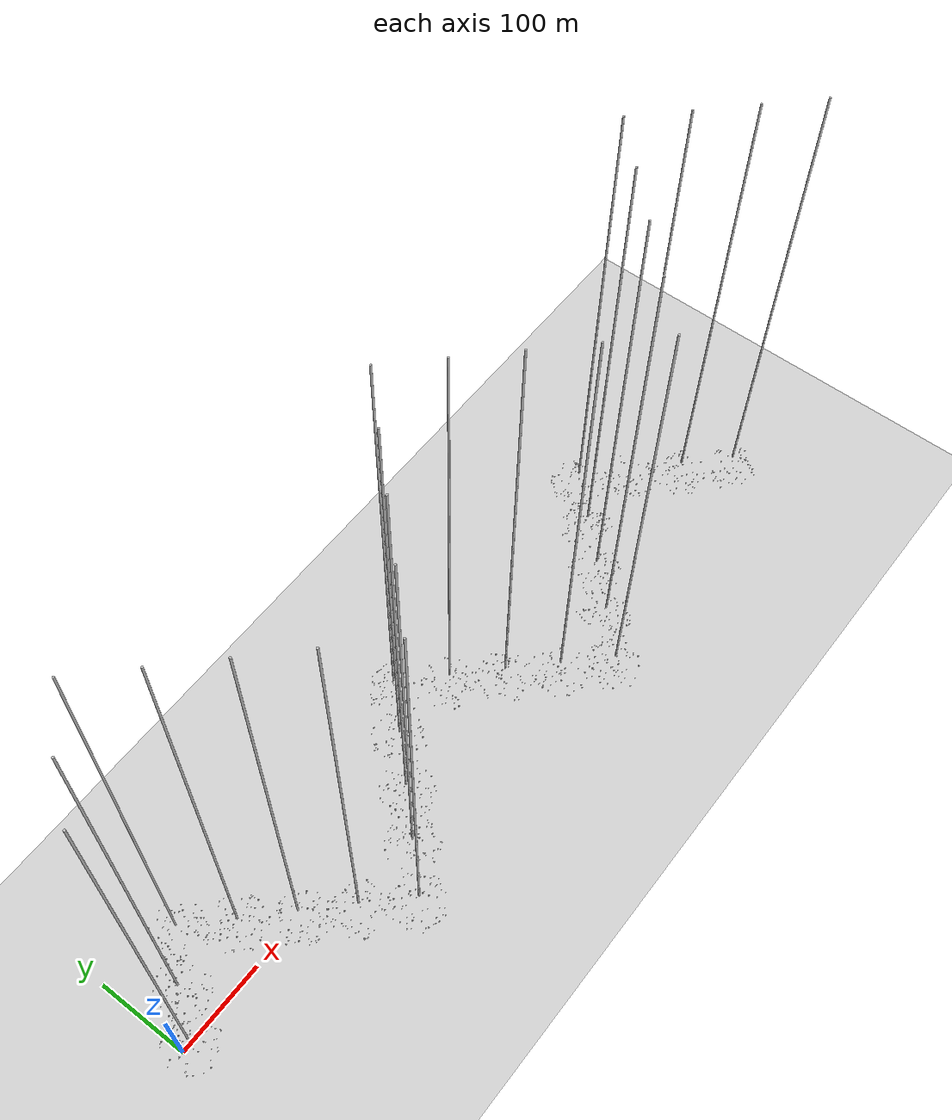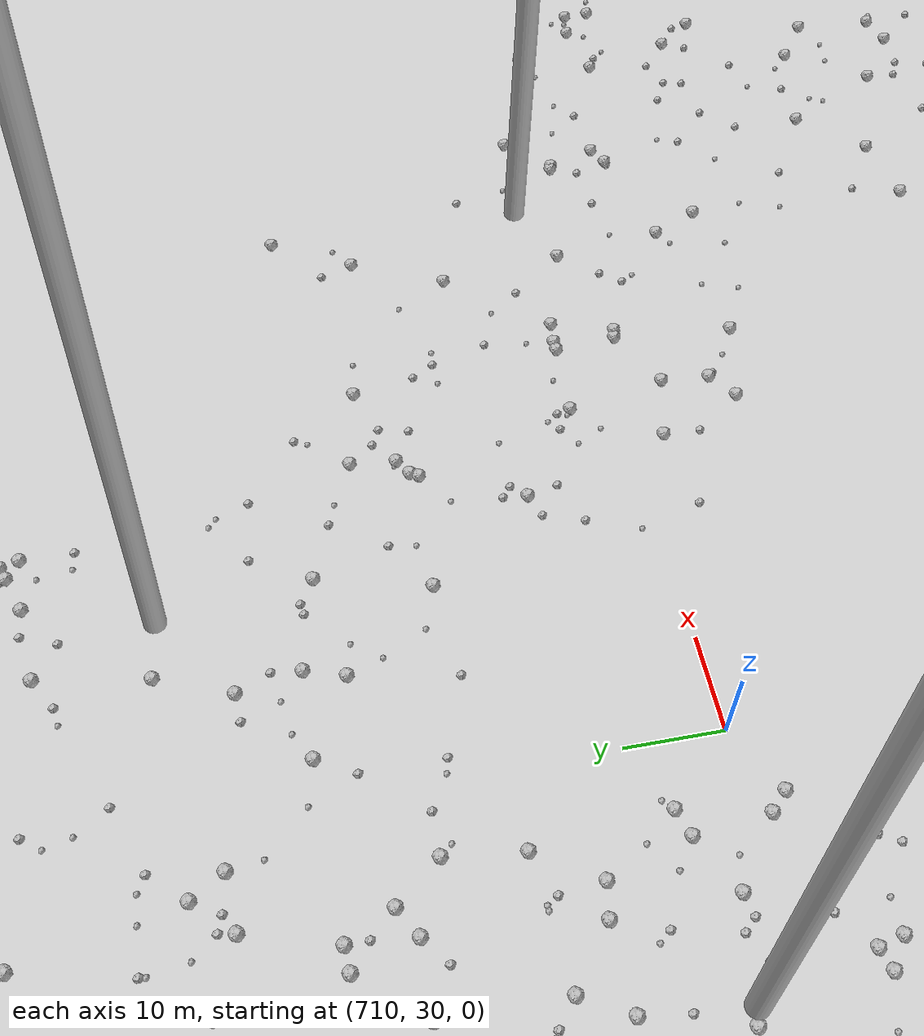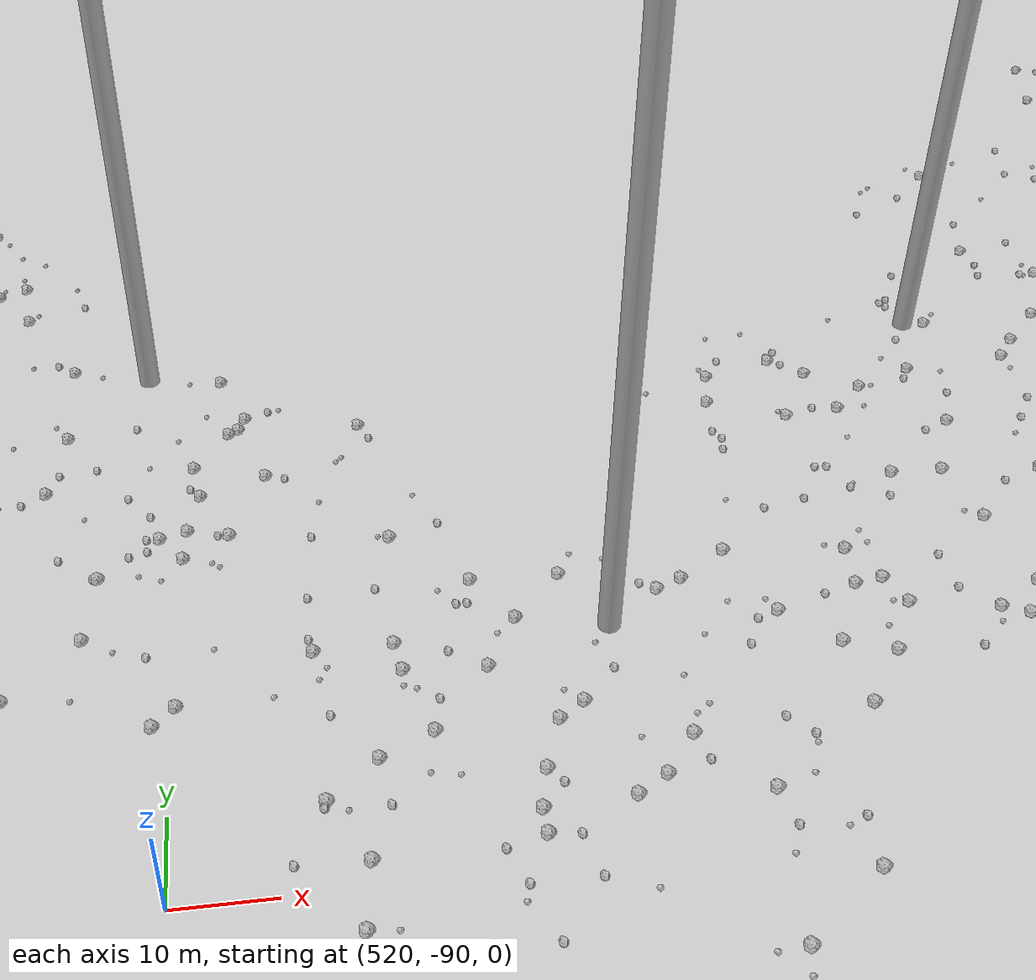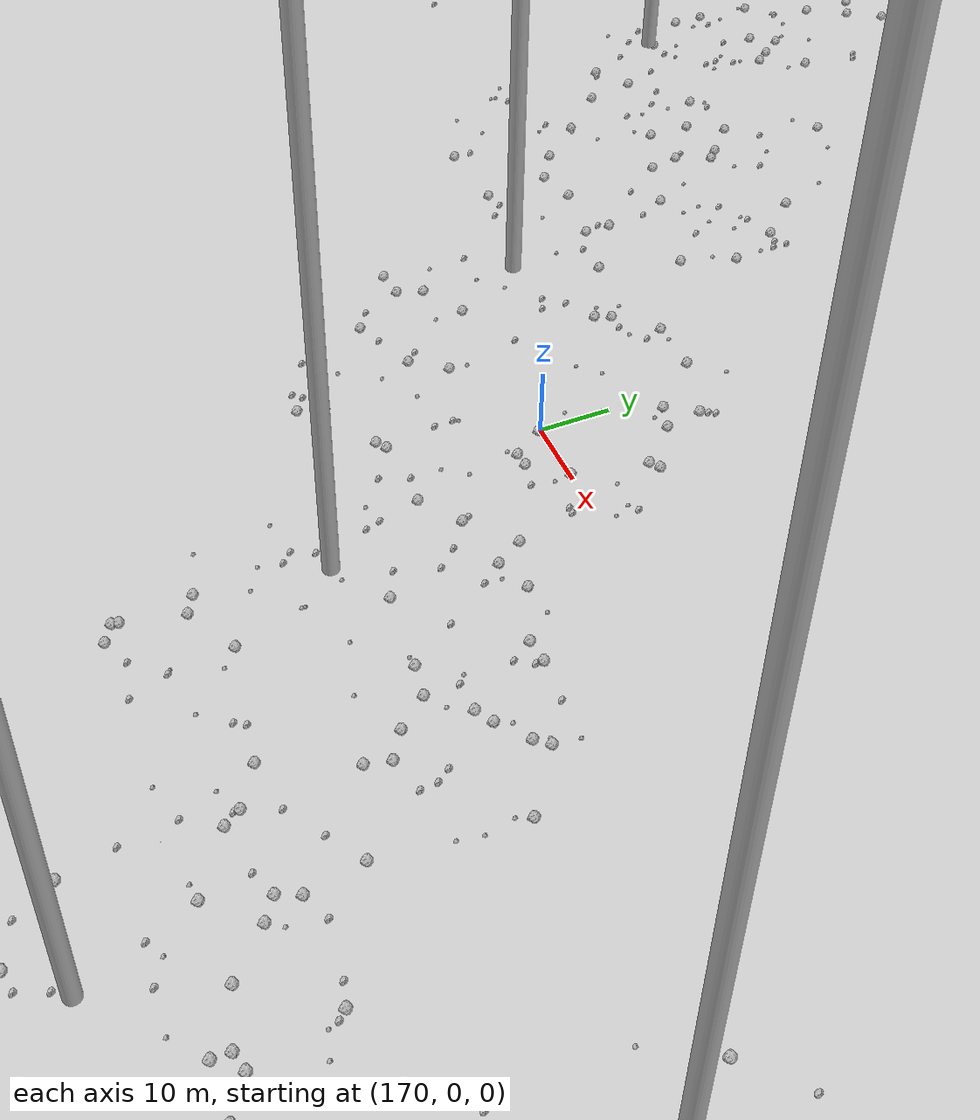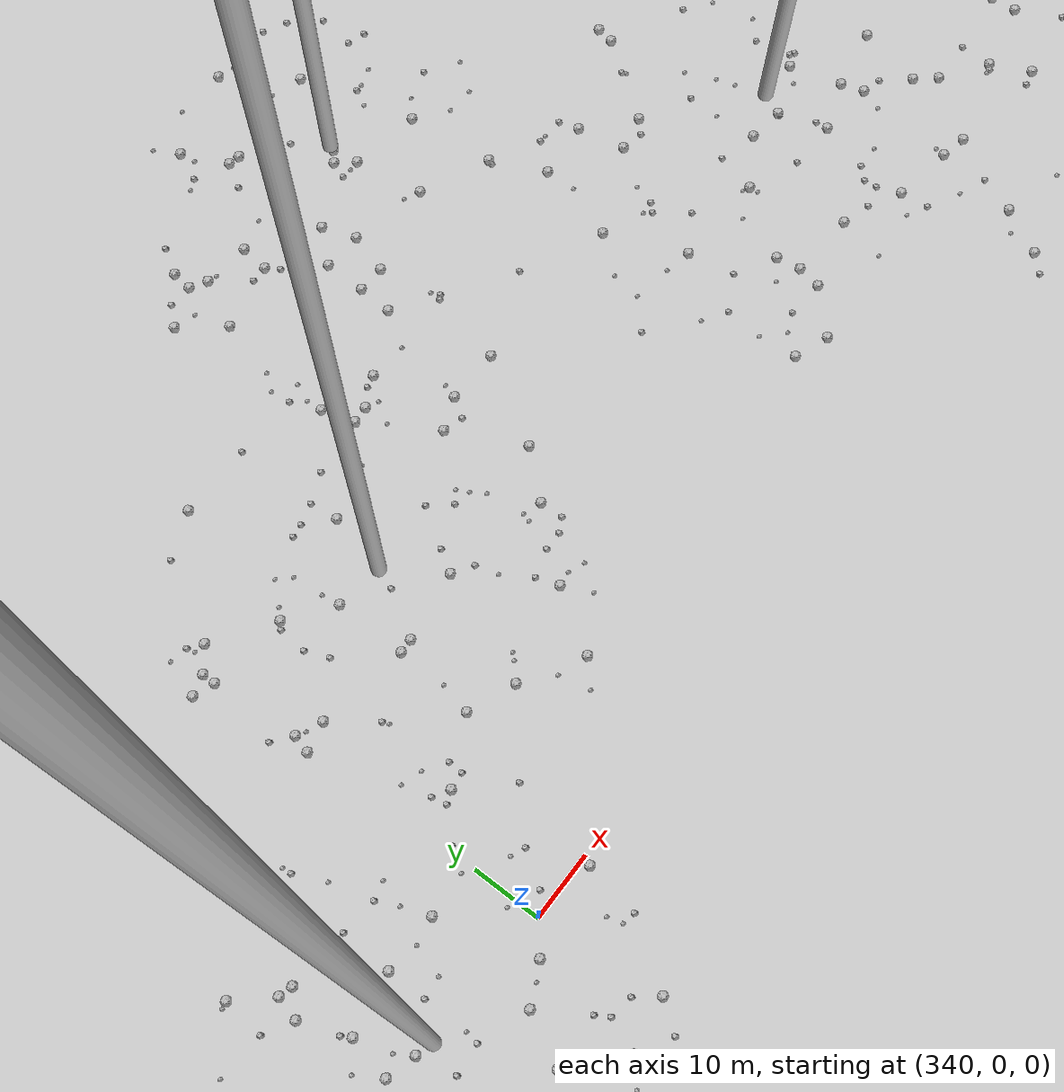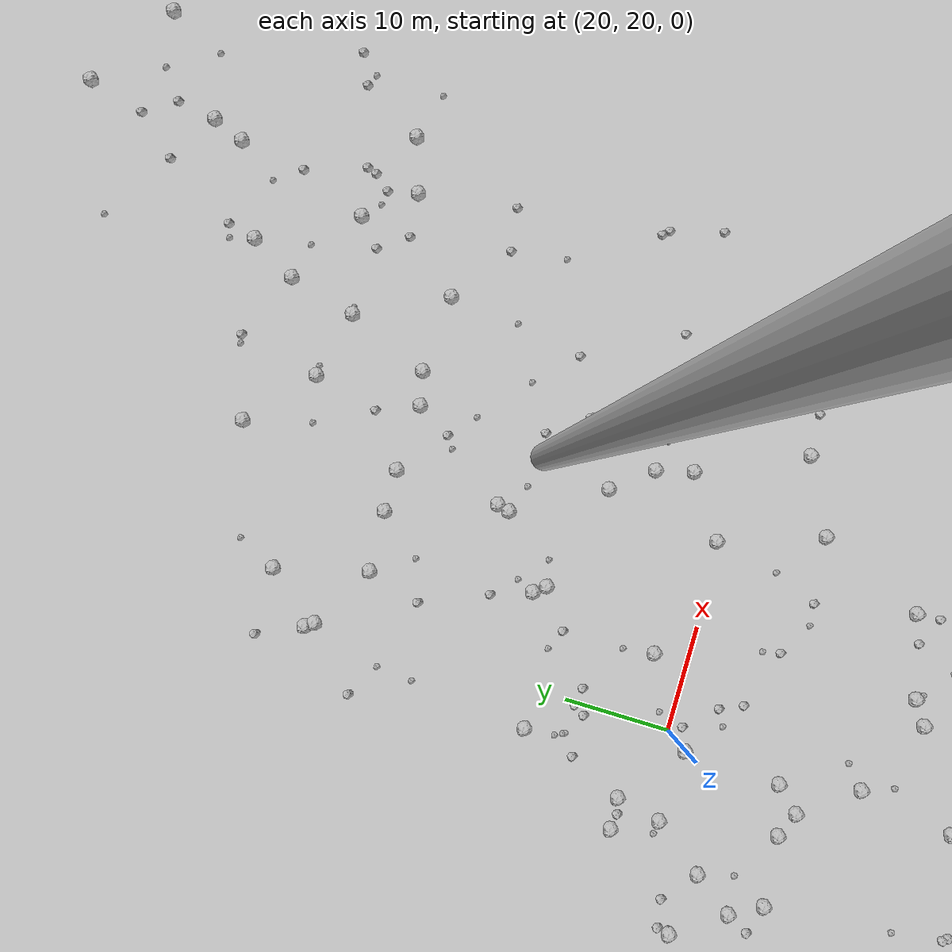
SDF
<sdf version="1.6">
 <world name="default">
  <include><uri>model://custom_ground</uri></include>
  <include><uri>model://sun</uri></include>
  <spherical_coordinates>
   <surface_model>EARTH_WGS84</surface_model>
   <latitude_deg>38.161479</latitude_deg>
   <longitude_deg>-122.454630</longitude_deg>
   <elevation>488.0</elevation>
   <heading_deg>90</heading_deg>
  </spherical_coordinates>
  <model name="rock1_0_0">
   <include><uri>model://rock1</uri><pose>18.752457497050067 18.109081399433165 0.5 0 0 0</pose></include>
  </model>
  <model name="rock1_0_1">
   <include><uri>model://rock1</uri><pose>5.660684782589623 10.244629294801733 0.5 0 0 0</pose></include>
  </model>
  <model name="rock1_0_2">
   <include><uri>model://rock1</uri><pose>27.346064810536994 -2.580714548875399 0.5 0 0 0</pose></include>
  </model>
  <model name="rock1_0_3">
   <include><uri>model://rock1</uri><pose>2.3995338080641773 14.98769402513446 0.5 0 0 0</pose></include>
  </model>
  <model name="rock1_0_4">
   <include><uri>model://rock1</uri><pose>12.884090526138614 22.919203178896517 0.5 0 0 0</pose></include>
  </model>
  <model name="rock1_0_5">
   <include><uri>model://rock1</uri><pose>13.81106825147453 7.762618812759619 0.5 0 0 0</pose></include>
  </model>
  <model name="rock1_0_6">
   <include><uri>model://rock1</uri><pose>-11.330809202531917 -13.27816265428374 0.5 0 0 0</pose></include>
  </model>
  <model name="rock1_0_7">
   <include><uri>model://rock1</uri><pose>9.968854779922502 22.771228361815666 0.5 0 0 0</pose></include>
  </model>
  <model name="rock1_0_8">
   <include><uri>model://rock1</uri><pose>34.00520805926403 -8.24698035894636 0.5 0 0 0</pose></include>
  </model>
  <model name="rock1_0_9">
   <include><uri>model://rock1</uri><pose>-4.808277266897855 0.12263634173859472 0.5 0 0 0</pose></include>
  </model>
  <model name="rock1_0_10">
   <include><uri>model://rock1</uri><pose>0.8573502836081275 9.760169233936807 0.5 0 0 0</pose></include>
  </model>
  <model name="rock1_0_11">
   <include><uri>model://rock1</uri><pose>29.517864844027166 -1.1846229876156897 0.5 0 0 0</pose></include>
  </model>
  <model name="rock1_0_12">
   <include><uri>model://rock1</uri><pose>26.597099732939967 23.33574086659278 0.5 0 0 0</pose></include>
  </model>
  <model name="rock1_0_13">
   <include><uri>model://rock1</uri><pose>7.295338230299226 7.289260338678858 0.5 0 0 0</pose></include>
  </model>
  <model name="rock1_0_14">
   <include><uri>model://rock1</uri><pose>-4.913092855298233 22.404779569685495 0.5 0 0 0</pose></include>
  </model>
  <model name="rock1_0_15">
   <include><uri>model://rock1</uri><pose>5.608404033991356 -28.363584563233513 0.5 0 0 0</pose></include>
  </model>
  <model name="rock1_0_16">
   <include><uri>model://rock1</uri><pose>8.319342677354072 13.935034523301056 0.5 0 0 0</pose></include>
  </model>
  <model name="rock1_0_17">
   <include><uri>model://rock1</uri><pose>20.686091982725728 -23.703162137072084 0.5 0 0 0</pose></include>
  </model>
  <model name="rock1_0_18">
   <include><uri>model://rock1</uri><pose>-12.214886643660236 5.344971832599178 0.5 0 0 0</pose></include>
  </model>
  <model name="rock1_0_19">
   <include><uri>model://rock1</uri><pose>16.20149260654884 6.696816177758812 0.5 0 0 0</pose></include>
  </model>
  <model name="rock1_0_20">
   <include><uri>model://rock1</uri><pose>18.49349003040458 -7.594753827377943 0.5 0 0 0</pose></include>
  </model>
  <model name="rock1_0_21">
   <include><uri>model://rock1</uri><pose>-13.02279681591087 -16.37380190348147 0.5 0 0 0</pose></include>
  </model>
  <model name="rock1_0_22">
   <include><uri>model://rock1</uri><pose>11.952118667838732 18.674037649331837 0.5 0 0 0</pose></include>
  </model>
  <model name="rock1_0_23">
   <include><uri>model://rock1</uri><pose>-1.6127313268092465 9.017278482259812 0.5 0 0 0</pose></include>
  </model>
  <model name="rock1_0_24">
   <include><uri>model://rock1</uri><pose>18.36680902269176 8.936638793772659 0.5 0 0 0</pose></include>
  </model>
  <model name="rock1_0_25">
   <include><uri>model://rock1</uri><pose>20.012152720916696 1.4763184421978082 0.5 0 0 0</pose></include>
  </model>
  <model name="rock1_0_26">
   <include><uri>model://rock1</uri><pose>37.164475944113995 0.8007525209864177 0.5 0 0 0</pose></include>
  </model>
  <model name="rock2_0_0">
   <include><uri>model://rock2</uri><pose>27.361978751840724 -24.13830649912704 0.3 0 0 0</pose></include>
  </model>
  <model name="rock2_0_1">
   <include><uri>model://rock2</uri><pose>-9.669564794837363 19.881833282372163 0.3 0 0 0</pose></include>
  </model>
  <model name="rock2_0_2">
   <include><uri>model://rock2</uri><pose>-9.464914220876818 -20.37741408829853 0.3 0 0 0</pose></include>
  </model>
  <model name="rock2_0_3">
   <include><uri>model://rock2</uri><pose>37.288879895963696 -1.589025571869719 0.3 0 0 0</pose></include>
  </model>
  <model name="rock2_0_4">
   <include><uri>model://rock2</uri><pose>-11.963257210416185 -12.594708360741276 0.3 0 0 0</pose></include>
  </model>
  <model name="rock2_0_5">
   <include><uri>model://rock2</uri><pose>-6.347653816981007 -0.3557144465479496 0.3 0 0 0</pose></include>
  </model>
  <model name="rock2_0_6">
   <include><uri>model://rock2</uri><pose>5.117076111496392 16.478688077986682 0.3 0 0 0</pose></include>
  </model>
  <model name="rock2_0_7">
   <include><uri>model://rock2</uri><pose>35.85498623393944 -11.619160606830807 0.3 0 0 0</pose></include>
  </model>
  <model name="rock2_0_8">
   <include><uri>model://rock2</uri><pose>34.52118239784182 -0.2530981746712655 0.3 0 0 0</pose></include>
  </model>
  <model name="rock2_0_9">
   <include><uri>model://rock2</uri><pose>8.969558555489453 -9.444920239821823 0.3 0 0 0</pose></include>
  </model>
  <model name="rock2_0_10">
   <include><uri>model://rock2</uri><pose>11.35086895625988 22.498695985281152 0.3 0 0 0</pose></include>
  </model>
  <model name="rock2_0_11">
   <include><uri>model://rock2</uri><pose>26.67539662545274 23.085591285811653 0.3 0 0 0</pose></include>
  </model>
  <model name="rock2_0_12">
   <include><uri>model://rock2</uri><pose>4.430867134289674 8.087061134515672 0.3 0 0 0</pose></include>
  </model>
  <model name="rock2_0_13">
   <include><uri>model://rock2</uri><pose>19.140681322352982 28.015542194080126 0.3 0 0 0</pose></include>
  </model>
  <model name="rock2_0_14">
   <include><uri>model://rock2</uri><pose>9.289516634810745 -9.872008037392078 0.3 0 0 0</pose></include>
  </model>
  <model name="rock2_0_15">
   <include><uri>model://rock2</uri><pose>17.590376584430466 -17.663156616335336 0.3 0 0 0</pose></include>
  </model>
  <model name="rock2_0_16">
   <include><uri>model://rock2</uri><pose>35.30416883056362 10.18421262710143 0.3 0 0 0</pose></include>
  </model>
  <model name="rock2_0_17">
   <include><uri>model://rock2</uri><pose>-17.965440066148158 2.72283823909261 0.3 0 0 0</pose></include>
  </model>
  <model name="rock2_0_18">
   <include><uri>model://rock2</uri><pose>19.583490845653095 -23.833705341714627 0.3 0 0 0</pose></include>
  </model>
  <model name="rock2_0_19">
   <include><uri>model://rock2</uri><pose>-4.467095472777556 -9.342167957844183 0.3 0 0 0</pose></include>
  </model>
  <model name="rock2_0_20">
   <include><uri>model://rock2</uri><pose>35.47211992447188 -13.239131136765529 0.3 0 0 0</pose></include>
  </model>
  <model name="rock2_0_21">
   <include><uri>model://rock2</uri><pose>15.21829623558105 27.972923388095552 0.3 0 0 0</pose></include>
  </model>
  <model name="rock2_0_22">
   <include><uri>model://rock2</uri><pose>24.301527148861368 13.916257540501938 0.3 0 0 0</pose></include>
  </model>
  <model name="rock2_0_23">
   <include><uri>model://rock2</uri><pose>19.061035414515793 -9.282955280752418 0.3 0 0 0</pose></include>
  </model>
  <model name="rock2_0_24">
   <include><uri>model://rock2</uri><pose>-1.9602860611707413 -26.53083071623595 0.3 0 0 0</pose></include>
  </model>
  <model name="rock2_0_25">
   <include><uri>model://rock2</uri><pose>2.548647129743806 16.077381119668402 0.3 0 0 0</pose></include>
  </model>
  <model name="rock2_0_26">
   <include><uri>model://rock2</uri><pose>-5.664273623775571 -8.268468224304865 0.3 0 0 0</pose></include>
  </model>
  <model name="rock3_0_0">
   <include><uri>model://rock3</uri><pose>-15.023169385542207 -5.538639418323978 0.2 0 0 0</pose></include>
  </model>
  <model name="rock3_0_1">
   <include><uri>model://rock3</uri><pose>-7.337988896797212 -21.638729481809918 0.2 0 0 0</pose></include>
  </model>
  <model name="rock3_0_2">
   <include><uri>model://rock3</uri><pose>6.718085761399944 -16.003510665200203 0.2 0 0 0</pose></include>
  </model>
  <model name="rock3_0_3">
   <include><uri>model://rock3</uri><pose>25.800977751355177 -13.566759244331735 0.2 0 0 0</pose></include>
  </model>
  <model name="rock3_0_4">
   <include><uri>model://rock3</uri><pose>21.43504605918848 21.276341532416133 0.2 0 0 0</pose></include>
  </model>
  <model name="rock3_0_5">
   <include><uri>model://rock3</uri><pose>-14.443491805244248 17.202758879709478 0.2 0 0 0</pose></include>
  </model>
  <model name="rock3_0_6">
   <include><uri>model://rock3</uri><pose>29.97108464417005 -1.9695593620044853 0.2 0 0 0</pose></include>
  </model>
  <model name="rock3_0_7">
   <include><uri>model://rock3</uri><pose>29.35004732208244 -7.942814222220399 0.2 0 0 0</pose></include>
  </model>
  <model name="rock3_0_8">
   <include><uri>model://rock3</uri><pose>15.816688946616239 -21.78765404298688 0.2 0 0 0</pose></include>
  </model>
  <model name="rock3_0_9">
   <include><uri>model://rock3</uri><pose>-10.700994102698171 3.6434669439555663 0.2 0 0 0</pose></include>
  </model>
  <model name="rock3_0_10">
   <include><uri>model://rock3</uri><pose>10.25559903679073 -23.962102729496188 0.2 0 0 0</pose></include>
  </model>
  <model name="rock3_0_11">
   <include><uri>model://rock3</uri><pose>33.19136505283924 9.936085264099944 0.2 0 0 0</pose></include>
  </model>
  <model name="rock3_0_12">
   <include><uri>model://rock3</uri><pose>27.721989486556325 -15.230702929780977 0.2 0 0 0</pose></include>
  </model>
  <model name="rock3_0_13">
   <include><uri>model://rock3</uri><pose>32.74247520333572 -4.245549499747231 0.2 0 0 0</pose></include>
  </model>
  <model name="rock3_0_14">
   <include><uri>model://rock3</uri><pose>21.84139035619077 15.211215523241407 0.2 0 0 0</pose></include>
  </model>
  <model name="rock3_0_15">
   <include><uri>model://rock3</uri><pose>20.96052888994241 -1.6815543095010028 0.2 0 0 0</pose></include>
  </model>
  <model name="rock3_0_16">
   <include><uri>model://rock3</uri><pose>9.044213799860692 10.469732677128903 0.2 0 0 0</pose></include>
  </model>
  <model name="rock3_0_17">
   <include><uri>model://rock3</uri><pose>8.25980524554329 -4.817950711159 0.2 0 0 0</pose></include>
  </model>
  <model name="rock3_0_18">
   <include><uri>model://rock3</uri><pose>21.9726176477753 3.0314288866031447 0.2 0 0 0</pose></include>
  </model>
  <model name="rock3_0_19">
   <include><uri>model://rock3</uri><pose>-12.665818089623706 -16.320993420710334 0.2 0 0 0</pose></include>
  </model>
  <model name="rock3_0_20">
   <include><uri>model://rock3</uri><pose>0.6929987077524906 -16.163020541564286 0.2 0 0 0</pose></include>
  </model>
  <model name="rock3_0_21">
   <include><uri>model://rock3</uri><pose>22.43270644658365 -21.042642050189613 0.2 0 0 0</pose></include>
  </model>
  <model name="rock3_0_22">
   <include><uri>model://rock3</uri><pose>10.574223678469728 18.713889228955217 0.2 0 0 0</pose></include>
  </model>
  <model name="rock3_0_23">
   <include><uri>model://rock3</uri><pose>-7.076877976792545 22.3542857980989 0.2 0 0 0</pose></include>
  </model>
  <model name="rock3_0_24">
   <include><uri>model://rock3</uri><pose>-5.1917717828290435 17.039963334272848 0.2 0 0 0</pose></include>
  </model>
  <model name="rock3_0_25">
   <include><uri>model://rock3</uri><pose>16.629112011265825 -10.026361068372104 0.2 0 0 0</pose></include>
  </model>
  <model name="rock3_0_26">
   <include><uri>model://rock3</uri><pose>-14.8215068086878 13.346344590363337 0.2 0 0 0</pose></include>
  </model>
  <model name="rock1_1_0">
   <include><uri>model://rock1</uri><pose>40.11318493557741 31.68015173194768 0.5 0 0 0</pose></include>
  </model>
  <model name="rock1_1_1">
   <include><uri>model://rock1</uri><pose>42.52115507974217 61.313445607647736 0.5 0 0 0</pose></include>
  </model>
  <model name="rock1_1_2">
   <include><uri>model://rock1</uri><pose>53.39783248224573 51.193662116276045 0.5 0 0 0</pose></include>
  </model>
  <model name="rock1_1_3">
   <include><uri>model://rock1</uri><pose>54.31344589657248 24.846484252374697 0.5 0 0 0</pose></include>
  </model>
  <model name="rock1_1_4">
   <include><uri>model://rock1</uri><pose>19.62852849369993 55.40703604736405 0.5 0 0 0</pose></include>
  </model>
  <model name="rock1_1_5">
   <include><uri>model://rock1</uri><pose>23.979541777136472 59.83346636330039 0.5 0 0 0</pose></include>
  </model>
  <model name="rock1_1_6">
   <include><uri>model://rock1</uri><pose>20.17131561718546 54.606962898468176 0.5 0 0 0</pose></include>
  </model>
  <model name="rock1_1_7">
   <include><uri>model://rock1</uri><pose>41.6402541171176 10.854027367615613 0.5 0 0 0</pose></include>
  </model>
  <model name="rock1_1_8">
   <include><uri>model://rock1</uri><pose>45.78863094882607 51.75635372680599 0.5 0 0 0</pose></include>
  </model>
  <model name="rock1_1_9">
   <include><uri>model://rock1</uri><pose>55.14039626875164 22.137933398272118 0.5 0 0 0</pose></include>
  </model>
  <model name="rock1_1_10">
   <include><uri>model://rock1</uri><pose>16.474438446253224 33.0042006446015 0.5 0 0 0</pose></include>
  </model>
  <model name="rock1_1_11">
   <include><uri>model://rock1</uri><pose>35.40876417053769 40.132919544450424 0.5 0 0 0</pose></include>
  </model>
  <model name="rock1_1_12">
   <include><uri>model://rock1</uri><pose>32.05490710427905 51.36788375640719 0.5 0 0 0</pose></include>
  </model>
  <model name="rock1_1_13">
   <include><uri>model://rock1</uri><pose>50.82366490497836 66.3385582530911 0.5 0 0 0</pose></include>
  </model>
  <model name="rock1_1_14">
   <include><uri>model://rock1</uri><pose>26.270341535812012 51.06632342042176 0.5 0 0 0</pose></include>
  </model>
  <model name="rock1_1_15">
   <include><uri>model://rock1</uri><pose>49.10896972747371 59.74766571244506 0.5 0 0 0</pose></include>
  </model>
  <model name="rock1_1_16">
   <include><uri>model://rock1</uri><pose>28.788282979884933 35.834725057090296 0.5 0 0 0</pose></include>
  </model>
  <model name="rock1_1_17">
   <include><uri>model://rock1</uri><pose>43.068036116297435 27.949042991831202 0.5 0 0 0</pose></include>
  </model>
  <model name="rock1_1_18">
   <include><uri>model://rock1</uri><pose>48.608407801211904 14.304012926254252 0.5 0 0 0</pose></include>
  </model>
  <model name="rock1_1_19">
   <include><uri>model://rock1</uri><pose>35.71779167914683 41.31843869354457 0.5 0 0 0</pose></include>
  </model>
  <model name="rock1_1_20">
   <include><uri>model://rock1</uri><pose>58.413620345038666 61.68011864902678 0.5 0 0 0</pose></include>
  </model>
  <model name="rock1_1_21">
   <include><uri>model://rock1</uri><pose>36.10647356742591 51.38355815126265 0.5 0 0 0</pose></include>
  </model>
  <model name="rock1_1_22">
   <include><uri>model://rock1</uri><pose>38.29599885938363 20.592711932183477 0.5 0 0 0</pose></include>
  </model>
  <model name="rock1_1_23">
   <include><uri>model://rock1</uri><pose>43.97669962768398 24.430426672392223 0.5 0 0 0</pose></include>
  </model>
  <model name="rock1_1_24">
   <include><uri>model://rock1</uri><pose>29.6638621499317 34.7270708740625 0.5 0 0 0</pose></include>
  </model>
  <model name="rock1_1_25">
   <include><uri>model://rock1</uri><pose>36.44097023780693 66.7273407665034 0.5 0 0 0</pose></include>
  </model>
  <model name="rock1_1_26">
   <include><uri>model://rock1</uri><pose>42.572776765559894 51.02274239444421 0.5 0 0 0</pose></include>
  </model>
  <model name="rock2_1_0">
   <include><uri>model://rock2</uri><pose>51.46899405763862 37.81112920859263 0.3 0 0 0</pose></include>
  </model>
  <model name="rock2_1_1">
   <include><uri>model://rock2</uri><pose>29.96636504986563 11.947550497280785 0.3 0 0 0</pose></include>
  </model>
  <model name="rock2_1_2">
   <include><uri>model://rock2</uri><pose>56.3616475347881 28.71801792752231 0.3 0 0 0</pose></include>
  </model>
  <model name="rock2_1_3">
   <include><uri>model://rock2</uri><pose>46.15149534054766 35.19650158327852 0.3 0 0 0</pose></include>
  </model>
  <model name="rock2_1_4">
   <include><uri>model://rock2</uri><pose>40.90961372288899 54.98650263293638 0.3 0 0 0</pose></include>
  </model>
  <model name="rock2_1_5">
   <include><uri>model://rock2</uri><pose>55.717038313111 22.075812359921933 0.3 0 0 0</pose></include>
  </model>
  <model name="rock2_1_6">
   <include><uri>model://rock2</uri><pose>17.537126172024003 59.68865466671766 0.3 0 0 0</pose></include>
  </model>
  <model name="rock2_1_7">
   <include><uri>model://rock2</uri><pose>64.96474549524177 33.55736553066377 0.3 0 0 0</pose></include>
  </model>
  <model name="rock2_1_8">
   <include><uri>model://rock2</uri><pose>66.8923320034742 27.895445012627796 0.3 0 0 0</pose></include>
  </model>
  <model name="rock2_1_9">
   <include><uri>model://rock2</uri><pose>19.807384225623178 29.064394704233635 0.3 0 0 0</pose></include>
  </model>
  <model name="rock2_1_10">
   <include><uri>model://rock2</uri><pose>52.64350746040808 14.42976622502275 0.3 0 0 0</pose></include>
  </model>
  <model name="rock2_1_11">
   <include><uri>model://rock2</uri><pose>44.20278678356924 69.34772279306523 0.3 0 0 0</pose></include>
  </model>
  <model name="rock2_1_12">
   <include><uri>model://rock2</uri><pose>55.82605067423931 59.432440884930344 0.3 0 0 0</pose></include>
  </model>
  <model name="rock2_1_13">
   <include><uri>model://rock2</uri><pose>63.46174111015216 47.60800327679036 0.3 0 0 0</pose></include>
  </model>
  <model name="rock2_1_14">
   <include><uri>model://rock2</uri><pose>40.60236233156188 47.72292782021399 0.3 0 0 0</pose></include>
  </model>
  <model name="rock2_1_15">
   <include><uri>model://rock2</uri><pose>27.38281032900373 39.593408606792764 0.3 0 0 0</pose></include>
  </model>
  <model name="rock2_1_16">
   <include><uri>model://rock2</uri><pose>14.680443941738355 49.66630745144027 0.3 0 0 0</pose></include>
  </model>
  <model name="rock2_1_17">
   <include><uri>model://rock2</uri><pose>20.768343076393254 18.88242923519794 0.3 0 0 0</pose></include>
  </model>
  <model name="rock2_1_18">
   <include><uri>model://rock2</uri><pose>21.519228538380503 28.79170705766226 0.3 0 0 0</pose></include>
  </model>
  <model name="rock2_1_19">
   <include><uri>model://rock2</uri><pose>59.26087166380454 46.991764827502536 0.3 0 0 0</pose></include>
  </model>
  <model name="rock2_1_20">
   <include><uri>model://rock2</uri><pose>46.1398707297842 27.539151208914543 0.3 0 0 0</pose></include>
  </model>
  <model name="rock2_1_21">
   <include><uri>model://rock2</uri><pose>57.817111659644794 56.68148189676099 0.3 0 0 0</pose></include>
  </model>
  <model name="rock2_1_22">
   <include><uri>model://rock2</uri><pose>65.50740515242654 32.95458913372185 0.3 0 0 0</pose></include>
  </model>
  <model name="rock2_1_23">
   <include><uri>model://rock2</uri><pose>43.47476694716056 38.86740037140071 0.3 0 0 0</pose></include>
  </model>
  <model name="rock2_1_24">
   <include><uri>model://rock2</uri><pose>24.710477693088478 45.900254245358546 0.3 0 0 0</pose></include>
  </model>
  <model name="rock2_1_25">
   <include><uri>model://rock2</uri><pose>23.344657893632423 16.071883003885695 0.3 0 0 0</pose></include>
  </model>
  <model name="rock2_1_26">
   <include><uri>model://rock2</uri><pose>26.077291129585586 32.07524216053112 0.3 0 0 0</pose></include>
  </model>
  <model name="rock3_1_0">
   <include><uri>model://rock3</uri><pose>29.58935958131609 13.528284076674343 0.2 0 0 0</pose></include>
  </model>
  <model name="rock3_1_1">
   <include><uri>model://rock3</uri><pose>28.573269608067818 47.22459404824167 0.2 0 0 0</pose></include>
  </model>
  <model name="rock3_1_2">
   <include><uri>model://rock3</uri><pose>49.72784729945336 59.826775977529465 0.2 0 0 0</pose></include>
  </model>
  <model name="rock3_1_3">
   <include><uri>model://rock3</uri><pose>24.080725690435564 32.903974394130614 0.2 0 0 0</pose></include>
  </model>
  <model name="rock3_1_4">
   <include><uri>model://rock3</uri><pose>32.056730032728126 35.16220679082792 0.2 0 0 0</pose></include>
  </model>
  <model name="rock3_1_5">
   <include><uri>model://rock3</uri><pose>38.044760557637815 60.33464323766091 0.2 0 0 0</pose></include>
  </model>
  <model name="rock3_1_6">
   <include><uri>model://rock3</uri><pose>59.58703395498331 19.24962320043619 0.2 0 0 0</pose></include>
  </model>
  <model name="rock3_1_7">
   <include><uri>model://rock3</uri><pose>16.584724940286733 30.068342020393974 0.2 0 0 0</pose></include>
  </model>
  <model name="rock3_1_8">
   <include><uri>model://rock3</uri><pose>39.460399052511654 46.93286049566411 0.2 0 0 0</pose></include>
  </model>
  <model name="rock3_1_9">
   <include><uri>model://rock3</uri><pose>43.01996040839426 45.51524061070211 0.2 0 0 0</pose></include>
  </model>
  <model name="rock3_1_10">
   <include><uri>model://rock3</uri><pose>16.948026105509502 29.357193458055043 0.2 0 0 0</pose></include>
  </model>
  <model name="rock3_1_11">
   <include><uri>model://rock3</uri><pose>38.08356160074612 39.05999932330626 0.2 0 0 0</pose></include>
  </model>
  <model name="rock3_1_12">
   <include><uri>model://rock3</uri><pose>47.71730858499671 41.44613414142164 0.2 0 0 0</pose></include>
  </model>
  <model name="rock3_1_13">
   <include><uri>model://rock3</uri><pose>17.857358964763236 47.813839499803294 0.2 0 0 0</pose></include>
  </model>
  <model name="rock3_1_14">
   <include><uri>model://rock3</uri><pose>25.69359034154715 63.64328639922098 0.2 0 0 0</pose></include>
  </model>
  <model name="rock3_1_15">
   <include><uri>model://rock3</uri><pose>52.72897042707459 44.3298814411589 0.2 0 0 0</pose></include>
  </model>
  <model name="rock3_1_16">
   <include><uri>model://rock3</uri><pose>43.41810975936283 61.34187199069813 0.2 0 0 0</pose></include>
  </model>
  <model name="rock3_1_17">
   <include><uri>model://rock3</uri><pose>37.04833651595713 14.292238997930106 0.2 0 0 0</pose></include>
  </model>
  <model name="rock3_1_18">
   <include><uri>model://rock3</uri><pose>60.035403540014634 41.59643760314003 0.2 0 0 0</pose></include>
  </model>
  <model name="rock3_1_19">
   <include><uri>model://rock3</uri><pose>17.54975040696035 44.3135100429987 0.2 0 0 0</pose></include>
  </model>
  <model name="rock3_1_20">
   <include><uri>model://rock3</uri><pose>17.0377067582114 29.169958185539887 0.2 0 0 0</pose></include>
  </model>
  <model name="rock3_1_21">
   <include><uri>model://rock3</uri><pose>43.33301117219944 69.17962457961954 0.2 0 0 0</pose></include>
  </model>
  <model name="rock3_1_22">
   <include><uri>model://rock3</uri><pose>20.24570509875321 54.287055017795595 0.2 0 0 0</pose></include>
  </model>
  <model name="rock3_1_23">
   <include><uri>model://rock3</uri><pose>26.120016516586727 26.16326228212192 0.2 0 0 0</pose></include>
  </model>
  <model name="rock3_1_24">
   <include><uri>model://rock3</uri><pose>29.449977618983322 37.444554774232444 0.2 0 0 0</pose></include>
  </model>
  <model name="rock3_1_25">
   <include><uri>model://rock3</uri><pose>53.583644013776954 14.198968028041662 0.2 0 0 0</pose></include>
  </model>
  <model name="rock3_1_26">
   <include><uri>model://rock3</uri><pose>56.649804405991574 16.683262567640448 0.2 0 0 0</pose></include>
  </model>
  <model name="rock1_2_0">
   <include><uri>model://rock1</uri><pose>93.25692808842302 56.415767174716976 0.5 0 0 0</pose></include>
  </model>
  <model name="rock1_2_1">
   <include><uri>model://rock1</uri><pose>104.16540272407354 70.31770437939878 0.5 0 0 0</pose></include>
  </model>
  <model name="rock1_2_2">
   <include><uri>model://rock1</uri><pose>72.44364470772459 84.98686347235589 0.5 0 0 0</pose></include>
  </model>
  <model name="rock1_2_3">
   <include><uri>model://rock1</uri><pose>64.78871984650004 103.97625543283465 0.5 0 0 0</pose></include>
  </model>
  <model name="rock1_2_4">
   <include><uri>model://rock1</uri><pose>97.29576728024745 91.05725153479396 0.5 0 0 0</pose></include>
  </model>
  <model name="rock1_2_5">
   <include><uri>model://rock1</uri><pose>102.45605711704613 72.46762620363653 0.5 0 0 0</pose></include>
  </model>
  <model name="rock1_2_6">
   <include><uri>model://rock1</uri><pose>90.70842114439061 95.26303713156581 0.5 0 0 0</pose></include>
  </model>
  <model name="rock1_2_7">
   <include><uri>model://rock1</uri><pose>67.29741642059138 58.85309361109006 0.5 0 0 0</pose></include>
  </model>
  <model name="rock1_2_8">
   <include><uri>model://rock1</uri><pose>75.9711860119179 103.72595341802173 0.5 0 0 0</pose></include>
  </model>
  <model name="rock1_2_9">
   <include><uri>model://rock1</uri><pose>82.80260788865402 72.1654969942898 0.5 0 0 0</pose></include>
  </model>
  <model name="rock1_2_10">
   <include><uri>model://rock1</uri><pose>88.5266515540063 67.63855635255283 0.5 0 0 0</pose></include>
  </model>
  <model name="rock1_2_11">
   <include><uri>model://rock1</uri><pose>107.81176951740515 76.81029182965867 0.5 0 0 0</pose></include>
  </model>
  <model name="rock1_2_12">
   <include><uri>model://rock1</uri><pose>100.0785718373835 75.6439397374786 0.5 0 0 0</pose></include>
  </model>
  <model name="rock1_2_13">
   <include><uri>model://rock1</uri><pose>63.42301450029192 77.9726026716059 0.5 0 0 0</pose></include>
  </model>
  <model name="rock1_2_14">
   <include><uri>model://rock1</uri><pose>74.22043621817971 88.75300896840102 0.5 0 0 0</pose></include>
  </model>
  <model name="rock1_2_15">
   <include><uri>model://rock1</uri><pose>93.82379579831746 85.24956176702042 0.5 0 0 0</pose></include>
  </model>
  <model name="rock1_2_16">
   <include><uri>model://rock1</uri><pose>94.15149967091675 92.82859050728088 0.5 0 0 0</pose></include>
  </model>
  <model name="rock1_2_17">
   <include><uri>model://rock1</uri><pose>63.680316178622434 90.58362860327703 0.5 0 0 0</pose></include>
  </model>
  <model name="rock1_2_18">
   <include><uri>model://rock1</uri><pose>88.50228089665369 62.95749340540327 0.5 0 0 0</pose></include>
  </model>
  <model name="rock1_2_19">
   <include><uri>model://rock1</uri><pose>53.40217145494115 70.83556382339034 0.5 0 0 0</pose></include>
  </model>
  <model name="rock1_2_20">
   <include><uri>model://rock1</uri><pose>100.38486668031037 95.97521901096246 0.5 0 0 0</pose></include>
  </model>
  <model name="rock1_2_21">
   <include><uri>model://rock1</uri><pose>62.15029432597779 74.85879996610133 0.5 0 0 0</pose></include>
  </model>
  <model name="rock1_2_22">
   <include><uri>model://rock1</uri><pose>91.26306565360335 56.1088860702274 0.5 0 0 0</pose></include>
  </model>
  <model name="rock1_2_23">
   <include><uri>model://rock1</uri><pose>62.065746458786634 57.12691879018324 0.5 0 0 0</pose></include>
  </model>
  <model name="rock1_2_24">
   <include><uri>model://rock1</uri><pose>89.20649667506717 99.89644666403719 0.5 0 0 0</pose></include>
  </model>
  <model name="rock1_2_25">
   <include><uri>model://rock1</uri><pose>97.68974945795298 72.05002090161622 0.5 0 0 0</pose></include>
  </model>
  <model name="rock1_2_26">
   <include><uri>model://rock1</uri><pose>89.11526197623942 75.94029399580464 0.5 0 0 0</pose></include>
  </model>
  <model name="rock2_2_0">
   <include><uri>model://rock2</uri><pose>83.06706665263954 98.026502728226 0.3 0 0 0</pose></include>
  </model>
  <model name="rock2_2_1">
   <include><uri>model://rock2</uri><pose>58.53289769483464 81.03616990738598 0.3 0 0 0</pose></include>
  </model>
  <model name="rock2_2_2">
   <include><uri>model://rock2</uri><pose>64.08431144632061 81.97574922865215 0.3 0 0 0</pose></include>
  </model>
  <model name="rock2_2_3">
   <include><uri>model://rock2</uri><pose>61.14956686470548 68.3856690761801 0.3 0 0 0</pose></include>
  </model>
  <model name="rock2_2_4">
   <include><uri>model://rock2</uri><pose>108.22932947122763 85.6419668691689 0.3 0 0 0</pose></include>
  </model>
  <model name="rock2_2_5">
   <include><uri>model://rock2</uri><pose>109.32585575246567 85.00141812040822 0.3 0 0 0</pose></include>
  </model>
  <model name="rock2_2_6">
   <include><uri>model://rock2</uri><pose>74.29160904045989 94.0592694067901 0.3 0 0 0</pose></include>
  </model>
  <model name="rock2_2_7">
   <include><uri>model://rock2</uri><pose>62.77627581446791 61.57701814108407 0.3 0 0 0</pose></include>
  </model>
  <model name="rock2_2_8">
   <include><uri>model://rock2</uri><pose>96.84330076256917 67.56506836293013 0.3 0 0 0</pose></include>
  </model>
  <model name="rock2_2_9">
   <include><uri>model://rock2</uri><pose>90.41186586654058 98.83914022441301 0.3 0 0 0</pose></include>
  </model>
  <model name="rock2_2_10">
   <include><uri>model://rock2</uri><pose>81.92696979095501 92.5686134625439 0.3 0 0 0</pose></include>
  </model>
  <model name="rock2_2_11">
   <include><uri>model://rock2</uri><pose>73.84206269556252 66.23714041015941 0.3 0 0 0</pose></include>
  </model>
  <model name="rock2_2_12">
   <include><uri>model://rock2</uri><pose>92.63445471932992 79.71802518389589 0.3 0 0 0</pose></include>
  </model>
  <model name="rock2_2_13">
   <include><uri>model://rock2</uri><pose>61.45221202245847 60.02805847868389 0.3 0 0 0</pose></include>
  </model>
  <model name="rock2_2_14">
   <include><uri>model://rock2</uri><pose>90.2254703838999 107.82900582347062 0.3 0 0 0</pose></include>
  </model>
  <model name="rock2_2_15">
   <include><uri>model://rock2</uri><pose>101.46936296249316 61.87676122934693 0.3 0 0 0</pose></include>
  </model>
  <model name="rock2_2_16">
   <include><uri>model://rock2</uri><pose>54.088853299739164 73.71945562054626 0.3 0 0 0</pose></include>
  </model>
  <model name="rock2_2_17">
   <include><uri>model://rock2</uri><pose>72.90889784655093 94.32422540494082 0.3 0 0 0</pose></include>
  </model>
  <model name="rock2_2_18">
   <include><uri>model://rock2</uri><pose>101.27200326278432 63.673743137852995 0.3 0 0 0</pose></include>
  </model>
  <model name="rock2_2_19">
   <include><uri>model://rock2</uri><pose>90.94996194012998 67.91176267961603 0.3 0 0 0</pose></include>
  </model>
  <model name="rock2_2_20">
   <include><uri>model://rock2</uri><pose>88.17187535562711 56.119362281560484 0.3 0 0 0</pose></include>
  </model>
  <model name="rock2_2_21">
   <include><uri>model://rock2</uri><pose>70.8510064290066 64.888927912271 0.3 0 0 0</pose></include>
  </model>
  <model name="rock2_2_22">
   <include><uri>model://rock2</uri><pose>63.115962027635646 62.54121614297313 0.3 0 0 0</pose></include>
  </model>
  <model name="rock2_2_23">
   <include><uri>model://rock2</uri><pose>62.07343662124031 85.06768273161597 0.3 0 0 0</pose></include>
  </model>
  <model name="rock2_2_24">
   <include><uri>model://rock2</uri><pose>90.53736649595757 53.14352588858667 0.3 0 0 0</pose></include>
  </model>
  <model name="rock2_2_25">
   <include><uri>model://rock2</uri><pose>102.71362921868896 66.25050374807824 0.3 0 0 0</pose></include>
  </model>
  <model name="rock2_2_26">
   <include><uri>model://rock2</uri><pose>75.5188468980261 88.6407905113829 0.3 0 0 0</pose></include>
  </model>
  <model name="rock3_2_0">
   <include><uri>model://rock3</uri><pose>60.042992969022855 60.213618908543474 0.2 0 0 0</pose></include>
  </model>
  <model name="rock3_2_1">
   <include><uri>model://rock3</uri><pose>79.60006133281578 96.82295508342675 0.2 0 0 0</pose></include>
  </model>
  <model name="rock3_2_2">
   <include><uri>model://rock3</uri><pose>87.23849094915849 50.90194068390726 0.2 0 0 0</pose></include>
  </model>
  <model name="rock3_2_3">
   <include><uri>model://rock3</uri><pose>97.40952439730901 58.2732584333863 0.2 0 0 0</pose></include>
  </model>
  <model name="rock3_2_4">
   <include><uri>model://rock3</uri><pose>98.72261699468336 77.59374761796522 0.2 0 0 0</pose></include>
  </model>
  <model name="rock3_2_5">
   <include><uri>model://rock3</uri><pose>83.06619572594406 108.34333896911704 0.2 0 0 0</pose></include>
  </model>
  <model name="rock3_2_6">
   <include><uri>model://rock3</uri><pose>95.43428757197732 79.75942924395042 0.2 0 0 0</pose></include>
  </model>
  <model name="rock3_2_7">
   <include><uri>model://rock3</uri><pose>81.80405505405214 78.21046866670508 0.2 0 0 0</pose></include>
  </model>
  <model name="rock3_2_8">
   <include><uri>model://rock3</uri><pose>101.48647474605514 81.2258219693429 0.2 0 0 0</pose></include>
  </model>
  <model name="rock3_2_9">
   <include><uri>model://rock3</uri><pose>66.96148444603955 84.14520595784926 0.2 0 0 0</pose></include>
  </model>
  <model name="rock3_2_10">
   <include><uri>model://rock3</uri><pose>76.0288529758872 93.93799261660561 0.2 0 0 0</pose></include>
  </model>
  <model name="rock3_2_11">
   <include><uri>model://rock3</uri><pose>107.36135628842953 73.94855006963131 0.2 0 0 0</pose></include>
  </model>
  <model name="rock3_2_12">
   <include><uri>model://rock3</uri><pose>54.35520799998487 65.54308205386266 0.2 0 0 0</pose></include>
  </model>
  <model name="rock3_2_13">
   <include><uri>model://rock3</uri><pose>71.95219674306 57.58616442314601 0.2 0 0 0</pose></include>
  </model>
  <model name="rock3_2_14">
   <include><uri>model://rock3</uri><pose>52.75517623058183 73.25191602142263 0.2 0 0 0</pose></include>
  </model>
  <model name="rock3_2_15">
   <include><uri>model://rock3</uri><pose>59.3210638925295 70.90516302194352 0.2 0 0 0</pose></include>
  </model>
  <model name="rock3_2_16">
   <include><uri>model://rock3</uri><pose>90.28068228460722 65.40372906688914 0.2 0 0 0</pose></include>
  </model>
  <model name="rock3_2_17">
   <include><uri>model://rock3</uri><pose>91.86591378545019 79.50190714505649 0.2 0 0 0</pose></include>
  </model>
  <model name="rock3_2_18">
   <include><uri>model://rock3</uri><pose>100.12458828457224 65.28257277637067 0.2 0 0 0</pose></include>
  </model>
  <model name="rock3_2_19">
   <include><uri>model://rock3</uri><pose>94.4346057962321 59.96201539860492 0.2 0 0 0</pose></include>
  </model>
  <model name="rock3_2_20">
   <include><uri>model://rock3</uri><pose>102.63579453131788 67.52199618012708 0.2 0 0 0</pose></include>
  </model>
  <model name="rock3_2_21">
   <include><uri>model://rock3</uri><pose>72.01151116012936 64.33903019949334 0.2 0 0 0</pose></include>
  </model>
  <model name="rock3_2_22">
   <include><uri>model://rock3</uri><pose>69.78222614658577 79.47324599361856 0.2 0 0 0</pose></include>
  </model>
  <model name="rock3_2_23">
   <include><uri>model://rock3</uri><pose>51.512093092807284 85.46382782157279 0.2 0 0 0</pose></include>
  </model>
  <model name="rock3_2_24">
   <include><uri>model://rock3</uri><pose>90.00374527054169 70.66245642889075 0.2 0 0 0</pose></include>
  </model>
  <model name="rock3_2_25">
   <include><uri>model://rock3</uri><pose>88.24612617184565 75.12109701867305 0.2 0 0 0</pose></include>
  </model>
  <model name="rock3_2_26">
   <include><uri>model://rock3</uri><pose>80.60494568090802 75.9823896426795 0.2 0 0 0</pose></include>
  </model>
  <model name="rock1_3_0">
   <include><uri>model://rock1</uri><pose>124.45667736453044 69.26628701670145 0.5 0 0 0</pose></include>
  </model>
  <model name="rock1_3_1">
   <include><uri>model://rock1</uri><pose>142.54122911400967 22.041255559528864 0.5 0 0 0</pose></include>
  </model>
  <model name="rock1_3_2">
   <include><uri>model://rock1</uri><pose>101.79953372946015 47.325497479094565 0.5 0 0 0</pose></include>
  </model>
  <model name="rock1_3_3">
   <include><uri>model://rock1</uri><pose>116.0115657851447 44.135593855227874 0.5 0 0 0</pose></include>
  </model>
  <model name="rock1_3_4">
   <include><uri>model://rock1</uri><pose>134.19746087054747 24.039770712784893 0.5 0 0 0</pose></include>
  </model>
  <model name="rock1_3_5">
   <include><uri>model://rock1</uri><pose>145.17425534183792 48.99663800455321 0.5 0 0 0</pose></include>
  </model>
  <model name="rock1_3_6">
   <include><uri>model://rock1</uri><pose>123.58666196059548 51.348254423504244 0.5 0 0 0</pose></include>
  </model>
  <model name="rock1_3_7">
   <include><uri>model://rock1</uri><pose>120.44063019420005 14.328221106793244 0.5 0 0 0</pose></include>
  </model>
  <model name="rock1_3_8">
   <include><uri>model://rock1</uri><pose>134.1674355900062 27.854106612358894 0.5 0 0 0</pose></include>
  </model>
  <model name="rock1_3_9">
   <include><uri>model://rock1</uri><pose>91.4503246525334 31.890577502848835 0.5 0 0 0</pose></include>
  </model>
  <model name="rock1_3_10">
   <include><uri>model://rock1</uri><pose>145.86556858782393 33.6490552763111 0.5 0 0 0</pose></include>
  </model>
  <model name="rock1_3_11">
   <include><uri>model://rock1</uri><pose>116.18600856842298 50.350067328884215 0.5 0 0 0</pose></include>
  </model>
  <model name="rock1_3_12">
   <include><uri>model://rock1</uri><pose>119.12159719703868 55.52381583129952 0.5 0 0 0</pose></include>
  </model>
  <model name="rock1_3_13">
   <include><uri>model://rock1</uri><pose>96.76928766310581 43.960417983832045 0.5 0 0 0</pose></include>
  </model>
  <model name="rock1_3_14">
   <include><uri>model://rock1</uri><pose>110.28775352134896 54.11118429620101 0.5 0 0 0</pose></include>
  </model>
  <model name="rock1_3_15">
   <include><uri>model://rock1</uri><pose>125.08221430031938 49.897670839548724 0.5 0 0 0</pose></include>
  </model>
  <model name="rock1_3_16">
   <include><uri>model://rock1</uri><pose>119.55622668688574 24.026970780512897 0.5 0 0 0</pose></include>
  </model>
  <model name="rock1_3_17">
   <include><uri>model://rock1</uri><pose>125.10728252618668 25.479552053351807 0.5 0 0 0</pose></include>
  </model>
  <model name="rock1_3_18">
   <include><uri>model://rock1</uri><pose>109.37799822852378 33.441250114309945 0.5 0 0 0</pose></include>
  </model>
  <model name="rock1_3_19">
   <include><uri>model://rock1</uri><pose>131.79722828744758 37.67582103942747 0.5 0 0 0</pose></include>
  </model>
  <model name="rock1_3_20">
   <include><uri>model://rock1</uri><pose>103.17303271004872 40.101001891063866 0.5 0 0 0</pose></include>
  </model>
  <model name="rock1_3_21">
   <include><uri>model://rock1</uri><pose>114.82525427059514 27.140134985394106 0.5 0 0 0</pose></include>
  </model>
  <model name="rock1_3_22">
   <include><uri>model://rock1</uri><pose>148.54519396297113 41.419176883883864 0.5 0 0 0</pose></include>
  </model>
  <model name="rock1_3_23">
   <include><uri>model://rock1</uri><pose>139.77909364455485 54.705313670421965 0.5 0 0 0</pose></include>
  </model>
  <model name="rock1_3_24">
   <include><uri>model://rock1</uri><pose>109.20346616835528 13.532975829071631 0.5 0 0 0</pose></include>
  </model>
  <model name="rock1_3_25">
   <include><uri>model://rock1</uri><pose>122.92446880320577 44.85488021271983 0.5 0 0 0</pose></include>
  </model>
  <model name="rock1_3_26">
   <include><uri>model://rock1</uri><pose>123.7918803373748 40.433386284758456 0.5 0 0 0</pose></include>
  </model>
  <model name="rock2_3_0">
   <include><uri>model://rock2</uri><pose>99.77423184596779 52.52937601614332 0.3 0 0 0</pose></include>
  </model>
  <model name="rock2_3_1">
   <include><uri>model://rock2</uri><pose>122.09818801602418 46.15884283171593 0.3 0 0 0</pose></include>
  </model>
  <model name="rock2_3_2">
   <include><uri>model://rock2</uri><pose>133.66521376772448 33.80313566448126 0.3 0 0 0</pose></include>
  </model>
  <model name="rock2_3_3">
   <include><uri>model://rock2</uri><pose>148.18095084936112 49.99098076531164 0.3 0 0 0</pose></include>
  </model>
  <model name="rock2_3_4">
   <include><uri>model://rock2</uri><pose>98.39342079407201 27.53650710966023 0.3 0 0 0</pose></include>
  </model>
  <model name="rock2_3_5">
   <include><uri>model://rock2</uri><pose>137.6273732769907 21.901920991687994 0.3 0 0 0</pose></include>
  </model>
  <model name="rock2_3_6">
   <include><uri>model://rock2</uri><pose>122.51685015606918 60.01127017836247 0.3 0 0 0</pose></include>
  </model>
  <model name="rock2_3_7">
   <include><uri>model://rock2</uri><pose>125.15883923981194 13.296912483010674 0.3 0 0 0</pose></include>
  </model>
  <model name="rock2_3_8">
   <include><uri>model://rock2</uri><pose>105.33975262398118 50.6856606885372 0.3 0 0 0</pose></include>
  </model>
  <model name="rock2_3_9">
   <include><uri>model://rock2</uri><pose>129.595898491998 56.0527757850495 0.3 0 0 0</pose></include>
  </model>
  <model name="rock2_3_10">
   <include><uri>model://rock2</uri><pose>146.98309120192243 48.65968467180966 0.3 0 0 0</pose></include>
  </model>
  <model name="rock2_3_11">
   <include><uri>model://rock2</uri><pose>108.23525026476162 48.31152155814861 0.3 0 0 0</pose></include>
  </model>
  <model name="rock2_3_12">
   <include><uri>model://rock2</uri><pose>140.7675085083964 38.965810568625784 0.3 0 0 0</pose></include>
  </model>
  <model name="rock2_3_13">
   <include><uri>model://rock2</uri><pose>127.81808113952687 34.728357666944646 0.3 0 0 0</pose></include>
  </model>
  <model name="rock2_3_14">
   <include><uri>model://rock2</uri><pose>148.10755824552 47.863095924045 0.3 0 0 0</pose></include>
  </model>
  <model name="rock2_3_15">
   <include><uri>model://rock2</uri><pose>97.44798091673043 28.85370158071335 0.3 0 0 0</pose></include>
  </model>
  <model name="rock2_3_16">
   <include><uri>model://rock2</uri><pose>140.7568062271081 47.60377754521674 0.3 0 0 0</pose></include>
  </model>
  <model name="rock2_3_17">
   <include><uri>model://rock2</uri><pose>96.04853663655666 56.98001602099064 0.3 0 0 0</pose></include>
  </model>
  <model name="rock2_3_18">
   <include><uri>model://rock2</uri><pose>112.43146736300025 56.054810107496586 0.3 0 0 0</pose></include>
  </model>
  <model name="rock2_3_19">
   <include><uri>model://rock2</uri><pose>94.00375773975782 49.80436755918545 0.3 0 0 0</pose></include>
  </model>
  <model name="rock2_3_20">
   <include><uri>model://rock2</uri><pose>136.3486418548024 45.18743175005664 0.3 0 0 0</pose></include>
  </model>
  <model name="rock2_3_21">
   <include><uri>model://rock2</uri><pose>133.34292538154753 26.400497734386846 0.3 0 0 0</pose></include>
  </model>
  <model name="rock2_3_22">
   <include><uri>model://rock2</uri><pose>109.05876902389211 16.268014762081314 0.3 0 0 0</pose></include>
  </model>
  <model name="rock2_3_23">
   <include><uri>model://rock2</uri><pose>106.77952082063146 30.264533999260824 0.3 0 0 0</pose></include>
  </model>
  <model name="rock2_3_24">
   <include><uri>model://rock2</uri><pose>97.66692929375765 43.786769177139114 0.3 0 0 0</pose></include>
  </model>
  <model name="rock2_3_25">
   <include><uri>model://rock2</uri><pose>123.05378071507437 15.04593007191255 0.3 0 0 0</pose></include>
  </model>
  <model name="rock2_3_26">
   <include><uri>model://rock2</uri><pose>109.68994123378589 43.18904043918262 0.3 0 0 0</pose></include>
  </model>
  <model name="rock3_3_0">
   <include><uri>model://rock3</uri><pose>136.86952262017525 62.19631095635424 0.2 0 0 0</pose></include>
  </model>
  <model name="rock3_3_1">
   <include><uri>model://rock3</uri><pose>113.27441375515481 36.19284693471346 0.2 0 0 0</pose></include>
  </model>
  <model name="rock3_3_2">
   <include><uri>model://rock3</uri><pose>109.96116068492532 33.353093868812095 0.2 0 0 0</pose></include>
  </model>
  <model name="rock3_3_3">
   <include><uri>model://rock3</uri><pose>96.5908047853226 25.29200064966006 0.2 0 0 0</pose></include>
  </model>
  <model name="rock3_3_4">
   <include><uri>model://rock3</uri><pose>96.66779195455254 26.08299996760111 0.2 0 0 0</pose></include>
  </model>
  <model name="rock3_3_5">
   <include><uri>model://rock3</uri><pose>113.76824351697763 42.37572653068583 0.2 0 0 0</pose></include>
  </model>
  <model name="rock3_3_6">
   <include><uri>model://rock3</uri><pose>104.69068618980188 20.217237832757302 0.2 0 0 0</pose></include>
  </model>
  <model name="rock3_3_7">
   <include><uri>model://rock3</uri><pose>129.0481954229873 43.05520140199795 0.2 0 0 0</pose></include>
  </model>
  <model name="rock3_3_8">
   <include><uri>model://rock3</uri><pose>138.83244895895695 42.16255580275447 0.2 0 0 0</pose></include>
  </model>
  <model name="rock3_3_9">
   <include><uri>model://rock3</uri><pose>120.71820011459036 66.96266438901137 0.2 0 0 0</pose></include>
  </model>
  <model name="rock3_3_10">
   <include><uri>model://rock3</uri><pose>139.7139169775309 47.00479504649911 0.2 0 0 0</pose></include>
  </model>
  <model name="rock3_3_11">
   <include><uri>model://rock3</uri><pose>128.07135222468318 52.39518907527751 0.2 0 0 0</pose></include>
  </model>
  <model name="rock3_3_12">
   <include><uri>model://rock3</uri><pose>146.43593422201008 38.632833815074484 0.2 0 0 0</pose></include>
  </model>
  <model name="rock3_3_13">
   <include><uri>model://rock3</uri><pose>134.9205808860999 42.45451868879302 0.2 0 0 0</pose></include>
  </model>
  <model name="rock3_3_14">
   <include><uri>model://rock3</uri><pose>110.09879179767529 50.25697007951836 0.2 0 0 0</pose></include>
  </model>
  <model name="rock3_3_15">
   <include><uri>model://rock3</uri><pose>109.95220794059894 45.7575693051979 0.2 0 0 0</pose></include>
  </model>
  <model name="rock3_3_16">
   <include><uri>model://rock3</uri><pose>135.42698229947763 39.65671798171901 0.2 0 0 0</pose></include>
  </model>
  <model name="rock3_3_17">
   <include><uri>model://rock3</uri><pose>126.58101059323246 58.911128501121595 0.2 0 0 0</pose></include>
  </model>
  <model name="rock3_3_18">
   <include><uri>model://rock3</uri><pose>147.96064239467995 45.815599929242424 0.2 0 0 0</pose></include>
  </model>
  <model name="rock3_3_19">
   <include><uri>model://rock3</uri><pose>102.96201102060793 62.54841667647177 0.2 0 0 0</pose></include>
  </model>
  <model name="rock3_3_20">
   <include><uri>model://rock3</uri><pose>110.96484131592852 56.39719904511087 0.2 0 0 0</pose></include>
  </model>
  <model name="rock3_3_21">
   <include><uri>model://rock3</uri><pose>99.95850300360308 17.936185862128617 0.2 0 0 0</pose></include>
  </model>
  <model name="rock3_3_22">
   <include><uri>model://rock3</uri><pose>94.3607091332142 27.82573229202422 0.2 0 0 0</pose></include>
  </model>
  <model name="rock3_3_23">
   <include><uri>model://rock3</uri><pose>128.2085198556156 19.70384519017679 0.2 0 0 0</pose></include>
  </model>
  <model name="rock3_3_24">
   <include><uri>model://rock3</uri><pose>129.39820054338824 68.24398580156381 0.2 0 0 0</pose></include>
  </model>
  <model name="rock3_3_25">
   <include><uri>model://rock3</uri><pose>107.86658679780956 28.62879639524983 0.2 0 0 0</pose></include>
  </model>
  <model name="rock3_3_26">
   <include><uri>model://rock3</uri><pose>141.74979881608732 44.811328273551226 0.2 0 0 0</pose></include>
  </model>
  <model name="rock1_4_0">
   <include><uri>model://rock1</uri><pose>173.35310310647182 -4.922726151215507 0.5 0 0 0</pose></include>
  </model>
  <model name="rock1_4_1">
   <include><uri>model://rock1</uri><pose>181.68942560109846 -16.38782256731361 0.5 0 0 0</pose></include>
  </model>
  <model name="rock1_4_2">
   <include><uri>model://rock1</uri><pose>154.25594796743076 -28.656645661068392 0.5 0 0 0</pose></include>
  </model>
  <model name="rock1_4_3">
   <include><uri>model://rock1</uri><pose>176.06150199017756 -20.1663658004977 0.5 0 0 0</pose></include>
  </model>
  <model name="rock1_4_4">
   <include><uri>model://rock1</uri><pose>179.46406515699448 -0.10514720756803797 0.5 0 0 0</pose></include>
  </model>
  <model name="rock1_4_5">
   <include><uri>model://rock1</uri><pose>141.61191929988246 -14.685527690537082 0.5 0 0 0</pose></include>
  </model>
  <model name="rock1_4_6">
   <include><uri>model://rock1</uri><pose>176.36896193284818 15.565196746767569 0.5 0 0 0</pose></include>
  </model>
  <model name="rock1_4_7">
   <include><uri>model://rock1</uri><pose>175.41985447676188 20.913440333264475 0.5 0 0 0</pose></include>
  </model>
  <model name="rock1_4_8">
   <include><uri>model://rock1</uri><pose>170.39598946888395 -0.5196165701646862 0.5 0 0 0</pose></include>
  </model>
  <model name="rock1_4_9">
   <include><uri>model://rock1</uri><pose>182.8578577703135 11.131637870797064 0.5 0 0 0</pose></include>
  </model>
  <model name="rock1_4_10">
   <include><uri>model://rock1</uri><pose>172.72918794636922 16.807951502774735 0.5 0 0 0</pose></include>
  </model>
  <model name="rock1_4_11">
   <include><uri>model://rock1</uri><pose>155.5054100196505 -25.15639283473437 0.5 0 0 0</pose></include>
  </model>
  <model name="rock1_4_12">
   <include><uri>model://rock1</uri><pose>181.498929084764 10.234696700134364 0.5 0 0 0</pose></include>
  </model>
  <model name="rock1_4_13">
   <include><uri>model://rock1</uri><pose>152.20699429220764 16.59238303293015 0.5 0 0 0</pose></include>
  </model>
  <model name="rock1_4_14">
   <include><uri>model://rock1</uri><pose>153.17004115725905 18.807211209438464 0.5 0 0 0</pose></include>
  </model>
  <model name="rock1_4_15">
   <include><uri>model://rock1</uri><pose>175.5060948183922 -4.783483720539131 0.5 0 0 0</pose></include>
  </model>
  <model name="rock1_4_16">
   <include><uri>model://rock1</uri><pose>132.2308156522525 -7.424111175123741 0.5 0 0 0</pose></include>
  </model>
  <model name="rock1_4_17">
   <include><uri>model://rock1</uri><pose>187.75077734414828 -11.20866643486535 0.5 0 0 0</pose></include>
  </model>
  <model name="rock1_4_18">
   <include><uri>model://rock1</uri><pose>166.07217866484388 23.92400480619692 0.5 0 0 0</pose></include>
  </model>
  <model name="rock1_4_19">
   <include><uri>model://rock1</uri><pose>154.2866944513238 -6.520388951076988 0.5 0 0 0</pose></include>
  </model>
  <model name="rock1_4_20">
   <include><uri>model://rock1</uri><pose>158.23651069176032 23.942815861402984 0.5 0 0 0</pose></include>
  </model>
  <model name="rock1_4_21">
   <include><uri>model://rock1</uri><pose>165.45131510847318 -20.22653280729836 0.5 0 0 0</pose></include>
  </model>
  <model name="rock1_4_22">
   <include><uri>model://rock1</uri><pose>137.52335910492243 -3.437643345174248 0.5 0 0 0</pose></include>
  </model>
  <model name="rock1_4_23">
   <include><uri>model://rock1</uri><pose>143.74177745667203 -0.016458025422767975 0.5 0 0 0</pose></include>
  </model>
  <model name="rock1_4_24">
   <include><uri>model://rock1</uri><pose>136.2246747011954 -7.013530225714874 0.5 0 0 0</pose></include>
  </model>
  <model name="rock1_4_25">
   <include><uri>model://rock1</uri><pose>150.77933090002907 -11.161324775351261 0.5 0 0 0</pose></include>
  </model>
  <model name="rock1_4_26">
   <include><uri>model://rock1</uri><pose>163.99000310630987 -21.145321626346536 0.5 0 0 0</pose></include>
  </model>
  <model name="rock2_4_0">
   <include><uri>model://rock2</uri><pose>159.20370919274563 21.371479309138174 0.3 0 0 0</pose></include>
  </model>
  <model name="rock2_4_1">
   <include><uri>model://rock2</uri><pose>179.06456390643362 -5.56747492339176 0.3 0 0 0</pose></include>
  </model>
  <model name="rock2_4_2">
   <include><uri>model://rock2</uri><pose>152.21384170820235 4.301310366104538 0.3 0 0 0</pose></include>
  </model>
  <model name="rock2_4_3">
   <include><uri>model://rock2</uri><pose>172.87703668288506 16.82922251942032 0.3 0 0 0</pose></include>
  </model>
  <model name="rock2_4_4">
   <include><uri>model://rock2</uri><pose>155.46617517973505 18.892378767254023 0.3 0 0 0</pose></include>
  </model>
  <model name="rock2_4_5">
   <include><uri>model://rock2</uri><pose>181.11992888676477 -15.285004479302557 0.3 0 0 0</pose></include>
  </model>
  <model name="rock2_4_6">
   <include><uri>model://rock2</uri><pose>144.93356278010236 -13.200609213595268 0.3 0 0 0</pose></include>
  </model>
  <model name="rock2_4_7">
   <include><uri>model://rock2</uri><pose>148.81538152156747 -24.112564333981048 0.3 0 0 0</pose></include>
  </model>
  <model name="rock2_4_8">
   <include><uri>model://rock2</uri><pose>176.3979210649394 22.920379991665683 0.3 0 0 0</pose></include>
  </model>
  <model name="rock2_4_9">
   <include><uri>model://rock2</uri><pose>171.7923122318668 -19.3732868962789 0.3 0 0 0</pose></include>
  </model>
  <model name="rock2_4_10">
   <include><uri>model://rock2</uri><pose>151.7839838860409 -26.943293868973125 0.3 0 0 0</pose></include>
  </model>
  <model name="rock2_4_11">
   <include><uri>model://rock2</uri><pose>147.57227861710479 10.69609201827177 0.3 0 0 0</pose></include>
  </model>
  <model name="rock2_4_12">
   <include><uri>model://rock2</uri><pose>175.89791806620582 22.04536764506971 0.3 0 0 0</pose></include>
  </model>
  <model name="rock2_4_13">
   <include><uri>model://rock2</uri><pose>147.7641062299789 14.289396298082153 0.3 0 0 0</pose></include>
  </model>
  <model name="rock2_4_14">
   <include><uri>model://rock2</uri><pose>149.1304277641972 -9.50937358279408 0.3 0 0 0</pose></include>
  </model>
  <model name="rock2_4_15">
   <include><uri>model://rock2</uri><pose>164.01524578924196 -12.764837673607264 0.3 0 0 0</pose></include>
  </model>
  <model name="rock2_4_16">
   <include><uri>model://rock2</uri><pose>163.89791302018756 -10.077163251911198 0.3 0 0 0</pose></include>
  </model>
  <model name="rock2_4_17">
   <include><uri>model://rock2</uri><pose>184.72135648501535 -2.8132385235184465 0.3 0 0 0</pose></include>
  </model>
  <model name="rock2_4_18">
   <include><uri>model://rock2</uri><pose>188.4966851690219 5.188964632898305 0.3 0 0 0</pose></include>
  </model>
  <model name="rock2_4_19">
   <include><uri>model://rock2</uri><pose>170.28956117270212 -23.29280505149668 0.3 0 0 0</pose></include>
  </model>
  <model name="rock2_4_20">
   <include><uri>model://rock2</uri><pose>145.5352163322026 11.575547838332305 0.3 0 0 0</pose></include>
  </model>
  <model name="rock2_4_21">
   <include><uri>model://rock2</uri><pose>132.727838996969 5.017924481033958 0.3 0 0 0</pose></include>
  </model>
  <model name="rock2_4_22">
   <include><uri>model://rock2</uri><pose>150.75440786951424 -28.09761746518128 0.3 0 0 0</pose></include>
  </model>
  <model name="rock2_4_23">
   <include><uri>model://rock2</uri><pose>145.2441693873549 -24.72470979626022 0.3 0 0 0</pose></include>
  </model>
  <model name="rock2_4_24">
   <include><uri>model://rock2</uri><pose>138.57549370060576 -12.67505993463639 0.3 0 0 0</pose></include>
  </model>
  <model name="rock2_4_25">
   <include><uri>model://rock2</uri><pose>185.7108517027588 -2.847126454609608 0.3 0 0 0</pose></include>
  </model>
  <model name="rock2_4_26">
   <include><uri>model://rock2</uri><pose>170.23163821416856 8.991786444899965 0.3 0 0 0</pose></include>
  </model>
  <model name="rock3_4_0">
   <include><uri>model://rock3</uri><pose>173.99869091283662 -12.037645805753193 0.2 0 0 0</pose></include>
  </model>
  <model name="rock3_4_1">
   <include><uri>model://rock3</uri><pose>168.2379354043658 4.316303806516665 0.2 0 0 0</pose></include>
  </model>
  <model name="rock3_4_2">
   <include><uri>model://rock3</uri><pose>157.238203739614 19.58189935983261 0.2 0 0 0</pose></include>
  </model>
  <model name="rock3_4_3">
   <include><uri>model://rock3</uri><pose>151.1112857279696 20.966264500372766 0.2 0 0 0</pose></include>
  </model>
  <model name="rock3_4_4">
   <include><uri>model://rock3</uri><pose>160.3224116011244 24.194790479196165 0.2 0 0 0</pose></include>
  </model>
  <model name="rock3_4_5">
   <include><uri>model://rock3</uri><pose>132.83378964621085 -0.4881954814955307 0.2 0 0 0</pose></include>
  </model>
  <model name="rock3_4_6">
   <include><uri>model://rock3</uri><pose>164.1859078313925 -29.47832099749301 0.2 0 0 0</pose></include>
  </model>
  <model name="rock3_4_7">
   <include><uri>model://rock3</uri><pose>173.8318595575823 14.985874839772137 0.2 0 0 0</pose></include>
  </model>
  <model name="rock3_4_8">
   <include><uri>model://rock3</uri><pose>172.07817460789934 -5.798138451072148 0.2 0 0 0</pose></include>
  </model>
  <model name="rock3_4_9">
   <include><uri>model://rock3</uri><pose>137.76945585121845 4.795599891145535 0.2 0 0 0</pose></include>
  </model>
  <model name="rock3_4_10">
   <include><uri>model://rock3</uri><pose>143.63026070409293 -4.037376892779601 0.2 0 0 0</pose></include>
  </model>
  <model name="rock3_4_11">
   <include><uri>model://rock3</uri><pose>136.69469878747748 17.987789542496053 0.2 0 0 0</pose></include>
  </model>
  <model name="rock3_4_12">
   <include><uri>model://rock3</uri><pose>160.38182290565587 9.816082638782099 0.2 0 0 0</pose></include>
  </model>
  <model name="rock3_4_13">
   <include><uri>model://rock3</uri><pose>148.9297825620478 -20.84790336650956 0.2 0 0 0</pose></include>
  </model>
  <model name="rock3_4_14">
   <include><uri>model://rock3</uri><pose>183.0890708186871 4.824698843075737 0.2 0 0 0</pose></include>
  </model>
  <model name="rock3_4_15">
   <include><uri>model://rock3</uri><pose>169.4674034692818 28.300215026750763 0.2 0 0 0</pose></include>
  </model>
  <model name="rock3_4_16">
   <include><uri>model://rock3</uri><pose>140.9746100472839 7.819241874393313 0.2 0 0 0</pose></include>
  </model>
  <model name="rock3_4_17">
   <include><uri>model://rock3</uri><pose>187.1000445647262 4.345783729268419 0.2 0 0 0</pose></include>
  </model>
  <model name="rock3_4_18">
   <include><uri>model://rock3</uri><pose>188.1966148990295 2.0915057704676627 0.2 0 0 0</pose></include>
  </model>
  <model name="rock3_4_19">
   <include><uri>model://rock3</uri><pose>179.5302986985019 -2.4145766961137305 0.2 0 0 0</pose></include>
  </model>
  <model name="rock3_4_20">
   <include><uri>model://rock3</uri><pose>152.29077802783095 -15.662176602687774 0.2 0 0 0</pose></include>
  </model>
  <model name="rock3_4_21">
   <include><uri>model://rock3</uri><pose>154.2331097766513 -3.8349149205877566 0.2 0 0 0</pose></include>
  </model>
  <model name="rock3_4_22">
   <include><uri>model://rock3</uri><pose>171.71618237259258 -15.103148555522026 0.2 0 0 0</pose></include>
  </model>
  <model name="rock3_4_23">
   <include><uri>model://rock3</uri><pose>157.44944709445633 -12.578230350230424 0.2 0 0 0</pose></include>
  </model>
  <model name="rock3_4_24">
   <include><uri>model://rock3</uri><pose>163.03398904325542 12.476805856476517 0.2 0 0 0</pose></include>
  </model>
  <model name="rock3_4_25">
   <include><uri>model://rock3</uri><pose>150.2004788958266 17.900443979867667 0.2 0 0 0</pose></include>
  </model>
  <model name="rock3_4_26">
   <include><uri>model://rock3</uri><pose>164.05777721914495 -9.352567836676549 0.2 0 0 0</pose></include>
  </model>
  <model name="rock1_5_0">
   <include><uri>model://rock1</uri><pose>207.2905431396755 -52.96062604427355 0.5 0 0 0</pose></include>
  </model>
  <model name="rock1_5_1">
   <include><uri>model://rock1</uri><pose>172.3794498498014 -31.126065789829212 0.5 0 0 0</pose></include>
  </model>
  <model name="rock1_5_2">
   <include><uri>model://rock1</uri><pose>213.10247563355597 -38.44236838591125 0.5 0 0 0</pose></include>
  </model>
  <model name="rock1_5_3">
   <include><uri>model://rock1</uri><pose>183.46646510014912 -63.5870060136895 0.5 0 0 0</pose></include>
  </model>
  <model name="rock1_5_4">
   <include><uri>model://rock1</uri><pose>181.09319513322285 -61.14054340258769 0.5 0 0 0</pose></include>
  </model>
  <model name="rock1_5_5">
   <include><uri>model://rock1</uri><pose>210.11348654464467 -27.075997871938235 0.5 0 0 0</pose></include>
  </model>
  <model name="rock1_5_6">
   <include><uri>model://rock1</uri><pose>182.94502943596393 -53.059038890387086 0.5 0 0 0</pose></include>
  </model>
  <model name="rock1_5_7">
   <include><uri>model://rock1</uri><pose>180.26907600351484 -51.568957556610926 0.5 0 0 0</pose></include>
  </model>
  <model name="rock1_5_8">
   <include><uri>model://rock1</uri><pose>190.16593546877968 -49.47806502783514 0.5 0 0 0</pose></include>
  </model>
  <model name="rock1_5_9">
   <include><uri>model://rock1</uri><pose>180.90670025741576 -62.05205236710748 0.5 0 0 0</pose></include>
  </model>
  <model name="rock1_5_10">
   <include><uri>model://rock1</uri><pose>201.2366327048352 -30.89532190000056 0.5 0 0 0</pose></include>
  </model>
  <model name="rock1_5_11">
   <include><uri>model://rock1</uri><pose>214.1652747397126 -58.81356642596461 0.5 0 0 0</pose></include>
  </model>
  <model name="rock1_5_12">
   <include><uri>model://rock1</uri><pose>218.10509349555034 -20.960723735710175 0.5 0 0 0</pose></include>
  </model>
  <model name="rock1_5_13">
   <include><uri>model://rock1</uri><pose>216.59386886351706 -22.699443128861084 0.5 0 0 0</pose></include>
  </model>
  <model name="rock1_5_14">
   <include><uri>model://rock1</uri><pose>203.11784625383382 -16.846231366724332 0.5 0 0 0</pose></include>
  </model>
  <model name="rock1_5_15">
   <include><uri>model://rock1</uri><pose>212.3185049389288 -41.75675107061074 0.5 0 0 0</pose></include>
  </model>
  <model name="rock1_5_16">
   <include><uri>model://rock1</uri><pose>195.09577092327174 -13.43235817395123 0.5 0 0 0</pose></include>
  </model>
  <model name="rock1_5_17">
   <include><uri>model://rock1</uri><pose>205.80626891086166 -31.702756020997754 0.5 0 0 0</pose></include>
  </model>
  <model name="rock1_5_18">
   <include><uri>model://rock1</uri><pose>212.54880296365195 -25.77237282497987 0.5 0 0 0</pose></include>
  </model>
  <model name="rock1_5_19">
   <include><uri>model://rock1</uri><pose>212.6876916161517 -56.5026530442007 0.5 0 0 0</pose></include>
  </model>
  <model name="rock1_5_20">
   <include><uri>model://rock1</uri><pose>224.56845655807558 -56.70927806048097 0.5 0 0 0</pose></include>
  </model>
  <model name="rock1_5_21">
   <include><uri>model://rock1</uri><pose>206.53095259807358 -16.614036123538334 0.5 0 0 0</pose></include>
  </model>
  <model name="rock1_5_22">
   <include><uri>model://rock1</uri><pose>209.40035964259692 -35.95830102470336 0.5 0 0 0</pose></include>
  </model>
  <model name="rock1_5_23">
   <include><uri>model://rock1</uri><pose>226.42577441600613 -27.042027957605924 0.5 0 0 0</pose></include>
  </model>
  <model name="rock1_5_24">
   <include><uri>model://rock1</uri><pose>190.15981109818085 -29.600657675165486 0.5 0 0 0</pose></include>
  </model>
  <model name="rock1_5_25">
   <include><uri>model://rock1</uri><pose>224.48243914372821 -46.05424327511916 0.5 0 0 0</pose></include>
  </model>
  <model name="rock1_5_26">
   <include><uri>model://rock1</uri><pose>190.13702354485832 -15.101065136590442 0.5 0 0 0</pose></include>
  </model>
  <model name="rock2_5_0">
   <include><uri>model://rock2</uri><pose>205.75209489482882 -27.047400948956515 0.3 0 0 0</pose></include>
  </model>
  <model name="rock2_5_1">
   <include><uri>model://rock2</uri><pose>179.42202594023226 -35.25833663359411 0.3 0 0 0</pose></include>
  </model>
  <model name="rock2_5_2">
   <include><uri>model://rock2</uri><pose>186.04956937170212 -27.538171351123694 0.3 0 0 0</pose></include>
  </model>
  <model name="rock2_5_3">
   <include><uri>model://rock2</uri><pose>206.41726055509605 -17.539317910118335 0.3 0 0 0</pose></include>
  </model>
  <model name="rock2_5_4">
   <include><uri>model://rock2</uri><pose>200.78211239253338 -53.283222150897274 0.3 0 0 0</pose></include>
  </model>
  <model name="rock2_5_5">
   <include><uri>model://rock2</uri><pose>178.01462085208664 -38.169068289519856 0.3 0 0 0</pose></include>
  </model>
  <model name="rock2_5_6">
   <include><uri>model://rock2</uri><pose>212.6097370600861 -17.097745706849338 0.3 0 0 0</pose></include>
  </model>
  <model name="rock2_5_7">
   <include><uri>model://rock2</uri><pose>220.95766655296205 -57.8988515994495 0.3 0 0 0</pose></include>
  </model>
  <model name="rock2_5_8">
   <include><uri>model://rock2</uri><pose>211.21172119116744 -63.08748962546761 0.3 0 0 0</pose></include>
  </model>
  <model name="rock2_5_9">
   <include><uri>model://rock2</uri><pose>185.45638338587776 -19.211218899684923 0.3 0 0 0</pose></include>
  </model>
  <model name="rock2_5_10">
   <include><uri>model://rock2</uri><pose>205.01752253700442 -19.767022855094304 0.3 0 0 0</pose></include>
  </model>
  <model name="rock2_5_11">
   <include><uri>model://rock2</uri><pose>177.41202919418154 -25.92135488157728 0.3 0 0 0</pose></include>
  </model>
  <model name="rock2_5_12">
   <include><uri>model://rock2</uri><pose>212.61431676686783 -57.234979728968455 0.3 0 0 0</pose></include>
  </model>
  <model name="rock2_5_13">
   <include><uri>model://rock2</uri><pose>216.48400850148496 -33.02157207872878 0.3 0 0 0</pose></include>
  </model>
  <model name="rock2_5_14">
   <include><uri>model://rock2</uri><pose>187.89118053640806 -21.886236454055982 0.3 0 0 0</pose></include>
  </model>
  <model name="rock2_5_15">
   <include><uri>model://rock2</uri><pose>217.76995427288367 -34.83792072244158 0.3 0 0 0</pose></include>
  </model>
  <model name="rock2_5_16">
   <include><uri>model://rock2</uri><pose>201.63065499338504 -51.91112264849987 0.3 0 0 0</pose></include>
  </model>
  <model name="rock2_5_17">
   <include><uri>model://rock2</uri><pose>214.36943688550218 -52.093116836630585 0.3 0 0 0</pose></include>
  </model>
  <model name="rock2_5_18">
   <include><uri>model://rock2</uri><pose>219.50885405483749 -48.99084288539845 0.3 0 0 0</pose></include>
  </model>
  <model name="rock2_5_19">
   <include><uri>model://rock2</uri><pose>179.42796646088675 -39.58611670793881 0.3 0 0 0</pose></include>
  </model>
  <model name="rock2_5_20">
   <include><uri>model://rock2</uri><pose>217.97808608077702 -37.13747260891802 0.3 0 0 0</pose></include>
  </model>
  <model name="rock2_5_21">
   <include><uri>model://rock2</uri><pose>192.71416016613966 -63.30394812163802 0.3 0 0 0</pose></include>
  </model>
  <model name="rock2_5_22">
   <include><uri>model://rock2</uri><pose>196.79745120924082 -24.353179305263723 0.3 0 0 0</pose></include>
  </model>
  <model name="rock2_5_23">
   <include><uri>model://rock2</uri><pose>190.8734425560486 -58.068796926871535 0.3 0 0 0</pose></include>
  </model>
  <model name="rock2_5_24">
   <include><uri>model://rock2</uri><pose>187.27694605460212 -61.94852012847167 0.3 0 0 0</pose></include>
  </model>
  <model name="rock2_5_25">
   <include><uri>model://rock2</uri><pose>192.327551322146 -17.974166679301348 0.3 0 0 0</pose></include>
  </model>
  <model name="rock2_5_26">
   <include><uri>model://rock2</uri><pose>178.11744376497813 -28.0224928013469 0.3 0 0 0</pose></include>
  </model>
  <model name="rock3_5_0">
   <include><uri>model://rock3</uri><pose>187.2203122990551 -39.54343763284676 0.2 0 0 0</pose></include>
  </model>
  <model name="rock3_5_1">
   <include><uri>model://rock3</uri><pose>173.48870053356893 -49.36505085205657 0.2 0 0 0</pose></include>
  </model>
  <model name="rock3_5_2">
   <include><uri>model://rock3</uri><pose>226.21610795498546 -32.89223727965907 0.2 0 0 0</pose></include>
  </model>
  <model name="rock3_5_3">
   <include><uri>model://rock3</uri><pose>205.7651624441497 -64.47934249230536 0.2 0 0 0</pose></include>
  </model>
  <model name="rock3_5_4">
   <include><uri>model://rock3</uri><pose>192.52668518918526 -51.623177484142346 0.2 0 0 0</pose></include>
  </model>
  <model name="rock3_5_5">
   <include><uri>model://rock3</uri><pose>197.78519927641534 -56.877392833610095 0.2 0 0 0</pose></include>
  </model>
  <model name="rock3_5_6">
   <include><uri>model://rock3</uri><pose>216.94450478213025 -20.60968772290795 0.2 0 0 0</pose></include>
  </model>
  <model name="rock3_5_7">
   <include><uri>model://rock3</uri><pose>205.88483219625098 -31.70841997413158 0.2 0 0 0</pose></include>
  </model>
  <model name="rock3_5_8">
   <include><uri>model://rock3</uri><pose>202.3683541750126 -39.03365763469743 0.2 0 0 0</pose></include>
  </model>
  <model name="rock3_5_9">
   <include><uri>model://rock3</uri><pose>184.7731853342736 -33.86072687755441 0.2 0 0 0</pose></include>
  </model>
  <model name="rock3_5_10">
   <include><uri>model://rock3</uri><pose>199.53487858922065 -12.850913665634529 0.2 0 0 0</pose></include>
  </model>
  <model name="rock3_5_11">
   <include><uri>model://rock3</uri><pose>192.3652442415236 -15.657879649315923 0.2 0 0 0</pose></include>
  </model>
  <model name="rock3_5_12">
   <include><uri>model://rock3</uri><pose>182.12483948420544 -44.78628049157583 0.2 0 0 0</pose></include>
  </model>
  <model name="rock3_5_13">
   <include><uri>model://rock3</uri><pose>178.70464211662895 -42.75291694904873 0.2 0 0 0</pose></include>
  </model>
  <model name="rock3_5_14">
   <include><uri>model://rock3</uri><pose>209.06543414872414 -58.08635802449622 0.2 0 0 0</pose></include>
  </model>
  <model name="rock3_5_15">
   <include><uri>model://rock3</uri><pose>204.4941340587701 -26.04911856628616 0.2 0 0 0</pose></include>
  </model>
  <model name="rock3_5_16">
   <include><uri>model://rock3</uri><pose>187.1526121346924 -39.967017211879046 0.2 0 0 0</pose></include>
  </model>
  <model name="rock3_5_17">
   <include><uri>model://rock3</uri><pose>190.22879085355603 -57.6350192409283 0.2 0 0 0</pose></include>
  </model>
  <model name="rock3_5_18">
   <include><uri>model://rock3</uri><pose>174.31607215661518 -26.651180291244238 0.2 0 0 0</pose></include>
  </model>
  <model name="rock3_5_19">
   <include><uri>model://rock3</uri><pose>199.55694909214026 -30.922158548797768 0.2 0 0 0</pose></include>
  </model>
  <model name="rock3_5_20">
   <include><uri>model://rock3</uri><pose>213.29472235855647 -23.659006757629655 0.2 0 0 0</pose></include>
  </model>
  <model name="rock3_5_21">
   <include><uri>model://rock3</uri><pose>208.19362619059655 -29.78366629002459 0.2 0 0 0</pose></include>
  </model>
  <model name="rock3_5_22">
   <include><uri>model://rock3</uri><pose>194.57096091760798 -36.575308850744 0.2 0 0 0</pose></include>
  </model>
  <model name="rock3_5_23">
   <include><uri>model://rock3</uri><pose>225.69446676782331 -36.08974624424127 0.2 0 0 0</pose></include>
  </model>
  <model name="rock3_5_24">
   <include><uri>model://rock3</uri><pose>225.44523818343876 -28.920292985043822 0.2 0 0 0</pose></include>
  </model>
  <model name="rock3_5_25">
   <include><uri>model://rock3</uri><pose>172.55830843139665 -38.93363760567032 0.2 0 0 0</pose></include>
  </model>
  <model name="rock3_5_26">
   <include><uri>model://rock3</uri><pose>218.34141410551257 -17.371210633737682 0.2 0 0 0</pose></include>
  </model>
  <model name="rock1_6_0">
   <include><uri>model://rock1</uri><pose>212.19094579385296 -87.07375463459219 0.5 0 0 0</pose></include>
  </model>
  <model name="rock1_6_1">
   <include><uri>model://rock1</uri><pose>222.13213429144622 -64.38743413603855 0.5 0 0 0</pose></include>
  </model>
  <model name="rock1_6_2">
   <include><uri>model://rock1</uri><pose>268.6375665955992 -74.88674773106808 0.5 0 0 0</pose></include>
  </model>
  <model name="rock1_6_3">
   <include><uri>model://rock1</uri><pose>240.22073401858734 -54.490352051175094 0.5 0 0 0</pose></include>
  </model>
  <model name="rock1_6_4">
   <include><uri>model://rock1</uri><pose>233.160341889054 -104.76365227887192 0.5 0 0 0</pose></include>
  </model>
  <model name="rock1_6_5">
   <include><uri>model://rock1</uri><pose>226.06611707689675 -102.1332790769346 0.5 0 0 0</pose></include>
  </model>
  <model name="rock1_6_6">
   <include><uri>model://rock1</uri><pose>237.9945177395511 -101.86548510773883 0.5 0 0 0</pose></include>
  </model>
  <model name="rock1_6_7">
   <include><uri>model://rock1</uri><pose>213.65300691378226 -77.76599558365405 0.5 0 0 0</pose></include>
  </model>
  <model name="rock1_6_8">
   <include><uri>model://rock1</uri><pose>262.8984082028868 -68.01198343104491 0.5 0 0 0</pose></include>
  </model>
  <model name="rock1_6_9">
   <include><uri>model://rock1</uri><pose>225.839286475773 -53.87840586365377 0.5 0 0 0</pose></include>
  </model>
  <model name="rock1_6_10">
   <include><uri>model://rock1</uri><pose>240.2649917494901 -69.02089707735249 0.5 0 0 0</pose></include>
  </model>
  <model name="rock1_6_11">
   <include><uri>model://rock1</uri><pose>254.22553538399086 -89.7971109928886 0.5 0 0 0</pose></include>
  </model>
  <model name="rock1_6_12">
   <include><uri>model://rock1</uri><pose>250.54947932506926 -82.94248023128699 0.5 0 0 0</pose></include>
  </model>
  <model name="rock1_6_13">
   <include><uri>model://rock1</uri><pose>259.83983921072576 -77.13364990874317 0.5 0 0 0</pose></include>
  </model>
  <model name="rock1_6_14">
   <include><uri>model://rock1</uri><pose>248.99114075358037 -76.69181872838631 0.5 0 0 0</pose></include>
  </model>
  <model name="rock1_6_15">
   <include><uri>model://rock1</uri><pose>242.85341642935333 -66.1159496020782 0.5 0 0 0</pose></include>
  </model>
  <model name="rock1_6_16">
   <include><uri>model://rock1</uri><pose>247.5674737876178 -69.35991895053726 0.5 0 0 0</pose></include>
  </model>
  <model name="rock1_6_17">
   <include><uri>model://rock1</uri><pose>236.69489415517157 -106.409219470478 0.5 0 0 0</pose></include>
  </model>
  <model name="rock1_6_18">
   <include><uri>model://rock1</uri><pose>245.31478924214773 -106.99583803968956 0.5 0 0 0</pose></include>
  </model>
  <model name="rock1_6_19">
   <include><uri>model://rock1</uri><pose>265.449969508579 -73.53600615132993 0.5 0 0 0</pose></include>
  </model>
  <model name="rock1_6_20">
   <include><uri>model://rock1</uri><pose>231.35607703263418 -103.74631647817465 0.5 0 0 0</pose></include>
  </model>
  <model name="rock1_6_21">
   <include><uri>model://rock1</uri><pose>226.93736229649375 -92.90198599762243 0.5 0 0 0</pose></include>
  </model>
  <model name="rock1_6_22">
   <include><uri>model://rock1</uri><pose>240.29680985384664 -66.66658326406373 0.5 0 0 0</pose></include>
  </model>
  <model name="rock1_6_23">
   <include><uri>model://rock1</uri><pose>233.04180696077415 -64.24567363204596 0.5 0 0 0</pose></include>
  </model>
  <model name="rock1_6_24">
   <include><uri>model://rock1</uri><pose>227.4802052937895 -58.779365001110115 0.5 0 0 0</pose></include>
  </model>
  <model name="rock1_6_25">
   <include><uri>model://rock1</uri><pose>224.24562100788867 -100.21405152152609 0.5 0 0 0</pose></include>
  </model>
  <model name="rock1_6_26">
   <include><uri>model://rock1</uri><pose>222.21197789150543 -85.70589433024347 0.5 0 0 0</pose></include>
  </model>
  <model name="rock2_6_0">
   <include><uri>model://rock2</uri><pose>250.0118660464093 -52.09763619964474 0.3 0 0 0</pose></include>
  </model>
  <model name="rock2_6_1">
   <include><uri>model://rock2</uri><pose>242.19480053137767 -74.6978145410369 0.3 0 0 0</pose></include>
  </model>
  <model name="rock2_6_2">
   <include><uri>model://rock2</uri><pose>225.0209981001601 -85.19320249503782 0.3 0 0 0</pose></include>
  </model>
  <model name="rock2_6_3">
   <include><uri>model://rock2</uri><pose>260.82912436906264 -63.62821821259835 0.3 0 0 0</pose></include>
  </model>
  <model name="rock2_6_4">
   <include><uri>model://rock2</uri><pose>260.62558475466926 -65.35319460737666 0.3 0 0 0</pose></include>
  </model>
  <model name="rock2_6_5">
   <include><uri>model://rock2</uri><pose>221.39391261664977 -79.95655744812537 0.3 0 0 0</pose></include>
  </model>
  <model name="rock2_6_6">
   <include><uri>model://rock2</uri><pose>216.59379356223772 -83.1692729135115 0.3 0 0 0</pose></include>
  </model>
  <model name="rock2_6_7">
   <include><uri>model://rock2</uri><pose>241.16231699355032 -55.55329792849559 0.3 0 0 0</pose></include>
  </model>
  <model name="rock2_6_8">
   <include><uri>model://rock2</uri><pose>254.14140288949275 -67.59204927424045 0.3 0 0 0</pose></include>
  </model>
  <model name="rock2_6_9">
   <include><uri>model://rock2</uri><pose>264.0669401664911 -82.31771699540313 0.3 0 0 0</pose></include>
  </model>
  <model name="rock2_6_10">
   <include><uri>model://rock2</uri><pose>262.2075630802212 -88.61579724868258 0.3 0 0 0</pose></include>
  </model>
  <model name="rock2_6_11">
   <include><uri>model://rock2</uri><pose>261.5604081444794 -76.99625041449451 0.3 0 0 0</pose></include>
  </model>
  <model name="rock2_6_12">
   <include><uri>model://rock2</uri><pose>247.07578865361995 -98.08822561515952 0.3 0 0 0</pose></include>
  </model>
  <model name="rock2_6_13">
   <include><uri>model://rock2</uri><pose>239.7405169228716 -89.92707801077694 0.3 0 0 0</pose></include>
  </model>
  <model name="rock2_6_14">
   <include><uri>model://rock2</uri><pose>262.7739047994992 -81.91001968795864 0.3 0 0 0</pose></include>
  </model>
  <model name="rock2_6_15">
   <include><uri>model://rock2</uri><pose>237.0485201139641 -53.51076273523544 0.3 0 0 0</pose></include>
  </model>
  <model name="rock2_6_16">
   <include><uri>model://rock2</uri><pose>229.51044890266448 -52.342701622408924 0.3 0 0 0</pose></include>
  </model>
  <model name="rock2_6_17">
   <include><uri>model://rock2</uri><pose>215.29655585011577 -90.0556088890794 0.3 0 0 0</pose></include>
  </model>
  <model name="rock2_6_18">
   <include><uri>model://rock2</uri><pose>218.9490933666574 -100.7362702512546 0.3 0 0 0</pose></include>
  </model>
  <model name="rock2_6_19">
   <include><uri>model://rock2</uri><pose>212.02596246953811 -70.4029154234711 0.3 0 0 0</pose></include>
  </model>
  <model name="rock2_6_20">
   <include><uri>model://rock2</uri><pose>230.16458119256254 -71.70321388627929 0.3 0 0 0</pose></include>
  </model>
  <model name="rock2_6_21">
   <include><uri>model://rock2</uri><pose>261.40407587181045 -82.21310733012258 0.3 0 0 0</pose></include>
  </model>
  <model name="rock2_6_22">
   <include><uri>model://rock2</uri><pose>226.46625359769422 -81.5412234135586 0.3 0 0 0</pose></include>
  </model>
  <model name="rock2_6_23">
   <include><uri>model://rock2</uri><pose>266.53228625005534 -84.24932816801956 0.3 0 0 0</pose></include>
  </model>
  <model name="rock2_6_24">
   <include><uri>model://rock2</uri><pose>244.22656000310215 -104.76431410853945 0.3 0 0 0</pose></include>
  </model>
  <model name="rock2_6_25">
   <include><uri>model://rock2</uri><pose>224.67484647965628 -70.9796914238906 0.3 0 0 0</pose></include>
  </model>
  <model name="rock2_6_26">
   <include><uri>model://rock2</uri><pose>235.0184090493388 -87.21628640919224 0.3 0 0 0</pose></include>
  </model>
  <model name="rock3_6_0">
   <include><uri>model://rock3</uri><pose>233.459483665424 -93.64493645288303 0.2 0 0 0</pose></include>
  </model>
  <model name="rock3_6_1">
   <include><uri>model://rock3</uri><pose>244.89151403707942 -58.009489718101705 0.2 0 0 0</pose></include>
  </model>
  <model name="rock3_6_2">
   <include><uri>model://rock3</uri><pose>266.4268235307446 -73.35603482620786 0.2 0 0 0</pose></include>
  </model>
  <model name="rock3_6_3">
   <include><uri>model://rock3</uri><pose>249.6869667347419 -71.96249027936769 0.2 0 0 0</pose></include>
  </model>
  <model name="rock3_6_4">
   <include><uri>model://rock3</uri><pose>234.7705379587188 -106.07327348412046 0.2 0 0 0</pose></include>
  </model>
  <model name="rock3_6_5">
   <include><uri>model://rock3</uri><pose>262.7913170986561 -93.51361748363368 0.2 0 0 0</pose></include>
  </model>
  <model name="rock3_6_6">
   <include><uri>model://rock3</uri><pose>269.61861305065514 -79.80394144038732 0.2 0 0 0</pose></include>
  </model>
  <model name="rock3_6_7">
   <include><uri>model://rock3</uri><pose>249.90440748110274 -71.50432598306764 0.2 0 0 0</pose></include>
  </model>
  <model name="rock3_6_8">
   <include><uri>model://rock3</uri><pose>264.2910965629599 -85.42169005361511 0.2 0 0 0</pose></include>
  </model>
  <model name="rock3_6_9">
   <include><uri>model://rock3</uri><pose>243.9802474530606 -89.13381792827238 0.2 0 0 0</pose></include>
  </model>
  <model name="rock3_6_10">
   <include><uri>model://rock3</uri><pose>256.12334363192775 -68.994137703419 0.2 0 0 0</pose></include>
  </model>
  <model name="rock3_6_11">
   <include><uri>model://rock3</uri><pose>241.55434605256588 -56.89241743656021 0.2 0 0 0</pose></include>
  </model>
  <model name="rock3_6_12">
   <include><uri>model://rock3</uri><pose>235.99243642293968 -72.26528049326204 0.2 0 0 0</pose></include>
  </model>
  <model name="rock3_6_13">
   <include><uri>model://rock3</uri><pose>243.60838529147284 -94.52445407452952 0.2 0 0 0</pose></include>
  </model>
  <model name="rock3_6_14">
   <include><uri>model://rock3</uri><pose>242.996221075341 -72.99811195996595 0.2 0 0 0</pose></include>
  </model>
  <model name="rock3_6_15">
   <include><uri>model://rock3</uri><pose>226.93698195588453 -69.75620063807563 0.2 0 0 0</pose></include>
  </model>
  <model name="rock3_6_16">
   <include><uri>model://rock3</uri><pose>250.94011944409286 -76.77715042576567 0.2 0 0 0</pose></include>
  </model>
  <model name="rock3_6_17">
   <include><uri>model://rock3</uri><pose>250.30356721494366 -102.2596316264895 0.2 0 0 0</pose></include>
  </model>
  <model name="rock3_6_18">
   <include><uri>model://rock3</uri><pose>228.5799448338487 -56.87265463922029 0.2 0 0 0</pose></include>
  </model>
  <model name="rock3_6_19">
   <include><uri>model://rock3</uri><pose>265.47751596857654 -72.52722861815806 0.2 0 0 0</pose></include>
  </model>
  <model name="rock3_6_20">
   <include><uri>model://rock3</uri><pose>258.63507069624234 -65.41184174600886 0.2 0 0 0</pose></include>
  </model>
  <model name="rock3_6_21">
   <include><uri>model://rock3</uri><pose>221.69168700521146 -91.93606122141283 0.2 0 0 0</pose></include>
  </model>
  <model name="rock3_6_22">
   <include><uri>model://rock3</uri><pose>269.3291274262655 -77.83809821510928 0.2 0 0 0</pose></include>
  </model>
  <model name="rock3_6_23">
   <include><uri>model://rock3</uri><pose>217.3856178696248 -79.45963781570853 0.2 0 0 0</pose></include>
  </model>
  <model name="rock3_6_24">
   <include><uri>model://rock3</uri><pose>257.12174852930264 -57.23410709970251 0.2 0 0 0</pose></include>
  </model>
  <model name="rock3_6_25">
   <include><uri>model://rock3</uri><pose>219.6047117691837 -64.5876974043662 0.2 0 0 0</pose></include>
  </model>
  <model name="rock3_6_26">
   <include><uri>model://rock3</uri><pose>256.2774628920813 -57.0885695095454 0.2 0 0 0</pose></include>
  </model>
  <model name="rock1_7_0">
   <include><uri>model://rock1</uri><pose>306.122744769134 -42.256367960042034 0.5 0 0 0</pose></include>
  </model>
  <model name="rock1_7_1">
   <include><uri>model://rock1</uri><pose>308.9135310911736 -40.33846330348727 0.5 0 0 0</pose></include>
  </model>
  <model name="rock1_7_2">
   <include><uri>model://rock1</uri><pose>292.4445729874376 -32.003798732814936 0.5 0 0 0</pose></include>
  </model>
  <model name="rock1_7_3">
   <include><uri>model://rock1</uri><pose>281.7085633946889 -27.20028145437106 0.5 0 0 0</pose></include>
  </model>
  <model name="rock1_7_4">
   <include><uri>model://rock1</uri><pose>280.1857034830472 -66.09236528233788 0.5 0 0 0</pose></include>
  </model>
  <model name="rock1_7_5">
   <include><uri>model://rock1</uri><pose>290.0543021653247 -43.83208629241929 0.5 0 0 0</pose></include>
  </model>
  <model name="rock1_7_6">
   <include><uri>model://rock1</uri><pose>298.53732534518207 -33.20031550044924 0.5 0 0 0</pose></include>
  </model>
  <model name="rock1_7_7">
   <include><uri>model://rock1</uri><pose>260.02780025153754 -62.0350058553329 0.5 0 0 0</pose></include>
  </model>
  <model name="rock1_7_8">
   <include><uri>model://rock1</uri><pose>288.502876269977 -58.74687577789863 0.5 0 0 0</pose></include>
  </model>
  <model name="rock1_7_9">
   <include><uri>model://rock1</uri><pose>299.9613182561813 -58.66363968461096 0.5 0 0 0</pose></include>
  </model>
  <model name="rock1_7_10">
   <include><uri>model://rock1</uri><pose>271.6416176850595 -39.417743132509806 0.5 0 0 0</pose></include>
  </model>
  <model name="rock1_7_11">
   <include><uri>model://rock1</uri><pose>273.4146826709976 -46.74058794549397 0.5 0 0 0</pose></include>
  </model>
  <model name="rock1_7_12">
   <include><uri>model://rock1</uri><pose>285.30994943789074 -15.774836134616862 0.5 0 0 0</pose></include>
  </model>
  <model name="rock1_7_13">
   <include><uri>model://rock1</uri><pose>300.33937093917257 -50.30879636328023 0.5 0 0 0</pose></include>
  </model>
  <model name="rock1_7_14">
   <include><uri>model://rock1</uri><pose>280.7743330573835 -27.967250420091645 0.5 0 0 0</pose></include>
  </model>
  <model name="rock1_7_15">
   <include><uri>model://rock1</uri><pose>286.5540912191097 -38.208050279806585 0.5 0 0 0</pose></include>
  </model>
  <model name="rock1_7_16">
   <include><uri>model://rock1</uri><pose>289.14526271913553 -58.75641260395512 0.5 0 0 0</pose></include>
  </model>
  <model name="rock1_7_17">
   <include><uri>model://rock1</uri><pose>295.71543384765135 -31.90390679993348 0.5 0 0 0</pose></include>
  </model>
  <model name="rock1_7_18">
   <include><uri>model://rock1</uri><pose>284.3785381929257 -11.09667017360875 0.5 0 0 0</pose></include>
  </model>
  <model name="rock1_7_19">
   <include><uri>model://rock1</uri><pose>297.2951618389697 -26.545826755513026 0.5 0 0 0</pose></include>
  </model>
  <model name="rock1_7_20">
   <include><uri>model://rock1</uri><pose>292.318797515266 -60.97966773972664 0.5 0 0 0</pose></include>
  </model>
  <model name="rock1_7_21">
   <include><uri>model://rock1</uri><pose>290.4373045409199 -39.83969675999363 0.5 0 0 0</pose></include>
  </model>
  <model name="rock1_7_22">
   <include><uri>model://rock1</uri><pose>288.1330652193679 -29.911504124826017 0.5 0 0 0</pose></include>
  </model>
  <model name="rock1_7_23">
   <include><uri>model://rock1</uri><pose>303.9962329764548 -38.08376942306633 0.5 0 0 0</pose></include>
  </model>
  <model name="rock1_7_24">
   <include><uri>model://rock1</uri><pose>260.37065664927695 -21.232055634848415 0.5 0 0 0</pose></include>
  </model>
  <model name="rock1_7_25">
   <include><uri>model://rock1</uri><pose>301.50194164052664 -47.16600856608514 0.5 0 0 0</pose></include>
  </model>
  <model name="rock1_7_26">
   <include><uri>model://rock1</uri><pose>281.3025792770363 -53.938743080312875 0.5 0 0 0</pose></include>
  </model>
  <model name="rock2_7_0">
   <include><uri>model://rock2</uri><pose>275.2751974492792 -24.604836709268525 0.3 0 0 0</pose></include>
  </model>
  <model name="rock2_7_1">
   <include><uri>model://rock2</uri><pose>277.1987124390911 -25.406239883733818 0.3 0 0 0</pose></include>
  </model>
  <model name="rock2_7_2">
   <include><uri>model://rock2</uri><pose>281.6355968193298 -11.47783749321934 0.3 0 0 0</pose></include>
  </model>
  <model name="rock2_7_3">
   <include><uri>model://rock2</uri><pose>282.04144556867817 -15.257765731946947 0.3 0 0 0</pose></include>
  </model>
  <model name="rock2_7_4">
   <include><uri>model://rock2</uri><pose>279.4892422256149 -36.70711587024786 0.3 0 0 0</pose></include>
  </model>
  <model name="rock2_7_5">
   <include><uri>model://rock2</uri><pose>280.0990007963224 -33.79309234233314 0.3 0 0 0</pose></include>
  </model>
  <model name="rock2_7_6">
   <include><uri>model://rock2</uri><pose>293.2074696347342 -62.96766109795271 0.3 0 0 0</pose></include>
  </model>
  <model name="rock2_7_7">
   <include><uri>model://rock2</uri><pose>267.12893126157616 -15.00548823712365 0.3 0 0 0</pose></include>
  </model>
  <model name="rock2_7_8">
   <include><uri>model://rock2</uri><pose>281.1438365410861 -52.10656499387402 0.3 0 0 0</pose></include>
  </model>
  <model name="rock2_7_9">
   <include><uri>model://rock2</uri><pose>299.84887065141396 -60.04540974811004 0.3 0 0 0</pose></include>
  </model>
  <model name="rock2_7_10">
   <include><uri>model://rock2</uri><pose>285.0597036681355 -26.79137979246118 0.3 0 0 0</pose></include>
  </model>
  <model name="rock2_7_11">
   <include><uri>model://rock2</uri><pose>309.4006717236028 -34.37177065427642 0.3 0 0 0</pose></include>
  </model>
  <model name="rock2_7_12">
   <include><uri>model://rock2</uri><pose>286.9072810473501 -17.996763416409394 0.3 0 0 0</pose></include>
  </model>
  <model name="rock2_7_13">
   <include><uri>model://rock2</uri><pose>270.35596393581454 -17.940013088545946 0.3 0 0 0</pose></include>
  </model>
  <model name="rock2_7_14">
   <include><uri>model://rock2</uri><pose>271.41522783724133 -27.935343357056297 0.3 0 0 0</pose></include>
  </model>
  <model name="rock2_7_15">
   <include><uri>model://rock2</uri><pose>272.9695546784629 -18.39486331902561 0.3 0 0 0</pose></include>
  </model>
  <model name="rock2_7_16">
   <include><uri>model://rock2</uri><pose>276.8333509035778 -11.798661377637622 0.3 0 0 0</pose></include>
  </model>
  <model name="rock2_7_17">
   <include><uri>model://rock2</uri><pose>280.39477196416453 -53.52113743514405 0.3 0 0 0</pose></include>
  </model>
  <model name="rock2_7_18">
   <include><uri>model://rock2</uri><pose>255.1885762848877 -53.583872161999295 0.3 0 0 0</pose></include>
  </model>
  <model name="rock2_7_19">
   <include><uri>model://rock2</uri><pose>255.87685785938822 -46.02186128700684 0.3 0 0 0</pose></include>
  </model>
  <model name="rock2_7_20">
   <include><uri>model://rock2</uri><pose>298.7516501975891 -44.707602999308676 0.3 0 0 0</pose></include>
  </model>
  <model name="rock2_7_21">
   <include><uri>model://rock2</uri><pose>277.255641824846 -43.503091955480926 0.3 0 0 0</pose></include>
  </model>
  <model name="rock2_7_22">
   <include><uri>model://rock2</uri><pose>293.14870745045 -36.52626745667088 0.3 0 0 0</pose></include>
  </model>
  <model name="rock2_7_23">
   <include><uri>model://rock2</uri><pose>284.85830029853116 -23.81345866411671 0.3 0 0 0</pose></include>
  </model>
  <model name="rock2_7_24">
   <include><uri>model://rock2</uri><pose>273.31438397062027 -54.276069204046784 0.3 0 0 0</pose></include>
  </model>
  <model name="rock2_7_25">
   <include><uri>model://rock2</uri><pose>301.9757631949891 -25.211011801930262 0.3 0 0 0</pose></include>
  </model>
  <model name="rock2_7_26">
   <include><uri>model://rock2</uri><pose>309.6342147062866 -40.11048067719768 0.3 0 0 0</pose></include>
  </model>
  <model name="rock3_7_0">
   <include><uri>model://rock3</uri><pose>289.0905901886409 -19.579750320793217 0.2 0 0 0</pose></include>
  </model>
  <model name="rock3_7_1">
   <include><uri>model://rock3</uri><pose>284.43592851446664 -16.710470637228347 0.2 0 0 0</pose></include>
  </model>
  <model name="rock3_7_2">
   <include><uri>model://rock3</uri><pose>291.01561372670204 -38.067375090446255 0.2 0 0 0</pose></include>
  </model>
  <model name="rock3_7_3">
   <include><uri>model://rock3</uri><pose>272.5302664310212 -20.82272258380545 0.2 0 0 0</pose></include>
  </model>
  <model name="rock3_7_4">
   <include><uri>model://rock3</uri><pose>269.5540355958373 -20.554686704458092 0.2 0 0 0</pose></include>
  </model>
  <model name="rock3_7_5">
   <include><uri>model://rock3</uri><pose>291.42844482345396 -27.72903758468027 0.2 0 0 0</pose></include>
  </model>
  <model name="rock3_7_6">
   <include><uri>model://rock3</uri><pose>269.8360468230817 -46.325619525857675 0.2 0 0 0</pose></include>
  </model>
  <model name="rock3_7_7">
   <include><uri>model://rock3</uri><pose>255.4371342497787 -29.314905214654537 0.2 0 0 0</pose></include>
  </model>
  <model name="rock3_7_8">
   <include><uri>model://rock3</uri><pose>281.67871427573294 -15.545274693271743 0.2 0 0 0</pose></include>
  </model>
  <model name="rock3_7_9">
   <include><uri>model://rock3</uri><pose>299.6954721960125 -37.476676330869395 0.2 0 0 0</pose></include>
  </model>
  <model name="rock3_7_10">
   <include><uri>model://rock3</uri><pose>278.18179915683424 -62.22595232635348 0.2 0 0 0</pose></include>
  </model>
  <model name="rock3_7_11">
   <include><uri>model://rock3</uri><pose>285.1739898741759 -53.27859332090932 0.2 0 0 0</pose></include>
  </model>
  <model name="rock3_7_12">
   <include><uri>model://rock3</uri><pose>267.22927187814327 -63.4591867802123 0.2 0 0 0</pose></include>
  </model>
  <model name="rock3_7_13">
   <include><uri>model://rock3</uri><pose>264.88251014029777 -30.48504939870132 0.2 0 0 0</pose></include>
  </model>
  <model name="rock3_7_14">
   <include><uri>model://rock3</uri><pose>307.97309130616304 -36.98511286653439 0.2 0 0 0</pose></include>
  </model>
  <model name="rock3_7_15">
   <include><uri>model://rock3</uri><pose>282.18486819505284 -62.46220711206631 0.2 0 0 0</pose></include>
  </model>
  <model name="rock3_7_16">
   <include><uri>model://rock3</uri><pose>291.2178995197909 -22.439294071180186 0.2 0 0 0</pose></include>
  </model>
  <model name="rock3_7_17">
   <include><uri>model://rock3</uri><pose>272.89059902159227 -42.33486769952407 0.2 0 0 0</pose></include>
  </model>
  <model name="rock3_7_18">
   <include><uri>model://rock3</uri><pose>280.484770679215 -55.76784948596191 0.2 0 0 0</pose></include>
  </model>
  <model name="rock3_7_19">
   <include><uri>model://rock3</uri><pose>299.89344001572897 -56.15020917785824 0.2 0 0 0</pose></include>
  </model>
  <model name="rock3_7_20">
   <include><uri>model://rock3</uri><pose>290.19890953919827 -38.4391569491355 0.2 0 0 0</pose></include>
  </model>
  <model name="rock3_7_21">
   <include><uri>model://rock3</uri><pose>294.79606021816994 -17.773683029369373 0.2 0 0 0</pose></include>
  </model>
  <model name="rock3_7_22">
   <include><uri>model://rock3</uri><pose>281.03245127219486 -15.408756069040379 0.2 0 0 0</pose></include>
  </model>
  <model name="rock3_7_23">
   <include><uri>model://rock3</uri><pose>290.73006125350304 -12.856519362145796 0.2 0 0 0</pose></include>
  </model>
  <model name="rock3_7_24">
   <include><uri>model://rock3</uri><pose>292.38148153166026 -21.64493616645766 0.2 0 0 0</pose></include>
  </model>
  <model name="rock3_7_25">
   <include><uri>model://rock3</uri><pose>274.75264815927756 -53.90407363252346 0.2 0 0 0</pose></include>
  </model>
  <model name="rock3_7_26">
   <include><uri>model://rock3</uri><pose>289.5745160363474 -37.52277452331459 0.2 0 0 0</pose></include>
  </model>
  <model name="rock1_8_0">
   <include><uri>model://rock1</uri><pose>294.6839843588648 -10.778765821076806 0.5 0 0 0</pose></include>
  </model>
  <model name="rock1_8_1">
   <include><uri>model://rock1</uri><pose>302.5882507350653 -9.091301077993982 0.5 0 0 0</pose></include>
  </model>
  <model name="rock1_8_2">
   <include><uri>model://rock1</uri><pose>299.1620171790201 15.784980683556427 0.5 0 0 0</pose></include>
  </model>
  <model name="rock1_8_3">
   <include><uri>model://rock1</uri><pose>308.2928435918033 24.4906015053119 0.5 0 0 0</pose></include>
  </model>
  <model name="rock1_8_4">
   <include><uri>model://rock1</uri><pose>302.9310754741307 2.74379844290646 0.5 0 0 0</pose></include>
  </model>
  <model name="rock1_8_5">
   <include><uri>model://rock1</uri><pose>312.7066059868275 19.63387637486052 0.5 0 0 0</pose></include>
  </model>
  <model name="rock1_8_6">
   <include><uri>model://rock1</uri><pose>314.31221424652705 -27.74612029267599 0.5 0 0 0</pose></include>
  </model>
  <model name="rock1_8_7">
   <include><uri>model://rock1</uri><pose>341.9338084170256 -18.124812866374022 0.5 0 0 0</pose></include>
  </model>
  <model name="rock1_8_8">
   <include><uri>model://rock1</uri><pose>332.08805588267217 10.681457864764297 0.5 0 0 0</pose></include>
  </model>
  <model name="rock1_8_9">
   <include><uri>model://rock1</uri><pose>298.91569470131196 -3.015329568483917 0.5 0 0 0</pose></include>
  </model>
  <model name="rock1_8_10">
   <include><uri>model://rock1</uri><pose>312.49075542065395 -4.314906428330566 0.5 0 0 0</pose></include>
  </model>
  <model name="rock1_8_11">
   <include><uri>model://rock1</uri><pose>314.4663918803542 9.263519029746504 0.5 0 0 0</pose></include>
  </model>
  <model name="rock1_8_12">
   <include><uri>model://rock1</uri><pose>326.92363327209296 -13.124052686558922 0.5 0 0 0</pose></include>
  </model>
  <model name="rock1_8_13">
   <include><uri>model://rock1</uri><pose>317.50957080418715 1.7511987251286207 0.5 0 0 0</pose></include>
  </model>
  <model name="rock1_8_14">
   <include><uri>model://rock1</uri><pose>299.54900857468135 -16.186939449068007 0.5 0 0 0</pose></include>
  </model>
  <model name="rock1_8_15">
   <include><uri>model://rock1</uri><pose>319.974379643985 -25.118375658600538 0.5 0 0 0</pose></include>
  </model>
  <model name="rock1_8_16">
   <include><uri>model://rock1</uri><pose>314.70755754873323 19.10720751096705 0.5 0 0 0</pose></include>
  </model>
  <model name="rock1_8_17">
   <include><uri>model://rock1</uri><pose>309.2559422196445 -27.038011312216902 0.5 0 0 0</pose></include>
  </model>
  <model name="rock1_8_18">
   <include><uri>model://rock1</uri><pose>293.11816797551586 -2.814021846695802 0.5 0 0 0</pose></include>
  </model>
  <model name="rock1_8_19">
   <include><uri>model://rock1</uri><pose>349.2605875771792 -1.1557242147972993 0.5 0 0 0</pose></include>
  </model>
  <model name="rock1_8_20">
   <include><uri>model://rock1</uri><pose>311.7578674256081 16.164536716495192 0.5 0 0 0</pose></include>
  </model>
  <model name="rock1_8_21">
   <include><uri>model://rock1</uri><pose>313.10771657311005 2.942122801819295 0.5 0 0 0</pose></include>
  </model>
  <model name="rock1_8_22">
   <include><uri>model://rock1</uri><pose>298.6044073701163 3.1555164042015846 0.5 0 0 0</pose></include>
  </model>
  <model name="rock1_8_23">
   <include><uri>model://rock1</uri><pose>323.48834025636916 10.783277528699188 0.5 0 0 0</pose></include>
  </model>
  <model name="rock1_8_24">
   <include><uri>model://rock1</uri><pose>316.6404984117286 -21.779547551385033 0.5 0 0 0</pose></include>
  </model>
  <model name="rock1_8_25">
   <include><uri>model://rock1</uri><pose>330.56101379381334 -6.0246320316484585 0.5 0 0 0</pose></include>
  </model>
  <model name="rock1_8_26">
   <include><uri>model://rock1</uri><pose>336.19825006467516 -3.2467394095113207 0.5 0 0 0</pose></include>
  </model>
  <model name="rock2_8_0">
   <include><uri>model://rock2</uri><pose>323.1587720351487 -14.294257781226689 0.3 0 0 0</pose></include>
  </model>
  <model name="rock2_8_1">
   <include><uri>model://rock2</uri><pose>338.9299288586186 -22.22743180280934 0.3 0 0 0</pose></include>
  </model>
  <model name="rock2_8_2">
   <include><uri>model://rock2</uri><pose>320.21832959508987 12.233274818591362 0.3 0 0 0</pose></include>
  </model>
  <model name="rock2_8_3">
   <include><uri>model://rock2</uri><pose>304.3941846073579 -0.2752214818579368 0.3 0 0 0</pose></include>
  </model>
  <model name="rock2_8_4">
   <include><uri>model://rock2</uri><pose>302.53835806143474 -7.1282126245030994 0.3 0 0 0</pose></include>
  </model>
  <model name="rock2_8_5">
   <include><uri>model://rock2</uri><pose>335.97618044468334 -14.556978935521954 0.3 0 0 0</pose></include>
  </model>
  <model name="rock2_8_6">
   <include><uri>model://rock2</uri><pose>318.7141034377525 -3.758645633613291 0.3 0 0 0</pose></include>
  </model>
  <model name="rock2_8_7">
   <include><uri>model://rock2</uri><pose>339.4355347005508 -15.076001281984484 0.3 0 0 0</pose></include>
  </model>
  <model name="rock2_8_8">
   <include><uri>model://rock2</uri><pose>307.6453787751446 18.50843292782644 0.3 0 0 0</pose></include>
  </model>
  <model name="rock2_8_9">
   <include><uri>model://rock2</uri><pose>334.8284165797963 -12.708062143579394 0.3 0 0 0</pose></include>
  </model>
  <model name="rock2_8_10">
   <include><uri>model://rock2</uri><pose>318.94035621454 -29.03065797705915 0.3 0 0 0</pose></include>
  </model>
  <model name="rock2_8_11">
   <include><uri>model://rock2</uri><pose>314.58100297727304 -18.52024604226376 0.3 0 0 0</pose></include>
  </model>
  <model name="rock2_8_12">
   <include><uri>model://rock2</uri><pose>329.11831075067994 17.686776247927675 0.3 0 0 0</pose></include>
  </model>
  <model name="rock2_8_13">
   <include><uri>model://rock2</uri><pose>334.3672470228272 -19.378482875867103 0.3 0 0 0</pose></include>
  </model>
  <model name="rock2_8_14">
   <include><uri>model://rock2</uri><pose>326.4668413656617 -26.841073712565866 0.3 0 0 0</pose></include>
  </model>
  <model name="rock2_8_15">
   <include><uri>model://rock2</uri><pose>308.702645875763 -13.51337899854811 0.3 0 0 0</pose></include>
  </model>
  <model name="rock2_8_16">
   <include><uri>model://rock2</uri><pose>340.5637443877488 14.236881005835137 0.3 0 0 0</pose></include>
  </model>
  <model name="rock2_8_17">
   <include><uri>model://rock2</uri><pose>298.58189135676275 -3.95851006650501 0.3 0 0 0</pose></include>
  </model>
  <model name="rock2_8_18">
   <include><uri>model://rock2</uri><pose>323.28745631862085 -3.349268446499668 0.3 0 0 0</pose></include>
  </model>
  <model name="rock2_8_19">
   <include><uri>model://rock2</uri><pose>325.3940911757371 28.120607983607805 0.3 0 0 0</pose></include>
  </model>
  <model name="rock2_8_20">
   <include><uri>model://rock2</uri><pose>342.9729182751808 1.9841616132328852 0.3 0 0 0</pose></include>
  </model>
  <model name="rock2_8_21">
   <include><uri>model://rock2</uri><pose>313.6258363684952 10.626704796778156 0.3 0 0 0</pose></include>
  </model>
  <model name="rock2_8_22">
   <include><uri>model://rock2</uri><pose>323.7023292789807 18.257083180793224 0.3 0 0 0</pose></include>
  </model>
  <model name="rock2_8_23">
   <include><uri>model://rock2</uri><pose>347.94731659806604 -9.165048764550015 0.3 0 0 0</pose></include>
  </model>
  <model name="rock2_8_24">
   <include><uri>model://rock2</uri><pose>308.2760212501191 -21.962992590783312 0.3 0 0 0</pose></include>
  </model>
  <model name="rock2_8_25">
   <include><uri>model://rock2</uri><pose>323.5323400649799 5.138719579641062 0.3 0 0 0</pose></include>
  </model>
  <model name="rock2_8_26">
   <include><uri>model://rock2</uri><pose>346.0615084133805 6.677933952993897 0.3 0 0 0</pose></include>
  </model>
  <model name="rock3_8_0">
   <include><uri>model://rock3</uri><pose>346.0340267105564 -8.848800933158842 0.2 0 0 0</pose></include>
  </model>
  <model name="rock3_8_1">
   <include><uri>model://rock3</uri><pose>325.26413971949796 29.408837105507104 0.2 0 0 0</pose></include>
  </model>
  <model name="rock3_8_2">
   <include><uri>model://rock3</uri><pose>345.43371840858583 -6.707194465179288 0.2 0 0 0</pose></include>
  </model>
  <model name="rock3_8_3">
   <include><uri>model://rock3</uri><pose>323.57778813302815 -1.4744137308900633 0.2 0 0 0</pose></include>
  </model>
  <model name="rock3_8_4">
   <include><uri>model://rock3</uri><pose>301.7609378332889 -7.9032749828838185 0.2 0 0 0</pose></include>
  </model>
  <model name="rock3_8_5">
   <include><uri>model://rock3</uri><pose>315.9508088509621 -20.396764853903385 0.2 0 0 0</pose></include>
  </model>
  <model name="rock3_8_6">
   <include><uri>model://rock3</uri><pose>344.03794599780815 7.49194583718387 0.2 0 0 0</pose></include>
  </model>
  <model name="rock3_8_7">
   <include><uri>model://rock3</uri><pose>338.5303257277665 11.098633784470422 0.2 0 0 0</pose></include>
  </model>
  <model name="rock3_8_8">
   <include><uri>model://rock3</uri><pose>297.50947047229056 11.657296382100938 0.2 0 0 0</pose></include>
  </model>
  <model name="rock3_8_9">
   <include><uri>model://rock3</uri><pose>328.06698007075744 9.974333685693793 0.2 0 0 0</pose></include>
  </model>
  <model name="rock3_8_10">
   <include><uri>model://rock3</uri><pose>330.85410933607426 -22.414709521730664 0.2 0 0 0</pose></include>
  </model>
  <model name="rock3_8_11">
   <include><uri>model://rock3</uri><pose>326.7276252739868 5.422951561925373 0.2 0 0 0</pose></include>
  </model>
  <model name="rock3_8_12">
   <include><uri>model://rock3</uri><pose>330.5923482421492 14.635381103441695 0.2 0 0 0</pose></include>
  </model>
  <model name="rock3_8_13">
   <include><uri>model://rock3</uri><pose>333.6246543726573 -4.661870729233129 0.2 0 0 0</pose></include>
  </model>
  <model name="rock3_8_14">
   <include><uri>model://rock3</uri><pose>307.1806056007559 24.296559481272723 0.2 0 0 0</pose></include>
  </model>
  <model name="rock3_8_15">
   <include><uri>model://rock3</uri><pose>318.64298206696196 -20.35425854994844 0.2 0 0 0</pose></include>
  </model>
  <model name="rock3_8_16">
   <include><uri>model://rock3</uri><pose>319.3400389732867 -29.61765293865203 0.2 0 0 0</pose></include>
  </model>
  <model name="rock3_8_17">
   <include><uri>model://rock3</uri><pose>306.3495488152461 -4.6482883184286266 0.2 0 0 0</pose></include>
  </model>
  <model name="rock3_8_18">
   <include><uri>model://rock3</uri><pose>300.54041356637043 19.050014364559367 0.2 0 0 0</pose></include>
  </model>
  <model name="rock3_8_19">
   <include><uri>model://rock3</uri><pose>331.81594403024894 18.353592758508398 0.2 0 0 0</pose></include>
  </model>
  <model name="rock3_8_20">
   <include><uri>model://rock3</uri><pose>315.9244107325875 4.1175008241133995 0.2 0 0 0</pose></include>
  </model>
  <model name="rock3_8_21">
   <include><uri>model://rock3</uri><pose>310.7844153987754 6.538077158782279 0.2 0 0 0</pose></include>
  </model>
  <model name="rock3_8_22">
   <include><uri>model://rock3</uri><pose>326.7078291264287 -25.147608952603917 0.2 0 0 0</pose></include>
  </model>
  <model name="rock3_8_23">
   <include><uri>model://rock3</uri><pose>338.704825378562 3.874052415767345 0.2 0 0 0</pose></include>
  </model>
  <model name="rock3_8_24">
   <include><uri>model://rock3</uri><pose>314.43812796664656 -11.780314610643206 0.2 0 0 0</pose></include>
  </model>
  <model name="rock3_8_25">
   <include><uri>model://rock3</uri><pose>314.13817899730117 -11.076783369341022 0.2 0 0 0</pose></include>
  </model>
  <model name="rock3_8_26">
   <include><uri>model://rock3</uri><pose>327.40727351314933 23.704549146889505 0.2 0 0 0</pose></include>
  </model>
  <model name="rock1_9_0">
   <include><uri>model://rock1</uri><pose>375.8873399225626 23.958648537916698 0.5 0 0 0</pose></include>
  </model>
  <model name="rock1_9_1">
   <include><uri>model://rock1</uri><pose>356.2142007090038 34.834260220215306 0.5 0 0 0</pose></include>
  </model>
  <model name="rock1_9_2">
   <include><uri>model://rock1</uri><pose>373.69679000840426 57.77262920614253 0.5 0 0 0</pose></include>
  </model>
  <model name="rock1_9_3">
   <include><uri>model://rock1</uri><pose>341.49604558452677 55.72648919026658 0.5 0 0 0</pose></include>
  </model>
  <model name="rock1_9_4">
   <include><uri>model://rock1</uri><pose>387.8927742613621 50.92789586097025 0.5 0 0 0</pose></include>
  </model>
  <model name="rock1_9_5">
   <include><uri>model://rock1</uri><pose>368.36457796127274 36.275219921607544 0.5 0 0 0</pose></include>
  </model>
  <model name="rock1_9_6">
   <include><uri>model://rock1</uri><pose>354.0277558808356 68.94521989738553 0.5 0 0 0</pose></include>
  </model>
  <model name="rock1_9_7">
   <include><uri>model://rock1</uri><pose>358.2918274006995 34.897815568963736 0.5 0 0 0</pose></include>
  </model>
  <model name="rock1_9_8">
   <include><uri>model://rock1</uri><pose>338.27164910607956 53.296764647187 0.5 0 0 0</pose></include>
  </model>
  <model name="rock1_9_9">
   <include><uri>model://rock1</uri><pose>339.34951479190283 38.78917809575566 0.5 0 0 0</pose></include>
  </model>
  <model name="rock1_9_10">
   <include><uri>model://rock1</uri><pose>383.3309121495799 49.1317052067764 0.5 0 0 0</pose></include>
  </model>
  <model name="rock1_9_11">
   <include><uri>model://rock1</uri><pose>375.5726330148189 63.88252851446516 0.5 0 0 0</pose></include>
  </model>
  <model name="rock1_9_12">
   <include><uri>model://rock1</uri><pose>377.0238608938338 59.25810790075601 0.5 0 0 0</pose></include>
  </model>
  <model name="rock1_9_13">
   <include><uri>model://rock1</uri><pose>356.2951916832911 45.13582435726029 0.5 0 0 0</pose></include>
  </model>
  <model name="rock1_9_14">
   <include><uri>model://rock1</uri><pose>383.3041871576978 32.79377849204985 0.5 0 0 0</pose></include>
  </model>
  <model name="rock1_9_15">
   <include><uri>model://rock1</uri><pose>349.86039057826986 49.90512590858892 0.5 0 0 0</pose></include>
  </model>
  <model name="rock1_9_16">
   <include><uri>model://rock1</uri><pose>335.2550208984348 52.50127455373193 0.5 0 0 0</pose></include>
  </model>
  <model name="rock1_9_17">
   <include><uri>model://rock1</uri><pose>362.04230638410866 20.528238475440936 0.5 0 0 0</pose></include>
  </model>
  <model name="rock1_9_18">
   <include><uri>model://rock1</uri><pose>379.43472653271766 59.42303340611821 0.5 0 0 0</pose></include>
  </model>
  <model name="rock1_9_19">
   <include><uri>model://rock1</uri><pose>338.6432346930121 36.19046173447318 0.5 0 0 0</pose></include>
  </model>
  <model name="rock1_9_20">
   <include><uri>model://rock1</uri><pose>338.2992023649674 51.37647378195534 0.5 0 0 0</pose></include>
  </model>
  <model name="rock1_9_21">
   <include><uri>model://rock1</uri><pose>370.61817866441004 15.440384615623097 0.5 0 0 0</pose></include>
  </model>
  <model name="rock1_9_22">
   <include><uri>model://rock1</uri><pose>355.21301784280035 23.276150075333245 0.5 0 0 0</pose></include>
  </model>
  <model name="rock1_9_23">
   <include><uri>model://rock1</uri><pose>346.1443590528835 18.660414592248223 0.5 0 0 0</pose></include>
  </model>
  <model name="rock1_9_24">
   <include><uri>model://rock1</uri><pose>365.0866504786398 52.73142715608989 0.5 0 0 0</pose></include>
  </model>
  <model name="rock1_9_25">
   <include><uri>model://rock1</uri><pose>342.9773223657566 37.09997909316205 0.5 0 0 0</pose></include>
  </model>
  <model name="rock1_9_26">
   <include><uri>model://rock1</uri><pose>388.56159283487665 38.80747963283718 0.5 0 0 0</pose></include>
  </model>
  <model name="rock2_9_0">
   <include><uri>model://rock2</uri><pose>371.2411231641072 34.46359027474949 0.3 0 0 0</pose></include>
  </model>
  <model name="rock2_9_1">
   <include><uri>model://rock2</uri><pose>383.4372147119481 29.44777028702632 0.3 0 0 0</pose></include>
  </model>
  <model name="rock2_9_2">
   <include><uri>model://rock2</uri><pose>362.07209329781836 41.190228679398395 0.3 0 0 0</pose></include>
  </model>
  <model name="rock2_9_3">
   <include><uri>model://rock2</uri><pose>348.97486741227226 49.09665504154838 0.3 0 0 0</pose></include>
  </model>
  <model name="rock2_9_4">
   <include><uri>model://rock2</uri><pose>348.6597808864525 44.970650265686956 0.3 0 0 0</pose></include>
  </model>
  <model name="rock2_9_5">
   <include><uri>model://rock2</uri><pose>347.3666332241686 66.45613396780286 0.3 0 0 0</pose></include>
  </model>
  <model name="rock2_9_6">
   <include><uri>model://rock2</uri><pose>381.47567830970934 28.397670191537845 0.3 0 0 0</pose></include>
  </model>
  <model name="rock2_9_7">
   <include><uri>model://rock2</uri><pose>348.65115592536205 18.94166922383279 0.3 0 0 0</pose></include>
  </model>
  <model name="rock2_9_8">
   <include><uri>model://rock2</uri><pose>359.6406796855788 55.772828030186766 0.3 0 0 0</pose></include>
  </model>
  <model name="rock2_9_9">
   <include><uri>model://rock2</uri><pose>343.8321516216408 20.07210986493733 0.3 0 0 0</pose></include>
  </model>
  <model name="rock2_9_10">
   <include><uri>model://rock2</uri><pose>361.5673247816908 56.03714431859361 0.3 0 0 0</pose></include>
  </model>
  <model name="rock2_9_11">
   <include><uri>model://rock2</uri><pose>352.1589525538335 12.316485237371936 0.3 0 0 0</pose></include>
  </model>
  <model name="rock2_9_12">
   <include><uri>model://rock2</uri><pose>378.7428047730395 28.37074950014148 0.3 0 0 0</pose></include>
  </model>
  <model name="rock2_9_13">
   <include><uri>model://rock2</uri><pose>376.18359972586774 41.713200143045476 0.3 0 0 0</pose></include>
  </model>
  <model name="rock2_9_14">
   <include><uri>model://rock2</uri><pose>374.7660856727345 27.198686532434934 0.3 0 0 0</pose></include>
  </model>
  <model name="rock2_9_15">
   <include><uri>model://rock2</uri><pose>344.2616078305435 17.95389062570189 0.3 0 0 0</pose></include>
  </model>
  <model name="rock2_9_16">
   <include><uri>model://rock2</uri><pose>368.7863403979117 58.49168520209574 0.3 0 0 0</pose></include>
  </model>
  <model name="rock2_9_17">
   <include><uri>model://rock2</uri><pose>347.5504625358162 31.10353654550664 0.3 0 0 0</pose></include>
  </model>
  <model name="rock2_9_18">
   <include><uri>model://rock2</uri><pose>350.00947133771695 41.72698143256288 0.3 0 0 0</pose></include>
  </model>
  <model name="rock2_9_19">
   <include><uri>model://rock2</uri><pose>364.58702184893815 56.80446802840127 0.3 0 0 0</pose></include>
  </model>
  <model name="rock2_9_20">
   <include><uri>model://rock2</uri><pose>364.55117924887816 68.5643534313612 0.3 0 0 0</pose></include>
  </model>
  <model name="rock2_9_21">
   <include><uri>model://rock2</uri><pose>373.66638519055266 44.64184261484034 0.3 0 0 0</pose></include>
  </model>
  <model name="rock2_9_22">
   <include><uri>model://rock2</uri><pose>339.58722064028046 57.21762538977346 0.3 0 0 0</pose></include>
  </model>
  <model name="rock2_9_23">
   <include><uri>model://rock2</uri><pose>370.26635575707127 39.373936622972295 0.3 0 0 0</pose></include>
  </model>
  <model name="rock2_9_24">
   <include><uri>model://rock2</uri><pose>386.1833169183239 48.30874773034884 0.3 0 0 0</pose></include>
  </model>
  <model name="rock2_9_25">
   <include><uri>model://rock2</uri><pose>336.6374940348352 40.949992695311074 0.3 0 0 0</pose></include>
  </model>
  <model name="rock2_9_26">
   <include><uri>model://rock2</uri><pose>348.74500817089785 21.08957698714339 0.3 0 0 0</pose></include>
  </model>
  <model name="rock3_9_0">
   <include><uri>model://rock3</uri><pose>372.1518291548098 31.239942730328053 0.2 0 0 0</pose></include>
  </model>
  <model name="rock3_9_1">
   <include><uri>model://rock3</uri><pose>340.5688170057303 38.04139833080244 0.2 0 0 0</pose></include>
  </model>
  <model name="rock3_9_2">
   <include><uri>model://rock3</uri><pose>378.6826250756129 41.189696956172554 0.2 0 0 0</pose></include>
  </model>
  <model name="rock3_9_3">
   <include><uri>model://rock3</uri><pose>380.678172852611 33.67687445838857 0.2 0 0 0</pose></include>
  </model>
  <model name="rock3_9_4">
   <include><uri>model://rock3</uri><pose>379.41183678971726 55.75187473083727 0.2 0 0 0</pose></include>
  </model>
  <model name="rock3_9_5">
   <include><uri>model://rock3</uri><pose>377.837590918041 19.856920790895018 0.2 0 0 0</pose></include>
  </model>
  <model name="rock3_9_6">
   <include><uri>model://rock3</uri><pose>377.7994517709753 42.811609981436874 0.2 0 0 0</pose></include>
  </model>
  <model name="rock3_9_7">
   <include><uri>model://rock3</uri><pose>372.84078089313465 54.72721009560633 0.2 0 0 0</pose></include>
  </model>
  <model name="rock3_9_8">
   <include><uri>model://rock3</uri><pose>380.3537307944944 32.496649220193625 0.2 0 0 0</pose></include>
  </model>
  <model name="rock3_9_9">
   <include><uri>model://rock3</uri><pose>367.2707834570485 12.404906697970745 0.2 0 0 0</pose></include>
  </model>
  <model name="rock3_9_10">
   <include><uri>model://rock3</uri><pose>351.1421081019443 51.192887075567974 0.2 0 0 0</pose></include>
  </model>
  <model name="rock3_9_11">
   <include><uri>model://rock3</uri><pose>379.92359317414787 39.24114365820596 0.2 0 0 0</pose></include>
  </model>
  <model name="rock3_9_12">
   <include><uri>model://rock3</uri><pose>347.91831570234524 30.204741574112198 0.2 0 0 0</pose></include>
  </model>
  <model name="rock3_9_13">
   <include><uri>model://rock3</uri><pose>336.9538721298315 57.70245889600041 0.2 0 0 0</pose></include>
  </model>
  <model name="rock3_9_14">
   <include><uri>model://rock3</uri><pose>366.25974059701787 16.887431690414232 0.2 0 0 0</pose></include>
  </model>
  <model name="rock3_9_15">
   <include><uri>model://rock3</uri><pose>365.0569181492707 23.38992231551508 0.2 0 0 0</pose></include>
  </model>
  <model name="rock3_9_16">
   <include><uri>model://rock3</uri><pose>345.6570527198187 23.144319471735585 0.2 0 0 0</pose></include>
  </model>
  <model name="rock3_9_17">
   <include><uri>model://rock3</uri><pose>342.6731598705245 24.09177011998252 0.2 0 0 0</pose></include>
  </model>
  <model name="rock3_9_18">
   <include><uri>model://rock3</uri><pose>364.3085738468548 22.559833397470037 0.2 0 0 0</pose></include>
  </model>
  <model name="rock3_9_19">
   <include><uri>model://rock3</uri><pose>353.73444743936625 53.99962001645093 0.2 0 0 0</pose></include>
  </model>
  <model name="rock3_9_20">
   <include><uri>model://rock3</uri><pose>339.8668704030184 56.05354078183635 0.2 0 0 0</pose></include>
  </model>
  <model name="rock3_9_21">
   <include><uri>model://rock3</uri><pose>381.1699670842486 58.57411426848383 0.2 0 0 0</pose></include>
  </model>
  <model name="rock3_9_22">
   <include><uri>model://rock3</uri><pose>356.18197406954886 27.79550401026694 0.2 0 0 0</pose></include>
  </model>
  <model name="rock3_9_23">
   <include><uri>model://rock3</uri><pose>355.4296391268671 52.2426252344908 0.2 0 0 0</pose></include>
  </model>
  <model name="rock3_9_24">
   <include><uri>model://rock3</uri><pose>377.98582166540564 24.214035801481295 0.2 0 0 0</pose></include>
  </model>
  <model name="rock3_9_25">
   <include><uri>model://rock3</uri><pose>380.2786823424321 23.280271350136445 0.2 0 0 0</pose></include>
  </model>
  <model name="rock3_9_26">
   <include><uri>model://rock3</uri><pose>355.8556701938361 47.78465866955652 0.2 0 0 0</pose></include>
  </model>
  <model name="rock1_10_0">
   <include><uri>model://rock1</uri><pose>386.6545361235585 82.781421349804 0.5 0 0 0</pose></include>
  </model>
  <model name="rock1_10_1">
   <include><uri>model://rock1</uri><pose>380.4739661471193 87.65258069858922 0.5 0 0 0</pose></include>
  </model>
  <model name="rock1_10_2">
   <include><uri>model://rock1</uri><pose>395.46400303274913 50.634437422394726 0.5 0 0 0</pose></include>
  </model>
  <model name="rock1_10_3">
   <include><uri>model://rock1</uri><pose>387.0700361631028 86.73666772146417 0.5 0 0 0</pose></include>
  </model>
  <model name="rock1_10_4">
   <include><uri>model://rock1</uri><pose>404.822313138209 106.04311173011541 0.5 0 0 0</pose></include>
  </model>
  <model name="rock1_10_5">
   <include><uri>model://rock1</uri><pose>406.5813982669855 82.65918411167289 0.5 0 0 0</pose></include>
  </model>
  <model name="rock1_10_6">
   <include><uri>model://rock1</uri><pose>395.60717920400805 96.4479505147422 0.5 0 0 0</pose></include>
  </model>
  <model name="rock1_10_7">
   <include><uri>model://rock1</uri><pose>397.73309888107957 75.70068356020845 0.5 0 0 0</pose></include>
  </model>
  <model name="rock1_10_8">
   <include><uri>model://rock1</uri><pose>372.5612251661564 86.95541373612133 0.5 0 0 0</pose></include>
  </model>
  <model name="rock1_10_9">
   <include><uri>model://rock1</uri><pose>378.186268769595 89.08974511214464 0.5 0 0 0</pose></include>
  </model>
  <model name="rock1_10_10">
   <include><uri>model://rock1</uri><pose>396.0749775761158 80.39284589021653 0.5 0 0 0</pose></include>
  </model>
  <model name="rock1_10_11">
   <include><uri>model://rock1</uri><pose>392.1068823351962 65.64600873206274 0.5 0 0 0</pose></include>
  </model>
  <model name="rock1_10_12">
   <include><uri>model://rock1</uri><pose>404.0006187108502 95.96359966398211 0.5 0 0 0</pose></include>
  </model>
  <model name="rock1_10_13">
   <include><uri>model://rock1</uri><pose>405.938744328248 86.37676396852441 0.5 0 0 0</pose></include>
  </model>
  <model name="rock1_10_14">
   <include><uri>model://rock1</uri><pose>392.28032807315543 76.19249401757372 0.5 0 0 0</pose></include>
  </model>
  <model name="rock1_10_15">
   <include><uri>model://rock1</uri><pose>378.47666344774734 91.88538795759715 0.5 0 0 0</pose></include>
  </model>
  <model name="rock1_10_16">
   <include><uri>model://rock1</uri><pose>404.52021717624194 85.10804888474297 0.5 0 0 0</pose></include>
  </model>
  <model name="rock1_10_17">
   <include><uri>model://rock1</uri><pose>411.5505159057356 96.78184336240662 0.5 0 0 0</pose></include>
  </model>
  <model name="rock1_10_18">
   <include><uri>model://rock1</uri><pose>397.2334708805949 96.09633707157889 0.5 0 0 0</pose></include>
  </model>
  <model name="rock1_10_19">
   <include><uri>model://rock1</uri><pose>377.2768578028372 81.15814989347248 0.5 0 0 0</pose></include>
  </model>
  <model name="rock1_10_20">
   <include><uri>model://rock1</uri><pose>396.1426080963018 70.18407867587236 0.5 0 0 0</pose></include>
  </model>
  <model name="rock1_10_21">
   <include><uri>model://rock1</uri><pose>417.9015263779884 68.44917444527675 0.5 0 0 0</pose></include>
  </model>
  <model name="rock1_10_22">
   <include><uri>model://rock1</uri><pose>392.30719250310665 70.42448354650499 0.5 0 0 0</pose></include>
  </model>
  <model name="rock1_10_23">
   <include><uri>model://rock1</uri><pose>408.39265437641876 73.02622161991431 0.5 0 0 0</pose></include>
  </model>
  <model name="rock1_10_24">
   <include><uri>model://rock1</uri><pose>383.6253781049671 61.40889351478527 0.5 0 0 0</pose></include>
  </model>
  <model name="rock1_10_25">
   <include><uri>model://rock1</uri><pose>416.31046686345144 80.69513743148924 0.5 0 0 0</pose></include>
  </model>
  <model name="rock1_10_26">
   <include><uri>model://rock1</uri><pose>392.61378791088754 102.73038065323018 0.5 0 0 0</pose></include>
  </model>
  <model name="rock2_10_0">
   <include><uri>model://rock2</uri><pose>415.00036894383084 89.5593175164143 0.3 0 0 0</pose></include>
  </model>
  <model name="rock2_10_1">
   <include><uri>model://rock2</uri><pose>420.4959676524562 100.05877793554421 0.3 0 0 0</pose></include>
  </model>
  <model name="rock2_10_2">
   <include><uri>model://rock2</uri><pose>419.97042387173974 95.10368543612637 0.3 0 0 0</pose></include>
  </model>
  <model name="rock2_10_3">
   <include><uri>model://rock2</uri><pose>393.6245769841454 93.26976765647439 0.3 0 0 0</pose></include>
  </model>
  <model name="rock2_10_4">
   <include><uri>model://rock2</uri><pose>424.5290886781752 64.60744819890947 0.3 0 0 0</pose></include>
  </model>
  <model name="rock2_10_5">
   <include><uri>model://rock2</uri><pose>373.85015738193783 68.01578077908697 0.3 0 0 0</pose></include>
  </model>
  <model name="rock2_10_6">
   <include><uri>model://rock2</uri><pose>384.3048407320993 82.89275214745798 0.3 0 0 0</pose></include>
  </model>
  <model name="rock2_10_7">
   <include><uri>model://rock2</uri><pose>416.60319093683097 99.87709593418204 0.3 0 0 0</pose></include>
  </model>
  <model name="rock2_10_8">
   <include><uri>model://rock2</uri><pose>417.71497006021553 67.82940489616291 0.3 0 0 0</pose></include>
  </model>
  <model name="rock2_10_9">
   <include><uri>model://rock2</uri><pose>400.48160651531157 93.72029110121568 0.3 0 0 0</pose></include>
  </model>
  <model name="rock2_10_10">
   <include><uri>model://rock2</uri><pose>390.8696608547499 98.93054267174256 0.3 0 0 0</pose></include>
  </model>
  <model name="rock2_10_11">
   <include><uri>model://rock2</uri><pose>417.1282221303319 103.91577452182392 0.3 0 0 0</pose></include>
  </model>
  <model name="rock2_10_12">
   <include><uri>model://rock2</uri><pose>398.2338939311209 61.51701707341906 0.3 0 0 0</pose></include>
  </model>
  <model name="rock2_10_13">
   <include><uri>model://rock2</uri><pose>397.6256110548603 61.16275187817206 0.3 0 0 0</pose></include>
  </model>
  <model name="rock2_10_14">
   <include><uri>model://rock2</uri><pose>422.9213445077292 83.90820062354634 0.3 0 0 0</pose></include>
  </model>
  <model name="rock2_10_15">
   <include><uri>model://rock2</uri><pose>422.41475354002955 94.23190616782841 0.3 0 0 0</pose></include>
  </model>
  <model name="rock2_10_16">
   <include><uri>model://rock2</uri><pose>403.66162683519144 82.89884483869119 0.3 0 0 0</pose></include>
  </model>
  <model name="rock2_10_17">
   <include><uri>model://rock2</uri><pose>403.0945867092869 91.73730235923384 0.3 0 0 0</pose></include>
  </model>
  <model name="rock2_10_18">
   <include><uri>model://rock2</uri><pose>392.01659133665333 81.40644855454117 0.3 0 0 0</pose></include>
  </model>
  <model name="rock2_10_19">
   <include><uri>model://rock2</uri><pose>409.505903135777 104.76701405167498 0.3 0 0 0</pose></include>
  </model>
  <model name="rock2_10_20">
   <include><uri>model://rock2</uri><pose>407.4965376071046 55.08645588064653 0.3 0 0 0</pose></include>
  </model>
  <model name="rock2_10_21">
   <include><uri>model://rock2</uri><pose>374.77542263028255 89.46440934319551 0.3 0 0 0</pose></include>
  </model>
  <model name="rock2_10_22">
   <include><uri>model://rock2</uri><pose>381.8347247504298 61.078258537187295 0.3 0 0 0</pose></include>
  </model>
  <model name="rock2_10_23">
   <include><uri>model://rock2</uri><pose>387.8557967721435 81.02534842737283 0.3 0 0 0</pose></include>
  </model>
  <model name="rock2_10_24">
   <include><uri>model://rock2</uri><pose>380.5567016946459 95.36999044202094 0.3 0 0 0</pose></include>
  </model>
  <model name="rock2_10_25">
   <include><uri>model://rock2</uri><pose>395.82957790859786 88.83555458676203 0.3 0 0 0</pose></include>
  </model>
  <model name="rock2_10_26">
   <include><uri>model://rock2</uri><pose>413.98241628414837 105.66985510538402 0.3 0 0 0</pose></include>
  </model>
  <model name="rock3_10_0">
   <include><uri>model://rock3</uri><pose>391.51998613855045 87.91037117098148 0.2 0 0 0</pose></include>
  </model>
  <model name="rock3_10_1">
   <include><uri>model://rock3</uri><pose>388.4533023950481 52.91402024197171 0.2 0 0 0</pose></include>
  </model>
  <model name="rock3_10_2">
   <include><uri>model://rock3</uri><pose>407.1924046924409 98.37502340011248 0.2 0 0 0</pose></include>
  </model>
  <model name="rock3_10_3">
   <include><uri>model://rock3</uri><pose>375.3977100982747 66.17507379902499 0.2 0 0 0</pose></include>
  </model>
  <model name="rock3_10_4">
   <include><uri>model://rock3</uri><pose>424.45022632528685 77.01904430117247 0.2 0 0 0</pose></include>
  </model>
  <model name="rock3_10_5">
   <include><uri>model://rock3</uri><pose>389.2899843584219 98.21746313116542 0.2 0 0 0</pose></include>
  </model>
  <model name="rock3_10_6">
   <include><uri>model://rock3</uri><pose>397.6150376283257 106.76814847417319 0.2 0 0 0</pose></include>
  </model>
  <model name="rock3_10_7">
   <include><uri>model://rock3</uri><pose>375.15849252480126 73.00296487905837 0.2 0 0 0</pose></include>
  </model>
  <model name="rock3_10_8">
   <include><uri>model://rock3</uri><pose>421.66193768031 61.090922002454384 0.2 0 0 0</pose></include>
  </model>
  <model name="rock3_10_9">
   <include><uri>model://rock3</uri><pose>420.62808971786734 77.36349837218421 0.2 0 0 0</pose></include>
  </model>
  <model name="rock3_10_10">
   <include><uri>model://rock3</uri><pose>418.73391435931467 82.84448630955336 0.2 0 0 0</pose></include>
  </model>
  <model name="rock3_10_11">
   <include><uri>model://rock3</uri><pose>405.1216133943192 82.74067285646726 0.2 0 0 0</pose></include>
  </model>
  <model name="rock3_10_12">
   <include><uri>model://rock3</uri><pose>416.02434972396003 89.56494935870188 0.2 0 0 0</pose></include>
  </model>
  <model name="rock3_10_13">
   <include><uri>model://rock3</uri><pose>373.482329993065 70.84011016658908 0.2 0 0 0</pose></include>
  </model>
  <model name="rock3_10_14">
   <include><uri>model://rock3</uri><pose>413.84248670163663 87.3283462807891 0.2 0 0 0</pose></include>
  </model>
  <model name="rock3_10_15">
   <include><uri>model://rock3</uri><pose>389.0736772018776 60.879552093487135 0.2 0 0 0</pose></include>
  </model>
  <model name="rock3_10_16">
   <include><uri>model://rock3</uri><pose>406.2307615528714 74.15419385002538 0.2 0 0 0</pose></include>
  </model>
  <model name="rock3_10_17">
   <include><uri>model://rock3</uri><pose>392.9225564884414 100.5605504843551 0.2 0 0 0</pose></include>
  </model>
  <model name="rock3_10_18">
   <include><uri>model://rock3</uri><pose>384.77010950232824 71.0796096217458 0.2 0 0 0</pose></include>
  </model>
  <model name="rock3_10_19">
   <include><uri>model://rock3</uri><pose>397.6677384631039 62.69602935498096 0.2 0 0 0</pose></include>
  </model>
  <model name="rock3_10_20">
   <include><uri>model://rock3</uri><pose>427.2483840779264 80.86761347809059 0.2 0 0 0</pose></include>
  </model>
  <model name="rock3_10_21">
   <include><uri>model://rock3</uri><pose>376.410243908288 68.67217222859783 0.2 0 0 0</pose></include>
  </model>
  <model name="rock3_10_22">
   <include><uri>model://rock3</uri><pose>407.2111477243238 105.45509020733378 0.2 0 0 0</pose></include>
  </model>
  <model name="rock3_10_23">
   <include><uri>model://rock3</uri><pose>381.72222532764937 87.31155889668327 0.2 0 0 0</pose></include>
  </model>
  <model name="rock3_10_24">
   <include><uri>model://rock3</uri><pose>390.6784150644191 106.1652676433678 0.2 0 0 0</pose></include>
  </model>
  <model name="rock3_10_25">
   <include><uri>model://rock3</uri><pose>418.51542193493833 90.31112284975663 0.2 0 0 0</pose></include>
  </model>
  <model name="rock3_10_26">
   <include><uri>model://rock3</uri><pose>375.6251433670449 85.97580679539213 0.2 0 0 0</pose></include>
  </model>
  <model name="rock1_11_0">
   <include><uri>model://rock1</uri><pose>418.87468967707565 49.467589417028464 0.5 0 0 0</pose></include>
  </model>
  <model name="rock1_11_1">
   <include><uri>model://rock1</uri><pose>458.0889783574122 33.52015239950385 0.5 0 0 0</pose></include>
  </model>
  <model name="rock1_11_2">
   <include><uri>model://rock1</uri><pose>448.0383849992566 41.027457050787575 0.5 0 0 0</pose></include>
  </model>
  <model name="rock1_11_3">
   <include><uri>model://rock1</uri><pose>430.48780122016063 28.52912363089648 0.5 0 0 0</pose></include>
  </model>
  <model name="rock1_11_4">
   <include><uri>model://rock1</uri><pose>457.0268106222177 36.677988244595035 0.5 0 0 0</pose></include>
  </model>
  <model name="rock1_11_5">
   <include><uri>model://rock1</uri><pose>435.54404519115093 55.797229233686835 0.5 0 0 0</pose></include>
  </model>
  <model name="rock1_11_6">
   <include><uri>model://rock1</uri><pose>440.34504546588994 24.29707615794095 0.5 0 0 0</pose></include>
  </model>
  <model name="rock1_11_7">
   <include><uri>model://rock1</uri><pose>423.62891802930926 38.428562452557856 0.5 0 0 0</pose></include>
  </model>
  <model name="rock1_11_8">
   <include><uri>model://rock1</uri><pose>436.62375466871083 37.560294383620985 0.5 0 0 0</pose></include>
  </model>
  <model name="rock1_11_9">
   <include><uri>model://rock1</uri><pose>429.2450534772715 61.51259894278185 0.5 0 0 0</pose></include>
  </model>
  <model name="rock1_11_10">
   <include><uri>model://rock1</uri><pose>425.30634471951157 16.34538268081164 0.5 0 0 0</pose></include>
  </model>
  <model name="rock1_11_11">
   <include><uri>model://rock1</uri><pose>442.71666427287164 66.0577772938002 0.5 0 0 0</pose></include>
  </model>
  <model name="rock1_11_12">
   <include><uri>model://rock1</uri><pose>454.89273806146707 43.907784168548496 0.5 0 0 0</pose></include>
  </model>
  <model name="rock1_11_13">
   <include><uri>model://rock1</uri><pose>448.6899092980523 20.57964013077275 0.5 0 0 0</pose></include>
  </model>
  <model name="rock1_11_14">
   <include><uri>model://rock1</uri><pose>420.4647730871668 18.173066322929742 0.5 0 0 0</pose></include>
  </model>
  <model name="rock1_11_15">
   <include><uri>model://rock1</uri><pose>443.1378513246358 41.68479005785622 0.5 0 0 0</pose></include>
  </model>
  <model name="rock1_11_16">
   <include><uri>model://rock1</uri><pose>463.7878086263336 29.208745314776152 0.5 0 0 0</pose></include>
  </model>
  <model name="rock1_11_17">
   <include><uri>model://rock1</uri><pose>443.06890175031265 68.43491351273745 0.5 0 0 0</pose></include>
  </model>
  <model name="rock1_11_18">
   <include><uri>model://rock1</uri><pose>430.75795726850663 54.86412881001398 0.5 0 0 0</pose></include>
  </model>
  <model name="rock1_11_19">
   <include><uri>model://rock1</uri><pose>450.3814670473719 34.28835101229548 0.5 0 0 0</pose></include>
  </model>
  <model name="rock1_11_20">
   <include><uri>model://rock1</uri><pose>421.48267014223075 60.94255562700443 0.5 0 0 0</pose></include>
  </model>
  <model name="rock1_11_21">
   <include><uri>model://rock1</uri><pose>461.39679087415107 58.78862741801486 0.5 0 0 0</pose></include>
  </model>
  <model name="rock1_11_22">
   <include><uri>model://rock1</uri><pose>465.37826396431 38.133445024540194 0.5 0 0 0</pose></include>
  </model>
  <model name="rock1_11_23">
   <include><uri>model://rock1</uri><pose>430.5851542020471 21.728283473311286 0.5 0 0 0</pose></include>
  </model>
  <model name="rock1_11_24">
   <include><uri>model://rock1</uri><pose>456.9541542239283 19.209459680926457 0.5 0 0 0</pose></include>
  </model>
  <model name="rock1_11_25">
   <include><uri>model://rock1</uri><pose>459.87908573242896 61.37773253770172 0.5 0 0 0</pose></include>
  </model>
  <model name="rock1_11_26">
   <include><uri>model://rock1</uri><pose>431.1128023741407 25.07303253364771 0.5 0 0 0</pose></include>
  </model>
  <model name="rock2_11_0">
   <include><uri>model://rock2</uri><pose>460.2105060719776 56.60762507778648 0.3 0 0 0</pose></include>
  </model>
  <model name="rock2_11_1">
   <include><uri>model://rock2</uri><pose>447.88198347543147 40.70466592675125 0.3 0 0 0</pose></include>
  </model>
  <model name="rock2_11_2">
   <include><uri>model://rock2</uri><pose>439.77055105223167 61.96408380771969 0.3 0 0 0</pose></include>
  </model>
  <model name="rock2_11_3">
   <include><uri>model://rock2</uri><pose>425.46304566931576 45.942950949543345 0.3 0 0 0</pose></include>
  </model>
  <model name="rock2_11_4">
   <include><uri>model://rock2</uri><pose>420.1356447619252 29.10647319371188 0.3 0 0 0</pose></include>
  </model>
  <model name="rock2_11_5">
   <include><uri>model://rock2</uri><pose>426.52957693669896 47.00480321142815 0.3 0 0 0</pose></include>
  </model>
  <model name="rock2_11_6">
   <include><uri>model://rock2</uri><pose>450.1927515064909 36.03622006563394 0.3 0 0 0</pose></include>
  </model>
  <model name="rock2_11_7">
   <include><uri>model://rock2</uri><pose>456.9595593455159 44.6298692120138 0.3 0 0 0</pose></include>
  </model>
  <model name="rock2_11_8">
   <include><uri>model://rock2</uri><pose>447.3636786194506 23.831730835911824 0.3 0 0 0</pose></include>
  </model>
  <model name="rock2_11_9">
   <include><uri>model://rock2</uri><pose>456.3230441749838 45.017808734404795 0.3 0 0 0</pose></include>
  </model>
  <model name="rock2_11_10">
   <include><uri>model://rock2</uri><pose>443.65420470985214 34.583664814932476 0.3 0 0 0</pose></include>
  </model>
  <model name="rock2_11_11">
   <include><uri>model://rock2</uri><pose>425.31276590869527 22.17294694019305 0.3 0 0 0</pose></include>
  </model>
  <model name="rock2_11_12">
   <include><uri>model://rock2</uri><pose>437.8229971857914 43.175574280878294 0.3 0 0 0</pose></include>
  </model>
  <model name="rock2_11_13">
   <include><uri>model://rock2</uri><pose>455.1957665414326 49.97992905862591 0.3 0 0 0</pose></include>
  </model>
  <model name="rock2_11_14">
   <include><uri>model://rock2</uri><pose>433.85813605090334 54.21565733956527 0.3 0 0 0</pose></include>
  </model>
  <model name="rock2_11_15">
   <include><uri>model://rock2</uri><pose>442.5140106620431 51.9820463443576 0.3 0 0 0</pose></include>
  </model>
  <model name="rock2_11_16">
   <include><uri>model://rock2</uri><pose>424.9866335871342 31.775702877390422 0.3 0 0 0</pose></include>
  </model>
  <model name="rock2_11_17">
   <include><uri>model://rock2</uri><pose>410.60155905152476 36.665298654715684 0.3 0 0 0</pose></include>
  </model>
  <model name="rock2_11_18">
   <include><uri>model://rock2</uri><pose>447.1509996760637 25.652836132566858 0.3 0 0 0</pose></include>
  </model>
  <model name="rock2_11_19">
   <include><uri>model://rock2</uri><pose>449.236263986727 16.577556194843645 0.3 0 0 0</pose></include>
  </model>
  <model name="rock2_11_20">
   <include><uri>model://rock2</uri><pose>444.3411789604833 23.086847209060366 0.3 0 0 0</pose></include>
  </model>
  <model name="rock2_11_21">
   <include><uri>model://rock2</uri><pose>428.39252512445506 64.3095661088435 0.3 0 0 0</pose></include>
  </model>
  <model name="rock2_11_22">
   <include><uri>model://rock2</uri><pose>452.85179572120444 61.00368613204211 0.3 0 0 0</pose></include>
  </model>
  <model name="rock2_11_23">
   <include><uri>model://rock2</uri><pose>467.11862053563607 48.28875572247854 0.3 0 0 0</pose></include>
  </model>
  <model name="rock2_11_24">
   <include><uri>model://rock2</uri><pose>448.62643669194017 27.281846507060003 0.3 0 0 0</pose></include>
  </model>
  <model name="rock2_11_25">
   <include><uri>model://rock2</uri><pose>460.7368329780914 32.78222977684682 0.3 0 0 0</pose></include>
  </model>
  <model name="rock2_11_26">
   <include><uri>model://rock2</uri><pose>428.7265512873788 41.63381926102829 0.3 0 0 0</pose></include>
  </model>
  <model name="rock3_11_0">
   <include><uri>model://rock3</uri><pose>432.35692991553265 35.58559552350391 0.2 0 0 0</pose></include>
  </model>
  <model name="rock3_11_1">
   <include><uri>model://rock3</uri><pose>427.6495036122453 26.552107910177163 0.2 0 0 0</pose></include>
  </model>
  <model name="rock3_11_2">
   <include><uri>model://rock3</uri><pose>457.706701499318 52.390022794912184 0.2 0 0 0</pose></include>
  </model>
  <model name="rock3_11_3">
   <include><uri>model://rock3</uri><pose>421.6612148268359 56.62515860243333 0.2 0 0 0</pose></include>
  </model>
  <model name="rock3_11_4">
   <include><uri>model://rock3</uri><pose>456.30595975662237 58.31428938357715 0.2 0 0 0</pose></include>
  </model>
  <model name="rock3_11_5">
   <include><uri>model://rock3</uri><pose>414.89805348756255 44.427552466641835 0.2 0 0 0</pose></include>
  </model>
  <model name="rock3_11_6">
   <include><uri>model://rock3</uri><pose>425.5892382210999 64.54072221197055 0.2 0 0 0</pose></include>
  </model>
  <model name="rock3_11_7">
   <include><uri>model://rock3</uri><pose>447.0414771700333 50.88526465278154 0.2 0 0 0</pose></include>
  </model>
  <model name="rock3_11_8">
   <include><uri>model://rock3</uri><pose>445.17411246034493 55.02753508070195 0.2 0 0 0</pose></include>
  </model>
  <model name="rock3_11_9">
   <include><uri>model://rock3</uri><pose>435.68549185199373 38.03346530147893 0.2 0 0 0</pose></include>
  </model>
  <model name="rock3_11_10">
   <include><uri>model://rock3</uri><pose>427.2336781406938 49.84781684112746 0.2 0 0 0</pose></include>
  </model>
  <model name="rock3_11_11">
   <include><uri>model://rock3</uri><pose>436.79744858786063 36.29412810445024 0.2 0 0 0</pose></include>
  </model>
  <model name="rock3_11_12">
   <include><uri>model://rock3</uri><pose>439.2780783830909 17.656484877946816 0.2 0 0 0</pose></include>
  </model>
  <model name="rock3_11_13">
   <include><uri>model://rock3</uri><pose>422.634842015984 20.981026231965103 0.2 0 0 0</pose></include>
  </model>
  <model name="rock3_11_14">
   <include><uri>model://rock3</uri><pose>442.5315046788929 47.54384476751778 0.2 0 0 0</pose></include>
  </model>
  <model name="rock3_11_15">
   <include><uri>model://rock3</uri><pose>457.2047880230624 30.489186225480786 0.2 0 0 0</pose></include>
  </model>
  <model name="rock3_11_16">
   <include><uri>model://rock3</uri><pose>419.90070771475575 39.269784628232266 0.2 0 0 0</pose></include>
  </model>
  <model name="rock3_11_17">
   <include><uri>model://rock3</uri><pose>440.051755754402 61.32306509054966 0.2 0 0 0</pose></include>
  </model>
  <model name="rock3_11_18">
   <include><uri>model://rock3</uri><pose>447.91047417270994 48.30641710613393 0.2 0 0 0</pose></include>
  </model>
  <model name="rock3_11_19">
   <include><uri>model://rock3</uri><pose>446.5166818911437 18.07249038175209 0.2 0 0 0</pose></include>
  </model>
  <model name="rock3_11_20">
   <include><uri>model://rock3</uri><pose>416.8604684330173 31.238124006595697 0.2 0 0 0</pose></include>
  </model>
  <model name="rock3_11_21">
   <include><uri>model://rock3</uri><pose>453.0924466357731 41.96898201350004 0.2 0 0 0</pose></include>
  </model>
  <model name="rock3_11_22">
   <include><uri>model://rock3</uri><pose>424.6615734520798 46.867503368280566 0.2 0 0 0</pose></include>
  </model>
  <model name="rock3_11_23">
   <include><uri>model://rock3</uri><pose>457.10716704048946 20.54362364855469 0.2 0 0 0</pose></include>
  </model>
  <model name="rock3_11_24">
   <include><uri>model://rock3</uri><pose>419.84455614268313 23.70958210795612 0.2 0 0 0</pose></include>
  </model>
  <model name="rock3_11_25">
   <include><uri>model://rock3</uri><pose>414.41601907367044 40.21537366668849 0.2 0 0 0</pose></include>
  </model>
  <model name="rock3_11_26">
   <include><uri>model://rock3</uri><pose>451.86169633164087 27.371815036882808 0.2 0 0 0</pose></include>
  </model>
  <model name="rock1_12_0">
   <include><uri>model://rock1</uri><pose>476.41416525521674 1.7050788883865025 0.5 0 0 0</pose></include>
  </model>
  <model name="rock1_12_1">
   <include><uri>model://rock1</uri><pose>474.8179383247492 6.423418558729772 0.5 0 0 0</pose></include>
  </model>
  <model name="rock1_12_2">
   <include><uri>model://rock1</uri><pose>472.1571333956065 22.038863779654598 0.5 0 0 0</pose></include>
  </model>
  <model name="rock1_12_3">
   <include><uri>model://rock1</uri><pose>484.703293889989 6.657187196288476 0.5 0 0 0</pose></include>
  </model>
  <model name="rock1_12_4">
   <include><uri>model://rock1</uri><pose>478.4986414035714 6.0012742659048115 0.5 0 0 0</pose></include>
  </model>
  <model name="rock1_12_5">
   <include><uri>model://rock1</uri><pose>494.14957455557294 5.772871686428623 0.5 0 0 0</pose></include>
  </model>
  <model name="rock1_12_6">
   <include><uri>model://rock1</uri><pose>495.2070908610871 22.544161742463736 0.5 0 0 0</pose></include>
  </model>
  <model name="rock1_12_7">
   <include><uri>model://rock1</uri><pose>500.3146129590781 8.734771257313632 0.5 0 0 0</pose></include>
  </model>
  <model name="rock1_12_8">
   <include><uri>model://rock1</uri><pose>501.21710623657964 1.3012042276463909 0.5 0 0 0</pose></include>
  </model>
  <model name="rock1_12_9">
   <include><uri>model://rock1</uri><pose>466.13911061768056 26.442307740368854 0.5 0 0 0</pose></include>
  </model>
  <model name="rock1_12_10">
   <include><uri>model://rock1</uri><pose>481.31064227664905 23.982564131040704 0.5 0 0 0</pose></include>
  </model>
  <model name="rock1_12_11">
   <include><uri>model://rock1</uri><pose>479.8759540171378 3.4851701491199876 0.5 0 0 0</pose></include>
  </model>
  <model name="rock1_12_12">
   <include><uri>model://rock1</uri><pose>474.90029108728976 16.699811537579393 0.5 0 0 0</pose></include>
  </model>
  <model name="rock1_12_13">
   <include><uri>model://rock1</uri><pose>480.92213485099546 27.542060263651464 0.5 0 0 0</pose></include>
  </model>
  <model name="rock1_12_14">
   <include><uri>model://rock1</uri><pose>475.3272324005366 -3.170931473134548 0.5 0 0 0</pose></include>
  </model>
  <model name="rock1_12_15">
   <include><uri>model://rock1</uri><pose>455.6348973812468 7.4387792503369 0.5 0 0 0</pose></include>
  </model>
  <model name="rock1_12_16">
   <include><uri>model://rock1</uri><pose>493.01737234420773 11.522817661726705 0.5 0 0 0</pose></include>
  </model>
  <model name="rock1_12_17">
   <include><uri>model://rock1</uri><pose>475.1952098327514 -3.4055877842758946 0.5 0 0 0</pose></include>
  </model>
  <model name="rock1_12_18">
   <include><uri>model://rock1</uri><pose>478.93401833029066 7.814249103731385 0.5 0 0 0</pose></include>
  </model>
  <model name="rock1_12_19">
   <include><uri>model://rock1</uri><pose>475.16972586594017 -5.865435648601462 0.5 0 0 0</pose></include>
  </model>
  <model name="rock1_12_20">
   <include><uri>model://rock1</uri><pose>452.55441788962855 1.1618482096787126 0.5 0 0 0</pose></include>
  </model>
  <model name="rock1_12_21">
   <include><uri>model://rock1</uri><pose>478.9710594015512 -23.770225668892905 0.5 0 0 0</pose></include>
  </model>
  <model name="rock1_12_22">
   <include><uri>model://rock1</uri><pose>475.59611411605425 -6.178674844940975 0.5 0 0 0</pose></include>
  </model>
  <model name="rock1_12_23">
   <include><uri>model://rock1</uri><pose>496.97155749492674 7.324955001931038 0.5 0 0 0</pose></include>
  </model>
  <model name="rock1_12_24">
   <include><uri>model://rock1</uri><pose>507.7505962546903 -10.70752430420378 0.5 0 0 0</pose></include>
  </model>
  <model name="rock1_12_25">
   <include><uri>model://rock1</uri><pose>467.1803548121679 1.3855836087279378 0.5 0 0 0</pose></include>
  </model>
  <model name="rock1_12_26">
   <include><uri>model://rock1</uri><pose>460.473527816242 18.424216772977772 0.5 0 0 0</pose></include>
  </model>
  <model name="rock2_12_0">
   <include><uri>model://rock2</uri><pose>461.17223200741284 -7.014819712104149 0.3 0 0 0</pose></include>
  </model>
  <model name="rock2_12_1">
   <include><uri>model://rock2</uri><pose>479.9683741127681 12.10668602692239 0.3 0 0 0</pose></include>
  </model>
  <model name="rock2_12_2">
   <include><uri>model://rock2</uri><pose>477.8887596346696 -18.110108737969874 0.3 0 0 0</pose></include>
  </model>
  <model name="rock2_12_3">
   <include><uri>model://rock2</uri><pose>450.44489126314704 -1.1962135364235706 0.3 0 0 0</pose></include>
  </model>
  <model name="rock2_12_4">
   <include><uri>model://rock2</uri><pose>461.3079747191332 -15.43696972457154 0.3 0 0 0</pose></include>
  </model>
  <model name="rock2_12_5">
   <include><uri>model://rock2</uri><pose>471.5245955151056 21.530535899706642 0.3 0 0 0</pose></include>
  </model>
  <model name="rock2_12_6">
   <include><uri>model://rock2</uri><pose>491.3348238937363 4.031835706570234 0.3 0 0 0</pose></include>
  </model>
  <model name="rock2_12_7">
   <include><uri>model://rock2</uri><pose>490.7578669344669 -12.071119792418095 0.3 0 0 0</pose></include>
  </model>
  <model name="rock2_12_8">
   <include><uri>model://rock2</uri><pose>483.73668502508065 -5.099391866080129 0.3 0 0 0</pose></include>
  </model>
  <model name="rock2_12_9">
   <include><uri>model://rock2</uri><pose>490.363054898974 -9.069318962320462 0.3 0 0 0</pose></include>
  </model>
  <model name="rock2_12_10">
   <include><uri>model://rock2</uri><pose>505.633448116741 -8.833708007419357 0.3 0 0 0</pose></include>
  </model>
  <model name="rock2_12_11">
   <include><uri>model://rock2</uri><pose>475.5970554180801 3.5968462935855285 0.3 0 0 0</pose></include>
  </model>
  <model name="rock2_12_12">
   <include><uri>model://rock2</uri><pose>468.39234089885963 -27.168310827739035 0.3 0 0 0</pose></include>
  </model>
  <model name="rock2_12_13">
   <include><uri>model://rock2</uri><pose>490.40740601343975 16.676839338068973 0.3 0 0 0</pose></include>
  </model>
  <model name="rock2_12_14">
   <include><uri>model://rock2</uri><pose>485.7722192665439 -18.227724398430503 0.3 0 0 0</pose></include>
  </model>
  <model name="rock2_12_15">
   <include><uri>model://rock2</uri><pose>472.7959417477864 16.193162929975735 0.3 0 0 0</pose></include>
  </model>
  <model name="rock2_12_16">
   <include><uri>model://rock2</uri><pose>469.1057670146525 -23.524359683524704 0.3 0 0 0</pose></include>
  </model>
  <model name="rock2_12_17">
   <include><uri>model://rock2</uri><pose>484.45630720071125 18.064247941856365 0.3 0 0 0</pose></include>
  </model>
  <model name="rock2_12_18">
   <include><uri>model://rock2</uri><pose>472.06877711484185 26.507306134917386 0.3 0 0 0</pose></include>
  </model>
  <model name="rock2_12_19">
   <include><uri>model://rock2</uri><pose>488.6050520189981 19.75849562469333 0.3 0 0 0</pose></include>
  </model>
  <model name="rock2_12_20">
   <include><uri>model://rock2</uri><pose>486.9465823504977 -15.045290427182085 0.3 0 0 0</pose></include>
  </model>
  <model name="rock2_12_21">
   <include><uri>model://rock2</uri><pose>508.1364101801636 3.8353762474424116 0.3 0 0 0</pose></include>
  </model>
  <model name="rock2_12_22">
   <include><uri>model://rock2</uri><pose>484.79928328188487 17.79537132012598 0.3 0 0 0</pose></include>
  </model>
  <model name="rock2_12_23">
   <include><uri>model://rock2</uri><pose>491.31253944586143 12.326279786080704 0.3 0 0 0</pose></include>
  </model>
  <model name="rock2_12_24">
   <include><uri>model://rock2</uri><pose>465.1763872332622 -23.63587221017506 0.3 0 0 0</pose></include>
  </model>
  <model name="rock2_12_25">
   <include><uri>model://rock2</uri><pose>462.4739769678867 -8.513898715572338 0.3 0 0 0</pose></include>
  </model>
  <model name="rock2_12_26">
   <include><uri>model://rock2</uri><pose>457.322224757295 12.62604794586484 0.3 0 0 0</pose></include>
  </model>
  <model name="rock3_12_0">
   <include><uri>model://rock3</uri><pose>494.5970284875067 7.196471895099258 0.2 0 0 0</pose></include>
  </model>
  <model name="rock3_12_1">
   <include><uri>model://rock3</uri><pose>453.03993432255584 5.2925732408910875 0.2 0 0 0</pose></include>
  </model>
  <model name="rock3_12_2">
   <include><uri>model://rock3</uri><pose>455.2168184922073 7.087923897975365 0.2 0 0 0</pose></include>
  </model>
  <model name="rock3_12_3">
   <include><uri>model://rock3</uri><pose>506.8417255674016 8.217052744852232 0.2 0 0 0</pose></include>
  </model>
  <model name="rock3_12_4">
   <include><uri>model://rock3</uri><pose>497.4157218373242 9.061527871367304 0.2 0 0 0</pose></include>
  </model>
  <model name="rock3_12_5">
   <include><uri>model://rock3</uri><pose>489.130089871109 -26.278815452756483 0.2 0 0 0</pose></include>
  </model>
  <model name="rock3_12_6">
   <include><uri>model://rock3</uri><pose>493.09597177892647 -7.034198620221975 0.2 0 0 0</pose></include>
  </model>
  <model name="rock3_12_7">
   <include><uri>model://rock3</uri><pose>499.70158152187093 11.482283760515159 0.2 0 0 0</pose></include>
  </model>
  <model name="rock3_12_8">
   <include><uri>model://rock3</uri><pose>492.9958982639872 26.958968282294776 0.2 0 0 0</pose></include>
  </model>
  <model name="rock3_12_9">
   <include><uri>model://rock3</uri><pose>492.30213715710556 -2.6226834941500883 0.2 0 0 0</pose></include>
  </model>
  <model name="rock3_12_10">
   <include><uri>model://rock3</uri><pose>486.75923016111904 -20.596058226514728 0.2 0 0 0</pose></include>
  </model>
  <model name="rock3_12_11">
   <include><uri>model://rock3</uri><pose>464.01843852757486 5.079513225367606 0.2 0 0 0</pose></include>
  </model>
  <model name="rock3_12_12">
   <include><uri>model://rock3</uri><pose>463.6072515100055 -12.614980465659333 0.2 0 0 0</pose></include>
  </model>
  <model name="rock3_12_13">
   <include><uri>model://rock3</uri><pose>469.48229655260536 -2.12331426194757 0.2 0 0 0</pose></include>
  </model>
  <model name="rock3_12_14">
   <include><uri>model://rock3</uri><pose>469.38448081596476 -7.566484279889224 0.2 0 0 0</pose></include>
  </model>
  <model name="rock3_12_15">
   <include><uri>model://rock3</uri><pose>470.93072253511207 21.534747642274297 0.2 0 0 0</pose></include>
  </model>
  <model name="rock3_12_16">
   <include><uri>model://rock3</uri><pose>502.2390876052644 2.7623643164040033 0.2 0 0 0</pose></include>
  </model>
  <model name="rock3_12_17">
   <include><uri>model://rock3</uri><pose>502.4792290908441 -8.764428589029361 0.2 0 0 0</pose></include>
  </model>
  <model name="rock3_12_18">
   <include><uri>model://rock3</uri><pose>492.62783997314995 6.0745338075022985 0.2 0 0 0</pose></include>
  </model>
  <model name="rock3_12_19">
   <include><uri>model://rock3</uri><pose>453.60059090142107 14.1242185904064 0.2 0 0 0</pose></include>
  </model>
  <model name="rock3_12_20">
   <include><uri>model://rock3</uri><pose>502.207224681148 14.79029165834421 0.2 0 0 0</pose></include>
  </model>
  <model name="rock3_12_21">
   <include><uri>model://rock3</uri><pose>462.0888546782551 -7.829266477325628 0.2 0 0 0</pose></include>
  </model>
  <model name="rock3_12_22">
   <include><uri>model://rock3</uri><pose>494.14311755747224 10.48037862182668 0.2 0 0 0</pose></include>
  </model>
  <model name="rock3_12_23">
   <include><uri>model://rock3</uri><pose>486.21949210368706 -25.49223108593729 0.2 0 0 0</pose></include>
  </model>
  <model name="rock3_12_24">
   <include><uri>model://rock3</uri><pose>496.9511714052128 20.688899622848147 0.2 0 0 0</pose></include>
  </model>
  <model name="rock3_12_25">
   <include><uri>model://rock3</uri><pose>471.383063597866 -24.163615404899076 0.2 0 0 0</pose></include>
  </model>
  <model name="rock3_12_26">
   <include><uri>model://rock3</uri><pose>499.0198739853088 16.893364612042674 0.2 0 0 0</pose></include>
  </model>
  <model name="rock1_13_0">
   <include><uri>model://rock1</uri><pose>516.9300403328446 -10.424807007392396 0.5 0 0 0</pose></include>
  </model>
  <model name="rock1_13_1">
   <include><uri>model://rock1</uri><pose>503.601770483112 -64.31473542757013 0.5 0 0 0</pose></include>
  </model>
  <model name="rock1_13_2">
   <include><uri>model://rock1</uri><pose>543.5889520840904 -45.374949339348646 0.5 0 0 0</pose></include>
  </model>
  <model name="rock1_13_3">
   <include><uri>model://rock1</uri><pose>527.5433836505165 -24.523252318673663 0.5 0 0 0</pose></include>
  </model>
  <model name="rock1_13_4">
   <include><uri>model://rock1</uri><pose>534.4114263392294 -61.43290384430057 0.5 0 0 0</pose></include>
  </model>
  <model name="rock1_13_5">
   <include><uri>model://rock1</uri><pose>497.20510934630914 -26.62926500083075 0.5 0 0 0</pose></include>
  </model>
  <model name="rock1_13_6">
   <include><uri>model://rock1</uri><pose>525.6114601137316 -14.962981843185027 0.5 0 0 0</pose></include>
  </model>
  <model name="rock1_13_7">
   <include><uri>model://rock1</uri><pose>507.6912796129252 -23.743630878016 0.5 0 0 0</pose></include>
  </model>
  <model name="rock1_13_8">
   <include><uri>model://rock1</uri><pose>494.24735722125365 -37.35509192198337 0.5 0 0 0</pose></include>
  </model>
  <model name="rock1_13_9">
   <include><uri>model://rock1</uri><pose>526.2412733139215 -42.81913824484903 0.5 0 0 0</pose></include>
  </model>
  <model name="rock1_13_10">
   <include><uri>model://rock1</uri><pose>528.3794594053854 -22.522997542674702 0.5 0 0 0</pose></include>
  </model>
  <model name="rock1_13_11">
   <include><uri>model://rock1</uri><pose>523.0911431806235 -35.97697479506565 0.5 0 0 0</pose></include>
  </model>
  <model name="rock1_13_12">
   <include><uri>model://rock1</uri><pose>522.3810983978431 -30.993746363628553 0.5 0 0 0</pose></include>
  </model>
  <model name="rock1_13_13">
   <include><uri>model://rock1</uri><pose>512.2576220161204 -48.051173670937345 0.5 0 0 0</pose></include>
  </model>
  <model name="rock1_13_14">
   <include><uri>model://rock1</uri><pose>526.4123908485997 -25.217156139025327 0.5 0 0 0</pose></include>
  </model>
  <model name="rock1_13_15">
   <include><uri>model://rock1</uri><pose>541.6605224000365 -25.376025761052333 0.5 0 0 0</pose></include>
  </model>
  <model name="rock1_13_16">
   <include><uri>model://rock1</uri><pose>521.2289508725091 -46.00842766334103 0.5 0 0 0</pose></include>
  </model>
  <model name="rock1_13_17">
   <include><uri>model://rock1</uri><pose>505.799292734124 -33.43991576096902 0.5 0 0 0</pose></include>
  </model>
  <model name="rock1_13_18">
   <include><uri>model://rock1</uri><pose>496.2136050742736 -36.56039173318101 0.5 0 0 0</pose></include>
  </model>
  <model name="rock1_13_19">
   <include><uri>model://rock1</uri><pose>518.6759479460559 -42.53845941018524 0.5 0 0 0</pose></include>
  </model>
  <model name="rock1_13_20">
   <include><uri>model://rock1</uri><pose>521.6714656120085 -41.63565417092616 0.5 0 0 0</pose></include>
  </model>
  <model name="rock1_13_21">
   <include><uri>model://rock1</uri><pose>511.02899685239663 -56.89587506601665 0.5 0 0 0</pose></include>
  </model>
  <model name="rock1_13_22">
   <include><uri>model://rock1</uri><pose>518.4113014720032 -69.3721510327204 0.5 0 0 0</pose></include>
  </model>
  <model name="rock1_13_23">
   <include><uri>model://rock1</uri><pose>494.8473635789929 -44.21230678452133 0.5 0 0 0</pose></include>
  </model>
  <model name="rock1_13_24">
   <include><uri>model://rock1</uri><pose>530.4945819723555 -33.30505933251654 0.5 0 0 0</pose></include>
  </model>
  <model name="rock1_13_25">
   <include><uri>model://rock1</uri><pose>502.56580472345536 -62.01592353480835 0.5 0 0 0</pose></include>
  </model>
  <model name="rock1_13_26">
   <include><uri>model://rock1</uri><pose>520.6841969991993 -67.08318502177943 0.5 0 0 0</pose></include>
  </model>
  <model name="rock2_13_0">
   <include><uri>model://rock2</uri><pose>531.0805667423731 -21.29775103448779 0.3 0 0 0</pose></include>
  </model>
  <model name="rock2_13_1">
   <include><uri>model://rock2</uri><pose>501.06055958501736 -42.45180396721716 0.3 0 0 0</pose></include>
  </model>
  <model name="rock2_13_2">
   <include><uri>model://rock2</uri><pose>535.1206690877825 -44.068253508987 0.3 0 0 0</pose></include>
  </model>
  <model name="rock2_13_3">
   <include><uri>model://rock2</uri><pose>496.045079276223 -32.40338984590173 0.3 0 0 0</pose></include>
  </model>
  <model name="rock2_13_4">
   <include><uri>model://rock2</uri><pose>517.2318836500127 -42.3543370990137 0.3 0 0 0</pose></include>
  </model>
  <model name="rock2_13_5">
   <include><uri>model://rock2</uri><pose>515.399741259689 -44.86160216955983 0.3 0 0 0</pose></include>
  </model>
  <model name="rock2_13_6">
   <include><uri>model://rock2</uri><pose>493.9916576999344 -53.252541809734645 0.3 0 0 0</pose></include>
  </model>
  <model name="rock2_13_7">
   <include><uri>model://rock2</uri><pose>533.9981045725865 -59.47890440458547 0.3 0 0 0</pose></include>
  </model>
  <model name="rock2_13_8">
   <include><uri>model://rock2</uri><pose>507.0890468136472 -30.269668443468696 0.3 0 0 0</pose></include>
  </model>
  <model name="rock2_13_9">
   <include><uri>model://rock2</uri><pose>542.6841519231224 -27.7027066552252 0.3 0 0 0</pose></include>
  </model>
  <model name="rock2_13_10">
   <include><uri>model://rock2</uri><pose>532.620380264125 -33.851444101585116 0.3 0 0 0</pose></include>
  </model>
  <model name="rock2_13_11">
   <include><uri>model://rock2</uri><pose>524.9685276167962 -42.570106947302484 0.3 0 0 0</pose></include>
  </model>
  <model name="rock2_13_12">
   <include><uri>model://rock2</uri><pose>507.8652195028874 -44.52619933099561 0.3 0 0 0</pose></include>
  </model>
  <model name="rock2_13_13">
   <include><uri>model://rock2</uri><pose>511.66497694293327 -47.79431418017589 0.3 0 0 0</pose></include>
  </model>
  <model name="rock2_13_14">
   <include><uri>model://rock2</uri><pose>494.67762292460446 -26.73943195292361 0.3 0 0 0</pose></include>
  </model>
  <model name="rock2_13_15">
   <include><uri>model://rock2</uri><pose>500.50506361503517 -34.97528130946846 0.3 0 0 0</pose></include>
  </model>
  <model name="rock2_13_16">
   <include><uri>model://rock2</uri><pose>517.5839827474099 -59.9231032976514 0.3 0 0 0</pose></include>
  </model>
  <model name="rock2_13_17">
   <include><uri>model://rock2</uri><pose>534.1972349696048 -53.53029327271767 0.3 0 0 0</pose></include>
  </model>
  <model name="rock2_13_18">
   <include><uri>model://rock2</uri><pose>517.5723937616368 -38.58317070841142 0.3 0 0 0</pose></include>
  </model>
  <model name="rock2_13_19">
   <include><uri>model://rock2</uri><pose>503.14467090612715 -34.90875244290373 0.3 0 0 0</pose></include>
  </model>
  <model name="rock2_13_20">
   <include><uri>model://rock2</uri><pose>517.3643773151933 -44.250188954339805 0.3 0 0 0</pose></include>
  </model>
  <model name="rock2_13_21">
   <include><uri>model://rock2</uri><pose>549.0609448058249 -43.544551617312095 0.3 0 0 0</pose></include>
  </model>
  <model name="rock2_13_22">
   <include><uri>model://rock2</uri><pose>541.3627958044391 -53.03819560925342 0.3 0 0 0</pose></include>
  </model>
  <model name="rock2_13_23">
   <include><uri>model://rock2</uri><pose>515.0271775281503 -35.21925446241543 0.3 0 0 0</pose></include>
  </model>
  <model name="rock2_13_24">
   <include><uri>model://rock2</uri><pose>521.9567760786589 -34.43218527706447 0.3 0 0 0</pose></include>
  </model>
  <model name="rock2_13_25">
   <include><uri>model://rock2</uri><pose>511.27277813967817 -29.719085229709982 0.3 0 0 0</pose></include>
  </model>
  <model name="rock2_13_26">
   <include><uri>model://rock2</uri><pose>515.6323508397948 -22.693526450426724 0.3 0 0 0</pose></include>
  </model>
  <model name="rock3_13_0">
   <include><uri>model://rock3</uri><pose>514.1783972933945 -58.752456503954285 0.2 0 0 0</pose></include>
  </model>
  <model name="rock3_13_1">
   <include><uri>model://rock3</uri><pose>542.3407840619029 -44.90466086005396 0.2 0 0 0</pose></include>
  </model>
  <model name="rock3_13_2">
   <include><uri>model://rock3</uri><pose>524.2820041934215 -46.81664248059232 0.2 0 0 0</pose></include>
  </model>
  <model name="rock3_13_3">
   <include><uri>model://rock3</uri><pose>532.3662442139498 -20.997523531557057 0.2 0 0 0</pose></include>
  </model>
  <model name="rock3_13_4">
   <include><uri>model://rock3</uri><pose>530.2279370136076 -66.82761486236392 0.2 0 0 0</pose></include>
  </model>
  <model name="rock3_13_5">
   <include><uri>model://rock3</uri><pose>511.11147330942293 -11.783321938508813 0.2 0 0 0</pose></include>
  </model>
  <model name="rock3_13_6">
   <include><uri>model://rock3</uri><pose>524.4399840860841 -59.60677923140561 0.2 0 0 0</pose></include>
  </model>
  <model name="rock3_13_7">
   <include><uri>model://rock3</uri><pose>546.7836125051452 -38.49521266016195 0.2 0 0 0</pose></include>
  </model>
  <model name="rock3_13_8">
   <include><uri>model://rock3</uri><pose>521.761180014272 -14.514446793457218 0.2 0 0 0</pose></include>
  </model>
  <model name="rock3_13_9">
   <include><uri>model://rock3</uri><pose>517.2756419980931 -30.07324184107005 0.2 0 0 0</pose></include>
  </model>
  <model name="rock3_13_10">
   <include><uri>model://rock3</uri><pose>510.30776920526 -64.86995380584091 0.2 0 0 0</pose></include>
  </model>
  <model name="rock3_13_11">
   <include><uri>model://rock3</uri><pose>501.3487424142422 -24.42088726326194 0.2 0 0 0</pose></include>
  </model>
  <model name="rock3_13_12">
   <include><uri>model://rock3</uri><pose>538.6248685830807 -31.554098936141187 0.2 0 0 0</pose></include>
  </model>
  <model name="rock3_13_13">
   <include><uri>model://rock3</uri><pose>536.2479806672791 -38.35429365514115 0.2 0 0 0</pose></include>
  </model>
  <model name="rock3_13_14">
   <include><uri>model://rock3</uri><pose>506.11373592711607 -21.17132075054586 0.2 0 0 0</pose></include>
  </model>
  <model name="rock3_13_15">
   <include><uri>model://rock3</uri><pose>518.9024418065353 -48.87537762739426 0.2 0 0 0</pose></include>
  </model>
  <model name="rock3_13_16">
   <include><uri>model://rock3</uri><pose>499.0463139277853 -21.388910386783962 0.2 0 0 0</pose></include>
  </model>
  <model name="rock3_13_17">
   <include><uri>model://rock3</uri><pose>539.2720474772665 -30.832815192729967 0.2 0 0 0</pose></include>
  </model>
  <model name="rock3_13_18">
   <include><uri>model://rock3</uri><pose>492.6135638205206 -42.88363540514379 0.2 0 0 0</pose></include>
  </model>
  <model name="rock3_13_19">
   <include><uri>model://rock3</uri><pose>497.50725097704134 -43.19579666683949 0.2 0 0 0</pose></include>
  </model>
  <model name="rock3_13_20">
   <include><uri>model://rock3</uri><pose>525.110890249952 -47.493085393250894 0.2 0 0 0</pose></include>
  </model>
  <model name="rock3_13_21">
   <include><uri>model://rock3</uri><pose>523.7871280597125 -21.249147577174924 0.2 0 0 0</pose></include>
  </model>
  <model name="rock3_13_22">
   <include><uri>model://rock3</uri><pose>516.5197959412511 -47.96655297262375 0.2 0 0 0</pose></include>
  </model>
  <model name="rock3_13_23">
   <include><uri>model://rock3</uri><pose>494.9318081021047 -32.35978870773166 0.2 0 0 0</pose></include>
  </model>
  <model name="rock3_13_24">
   <include><uri>model://rock3</uri><pose>510.26858135483207 -38.06118670442903 0.2 0 0 0</pose></include>
  </model>
  <model name="rock3_13_25">
   <include><uri>model://rock3</uri><pose>520.516619499712 -25.535677472908525 0.2 0 0 0</pose></include>
  </model>
  <model name="rock3_13_26">
   <include><uri>model://rock3</uri><pose>535.6447588314144 -63.55186981911675 0.2 0 0 0</pose></include>
  </model>
  <model name="rock1_14_0">
   <include><uri>model://rock1</uri><pose>576.3810964442442 -84.01049251199308 0.5 0 0 0</pose></include>
  </model>
  <model name="rock1_14_1">
   <include><uri>model://rock1</uri><pose>554.3644788804169 -83.58625179205987 0.5 0 0 0</pose></include>
  </model>
  <model name="rock1_14_2">
   <include><uri>model://rock1</uri><pose>538.2652297233411 -87.34981918652733 0.5 0 0 0</pose></include>
  </model>
  <model name="rock1_14_3">
   <include><uri>model://rock1</uri><pose>539.9059983544756 -75.9084777925227 0.5 0 0 0</pose></include>
  </model>
  <model name="rock1_14_4">
   <include><uri>model://rock1</uri><pose>551.4806669424421 -53.083046665275525 0.5 0 0 0</pose></include>
  </model>
  <model name="rock1_14_5">
   <include><uri>model://rock1</uri><pose>537.2519781476374 -94.52599358488686 0.5 0 0 0</pose></include>
  </model>
  <model name="rock1_14_6">
   <include><uri>model://rock1</uri><pose>570.9087383547442 -56.90967198812941 0.5 0 0 0</pose></include>
  </model>
  <model name="rock1_14_7">
   <include><uri>model://rock1</uri><pose>534.6321160595279 -80.31917342950156 0.5 0 0 0</pose></include>
  </model>
  <model name="rock1_14_8">
   <include><uri>model://rock1</uri><pose>543.1610342148522 -64.96010298225292 0.5 0 0 0</pose></include>
  </model>
  <model name="rock1_14_9">
   <include><uri>model://rock1</uri><pose>588.6809601231926 -75.0698261798025 0.5 0 0 0</pose></include>
  </model>
  <model name="rock1_14_10">
   <include><uri>model://rock1</uri><pose>557.7012940857924 -73.20637996285744 0.5 0 0 0</pose></include>
  </model>
  <model name="rock1_14_11">
   <include><uri>model://rock1</uri><pose>555.4896561538235 -79.04443315147063 0.5 0 0 0</pose></include>
  </model>
  <model name="rock1_14_12">
   <include><uri>model://rock1</uri><pose>574.596191007934 -100.73381093253545 0.5 0 0 0</pose></include>
  </model>
  <model name="rock1_14_13">
   <include><uri>model://rock1</uri><pose>545.5465574541578 -73.18088967026611 0.5 0 0 0</pose></include>
  </model>
  <model name="rock1_14_14">
   <include><uri>model://rock1</uri><pose>542.6437307693482 -61.253613431367484 0.5 0 0 0</pose></include>
  </model>
  <model name="rock1_14_15">
   <include><uri>model://rock1</uri><pose>560.9295109014573 -53.36864193287155 0.5 0 0 0</pose></include>
  </model>
  <model name="rock1_14_16">
   <include><uri>model://rock1</uri><pose>551.7505073543881 -65.54775987307256 0.5 0 0 0</pose></include>
  </model>
  <model name="rock1_14_17">
   <include><uri>model://rock1</uri><pose>554.3473157205342 -86.45174680870775 0.5 0 0 0</pose></include>
  </model>
  <model name="rock1_14_18">
   <include><uri>model://rock1</uri><pose>555.4329029903045 -59.183749776373716 0.5 0 0 0</pose></include>
  </model>
  <model name="rock1_14_19">
   <include><uri>model://rock1</uri><pose>563.3943965042183 -83.14276948661283 0.5 0 0 0</pose></include>
  </model>
  <model name="rock1_14_20">
   <include><uri>model://rock1</uri><pose>560.5520109683259 -105.91993005896248 0.5 0 0 0</pose></include>
  </model>
  <model name="rock1_14_21">
   <include><uri>model://rock1</uri><pose>570.1942866901276 -76.6333814207115 0.5 0 0 0</pose></include>
  </model>
  <model name="rock1_14_22">
   <include><uri>model://rock1</uri><pose>560.479964044458 -71.2635655901029 0.5 0 0 0</pose></include>
  </model>
  <model name="rock1_14_23">
   <include><uri>model://rock1</uri><pose>583.2999175468685 -93.77641128641646 0.5 0 0 0</pose></include>
  </model>
  <model name="rock1_14_24">
   <include><uri>model://rock1</uri><pose>573.7828292938551 -55.65823348162165 0.5 0 0 0</pose></include>
  </model>
  <model name="rock1_14_25">
   <include><uri>model://rock1</uri><pose>566.63617071736 -81.13709979541028 0.5 0 0 0</pose></include>
  </model>
  <model name="rock1_14_26">
   <include><uri>model://rock1</uri><pose>550.2860978343272 -107.17091249609784 0.5 0 0 0</pose></include>
  </model>
  <model name="rock2_14_0">
   <include><uri>model://rock2</uri><pose>558.5252974444134 -91.44701802659738 0.3 0 0 0</pose></include>
  </model>
  <model name="rock2_14_1">
   <include><uri>model://rock2</uri><pose>566.5368952933476 -53.11441579905278 0.3 0 0 0</pose></include>
  </model>
  <model name="rock2_14_2">
   <include><uri>model://rock2</uri><pose>579.5951307351455 -75.54565084638294 0.3 0 0 0</pose></include>
  </model>
  <model name="rock2_14_3">
   <include><uri>model://rock2</uri><pose>549.58391568431 -56.283761193669434 0.3 0 0 0</pose></include>
  </model>
  <model name="rock2_14_4">
   <include><uri>model://rock2</uri><pose>551.8320389963003 -91.42923096894 0.3 0 0 0</pose></include>
  </model>
  <model name="rock2_14_5">
   <include><uri>model://rock2</uri><pose>534.3605035986686 -80.93140465377111 0.3 0 0 0</pose></include>
  </model>
  <model name="rock2_14_6">
   <include><uri>model://rock2</uri><pose>550.3224476129974 -87.48757860313901 0.3 0 0 0</pose></include>
  </model>
  <model name="rock2_14_7">
   <include><uri>model://rock2</uri><pose>540.578163883156 -81.33147650656235 0.3 0 0 0</pose></include>
  </model>
  <model name="rock2_14_8">
   <include><uri>model://rock2</uri><pose>550.7315444882589 -56.30421053234048 0.3 0 0 0</pose></include>
  </model>
  <model name="rock2_14_9">
   <include><uri>model://rock2</uri><pose>564.2517178050618 -67.16569897981584 0.3 0 0 0</pose></include>
  </model>
  <model name="rock2_14_10">
   <include><uri>model://rock2</uri><pose>546.4435968736985 -69.03842472165672 0.3 0 0 0</pose></include>
  </model>
  <model name="rock2_14_11">
   <include><uri>model://rock2</uri><pose>535.6196964277432 -69.88749836365528 0.3 0 0 0</pose></include>
  </model>
  <model name="rock2_14_12">
   <include><uri>model://rock2</uri><pose>580.4217067510403 -62.31990123050275 0.3 0 0 0</pose></include>
  </model>
  <model name="rock2_14_13">
   <include><uri>model://rock2</uri><pose>569.2383045603978 -55.68658107766506 0.3 0 0 0</pose></include>
  </model>
  <model name="rock2_14_14">
   <include><uri>model://rock2</uri><pose>531.2836202150396 -86.98263817937604 0.3 0 0 0</pose></include>
  </model>
  <model name="rock2_14_15">
   <include><uri>model://rock2</uri><pose>583.6720112875597 -88.02918554034454 0.3 0 0 0</pose></include>
  </model>
  <model name="rock2_14_16">
   <include><uri>model://rock2</uri><pose>556.8205278858146 -80.70756384506946 0.3 0 0 0</pose></include>
  </model>
  <model name="rock2_14_17">
   <include><uri>model://rock2</uri><pose>566.8768404466932 -55.25078058974577 0.3 0 0 0</pose></include>
  </model>
  <model name="rock2_14_18">
   <include><uri>model://rock2</uri><pose>571.0481433035861 -79.82284229491138 0.3 0 0 0</pose></include>
  </model>
  <model name="rock2_14_19">
   <include><uri>model://rock2</uri><pose>557.4117429293705 -86.71035235060302 0.3 0 0 0</pose></include>
  </model>
  <model name="rock2_14_20">
   <include><uri>model://rock2</uri><pose>548.0423744847614 -97.17565789302233 0.3 0 0 0</pose></include>
  </model>
  <model name="rock2_14_21">
   <include><uri>model://rock2</uri><pose>578.7532649426105 -65.75428161945521 0.3 0 0 0</pose></include>
  </model>
  <model name="rock2_14_22">
   <include><uri>model://rock2</uri><pose>567.3108181286992 -53.220611303852564 0.3 0 0 0</pose></include>
  </model>
  <model name="rock2_14_23">
   <include><uri>model://rock2</uri><pose>553.7495249731912 -97.58845973787518 0.3 0 0 0</pose></include>
  </model>
  <model name="rock2_14_24">
   <include><uri>model://rock2</uri><pose>581.857921965627 -77.9946360306678 0.3 0 0 0</pose></include>
  </model>
  <model name="rock2_14_25">
   <include><uri>model://rock2</uri><pose>547.9966748635942 -62.85538743860159 0.3 0 0 0</pose></include>
  </model>
  <model name="rock2_14_26">
   <include><uri>model://rock2</uri><pose>577.1819445733513 -88.2477490015467 0.3 0 0 0</pose></include>
  </model>
  <model name="rock3_14_0">
   <include><uri>model://rock3</uri><pose>544.3321482687765 -67.4403184204416 0.2 0 0 0</pose></include>
  </model>
  <model name="rock3_14_1">
   <include><uri>model://rock3</uri><pose>577.9066690719825 -59.47491472852714 0.2 0 0 0</pose></include>
  </model>
  <model name="rock3_14_2">
   <include><uri>model://rock3</uri><pose>547.8950153201911 -54.08689682539549 0.2 0 0 0</pose></include>
  </model>
  <model name="rock3_14_3">
   <include><uri>model://rock3</uri><pose>565.106805950418 -76.31594398805376 0.2 0 0 0</pose></include>
  </model>
  <model name="rock3_14_4">
   <include><uri>model://rock3</uri><pose>581.7473377365834 -79.10341132515109 0.2 0 0 0</pose></include>
  </model>
  <model name="rock3_14_5">
   <include><uri>model://rock3</uri><pose>558.7439854050237 -69.4708478479953 0.2 0 0 0</pose></include>
  </model>
  <model name="rock3_14_6">
   <include><uri>model://rock3</uri><pose>573.8900457576125 -103.49665237273683 0.2 0 0 0</pose></include>
  </model>
  <model name="rock3_14_7">
   <include><uri>model://rock3</uri><pose>580.4152619255276 -82.60086386110831 0.2 0 0 0</pose></include>
  </model>
  <model name="rock3_14_8">
   <include><uri>model://rock3</uri><pose>536.5845047937567 -81.48061673449769 0.2 0 0 0</pose></include>
  </model>
  <model name="rock3_14_9">
   <include><uri>model://rock3</uri><pose>543.0559625423529 -66.91682883769633 0.2 0 0 0</pose></include>
  </model>
  <model name="rock3_14_10">
   <include><uri>model://rock3</uri><pose>551.3146940506147 -93.23315788193449 0.2 0 0 0</pose></include>
  </model>
  <model name="rock3_14_11">
   <include><uri>model://rock3</uri><pose>571.1448084782696 -74.06527172232015 0.2 0 0 0</pose></include>
  </model>
  <model name="rock3_14_12">
   <include><uri>model://rock3</uri><pose>566.0815820965561 -51.42305438565229 0.2 0 0 0</pose></include>
  </model>
  <model name="rock3_14_13">
   <include><uri>model://rock3</uri><pose>574.3836793807909 -63.82082225204796 0.2 0 0 0</pose></include>
  </model>
  <model name="rock3_14_14">
   <include><uri>model://rock3</uri><pose>562.6328118057834 -50.28804692974244 0.2 0 0 0</pose></include>
  </model>
  <model name="rock3_14_15">
   <include><uri>model://rock3</uri><pose>571.5962318157591 -100.83632396633848 0.2 0 0 0</pose></include>
  </model>
  <model name="rock3_14_16">
   <include><uri>model://rock3</uri><pose>540.0597924791688 -94.67819977077653 0.2 0 0 0</pose></include>
  </model>
  <model name="rock3_14_17">
   <include><uri>model://rock3</uri><pose>581.743808848333 -88.9005696673258 0.2 0 0 0</pose></include>
  </model>
  <model name="rock3_14_18">
   <include><uri>model://rock3</uri><pose>553.2987829543047 -60.97338820271277 0.2 0 0 0</pose></include>
  </model>
  <model name="rock3_14_19">
   <include><uri>model://rock3</uri><pose>563.1254906165993 -93.30989394955844 0.2 0 0 0</pose></include>
  </model>
  <model name="rock3_14_20">
   <include><uri>model://rock3</uri><pose>575.9791833985325 -91.23261179209648 0.2 0 0 0</pose></include>
  </model>
  <model name="rock3_14_21">
   <include><uri>model://rock3</uri><pose>544.5327583584553 -78.07003642426832 0.2 0 0 0</pose></include>
  </model>
  <model name="rock3_14_22">
   <include><uri>model://rock3</uri><pose>547.3340133979809 -78.64513353118637 0.2 0 0 0</pose></include>
  </model>
  <model name="rock3_14_23">
   <include><uri>model://rock3</uri><pose>570.9702301520703 -69.04624476164564 0.2 0 0 0</pose></include>
  </model>
  <model name="rock3_14_24">
   <include><uri>model://rock3</uri><pose>572.5995068904095 -72.98264284201795 0.2 0 0 0</pose></include>
  </model>
  <model name="rock3_14_25">
   <include><uri>model://rock3</uri><pose>534.7956081925994 -65.07657509548767 0.2 0 0 0</pose></include>
  </model>
  <model name="rock3_14_26">
   <include><uri>model://rock3</uri><pose>563.012499530383 -63.522618089354424 0.2 0 0 0</pose></include>
  </model>
  <model name="rock1_15_0">
   <include><uri>model://rock1</uri><pose>608.802208256653 -65.24070124273646 0.5 0 0 0</pose></include>
  </model>
  <model name="rock1_15_1">
   <include><uri>model://rock1</uri><pose>579.308654514707 -51.99193845711978 0.5 0 0 0</pose></include>
  </model>
  <model name="rock1_15_2">
   <include><uri>model://rock1</uri><pose>601.7459717690272 -41.717401355542094 0.5 0 0 0</pose></include>
  </model>
  <model name="rock1_15_3">
   <include><uri>model://rock1</uri><pose>618.1110499854349 -55.617304115198806 0.5 0 0 0</pose></include>
  </model>
  <model name="rock1_15_4">
   <include><uri>model://rock1</uri><pose>597.212946247876 -22.155344266133312 0.5 0 0 0</pose></include>
  </model>
  <model name="rock1_15_5">
   <include><uri>model://rock1</uri><pose>585.0416583584084 -21.322451700752694 0.5 0 0 0</pose></include>
  </model>
  <model name="rock1_15_6">
   <include><uri>model://rock1</uri><pose>591.9971204068869 -58.755963576194944 0.5 0 0 0</pose></include>
  </model>
  <model name="rock1_15_7">
   <include><uri>model://rock1</uri><pose>606.0927821481887 -63.95721243549465 0.5 0 0 0</pose></include>
  </model>
  <model name="rock1_15_8">
   <include><uri>model://rock1</uri><pose>583.9005174544313 -26.287038360178776 0.5 0 0 0</pose></include>
  </model>
  <model name="rock1_15_9">
   <include><uri>model://rock1</uri><pose>607.7314630055803 -41.868606344385334 0.5 0 0 0</pose></include>
  </model>
  <model name="rock1_15_10">
   <include><uri>model://rock1</uri><pose>609.5415032101648 -50.22049283910712 0.5 0 0 0</pose></include>
  </model>
  <model name="rock1_15_11">
   <include><uri>model://rock1</uri><pose>618.9578325087767 -42.964641929944214 0.5 0 0 0</pose></include>
  </model>
  <model name="rock1_15_12">
   <include><uri>model://rock1</uri><pose>611.4579589550273 -33.36818788750529 0.5 0 0 0</pose></include>
  </model>
  <model name="rock1_15_13">
   <include><uri>model://rock1</uri><pose>596.7337623025012 -62.09160359725436 0.5 0 0 0</pose></include>
  </model>
  <model name="rock1_15_14">
   <include><uri>model://rock1</uri><pose>592.5399578670433 -53.40794169991177 0.5 0 0 0</pose></include>
  </model>
  <model name="rock1_15_15">
   <include><uri>model://rock1</uri><pose>610.2074549620896 -22.789951705723574 0.5 0 0 0</pose></include>
  </model>
  <model name="rock1_15_16">
   <include><uri>model://rock1</uri><pose>592.7319805565219 -29.976833827170722 0.5 0 0 0</pose></include>
  </model>
  <model name="rock1_15_17">
   <include><uri>model://rock1</uri><pose>582.7387841856447 -61.60442172542613 0.5 0 0 0</pose></include>
  </model>
  <model name="rock1_15_18">
   <include><uri>model://rock1</uri><pose>595.1384832908229 -58.21482811296167 0.5 0 0 0</pose></include>
  </model>
  <model name="rock1_15_19">
   <include><uri>model://rock1</uri><pose>612.7914097635692 -63.11404474218706 0.5 0 0 0</pose></include>
  </model>
  <model name="rock1_15_20">
   <include><uri>model://rock1</uri><pose>593.4278960882214 -19.05283476788798 0.5 0 0 0</pose></include>
  </model>
  <model name="rock1_15_21">
   <include><uri>model://rock1</uri><pose>588.1100770351528 -66.6805549366622 0.5 0 0 0</pose></include>
  </model>
  <model name="rock1_15_22">
   <include><uri>model://rock1</uri><pose>603.1683882204659 -25.53658342703048 0.5 0 0 0</pose></include>
  </model>
  <model name="rock1_15_23">
   <include><uri>model://rock1</uri><pose>611.3799907418764 -60.77608286773321 0.5 0 0 0</pose></include>
  </model>
  <model name="rock1_15_24">
   <include><uri>model://rock1</uri><pose>593.3764631850801 -68.55375353838406 0.5 0 0 0</pose></include>
  </model>
  <model name="rock1_15_25">
   <include><uri>model://rock1</uri><pose>625.8785460728485 -45.55848318063033 0.5 0 0 0</pose></include>
  </model>
  <model name="rock1_15_26">
   <include><uri>model://rock1</uri><pose>599.2266301426013 -29.363754060840613 0.5 0 0 0</pose></include>
  </model>
  <model name="rock2_15_0">
   <include><uri>model://rock2</uri><pose>622.851519868049 -30.015015522783244 0.3 0 0 0</pose></include>
  </model>
  <model name="rock2_15_1">
   <include><uri>model://rock2</uri><pose>583.2128409602108 -31.598870003480947 0.3 0 0 0</pose></include>
  </model>
  <model name="rock2_15_2">
   <include><uri>model://rock2</uri><pose>600.3480519029781 -45.40004812150444 0.3 0 0 0</pose></include>
  </model>
  <model name="rock2_15_3">
   <include><uri>model://rock2</uri><pose>602.7091997528801 -60.49743620169044 0.3 0 0 0</pose></include>
  </model>
  <model name="rock2_15_4">
   <include><uri>model://rock2</uri><pose>587.0895875254038 -18.158016519835606 0.3 0 0 0</pose></include>
  </model>
  <model name="rock2_15_5">
   <include><uri>model://rock2</uri><pose>609.2118807419033 -24.473416593791242 0.3 0 0 0</pose></include>
  </model>
  <model name="rock2_15_6">
   <include><uri>model://rock2</uri><pose>594.5653610528619 -17.20364465696833 0.3 0 0 0</pose></include>
  </model>
  <model name="rock2_15_7">
   <include><uri>model://rock2</uri><pose>590.5356846787558 -44.65230768228242 0.3 0 0 0</pose></include>
  </model>
  <model name="rock2_15_8">
   <include><uri>model://rock2</uri><pose>593.5089311401688 -18.02350376235534 0.3 0 0 0</pose></include>
  </model>
  <model name="rock2_15_9">
   <include><uri>model://rock2</uri><pose>583.6575721336438 -34.99220583366325 0.3 0 0 0</pose></include>
  </model>
  <model name="rock2_15_10">
   <include><uri>model://rock2</uri><pose>620.6175324737454 -33.60085222436927 0.3 0 0 0</pose></include>
  </model>
  <model name="rock2_15_11">
   <include><uri>model://rock2</uri><pose>613.5011329385368 -27.868977815721074 0.3 0 0 0</pose></include>
  </model>
  <model name="rock2_15_12">
   <include><uri>model://rock2</uri><pose>602.3186542598555 -68.91250090969476 0.3 0 0 0</pose></include>
  </model>
  <model name="rock2_15_13">
   <include><uri>model://rock2</uri><pose>614.270184667294 -44.50595465029596 0.3 0 0 0</pose></include>
  </model>
  <model name="rock2_15_14">
   <include><uri>model://rock2</uri><pose>625.2577408501985 -35.20152082626341 0.3 0 0 0</pose></include>
  </model>
  <model name="rock2_15_15">
   <include><uri>model://rock2</uri><pose>588.3652358155563 -59.6906085018066 0.3 0 0 0</pose></include>
  </model>
  <model name="rock2_15_16">
   <include><uri>model://rock2</uri><pose>593.3251286809457 -39.49706393930984 0.3 0 0 0</pose></include>
  </model>
  <model name="rock2_15_17">
   <include><uri>model://rock2</uri><pose>594.8174522267689 -19.81374553475927 0.3 0 0 0</pose></include>
  </model>
  <model name="rock2_15_18">
   <include><uri>model://rock2</uri><pose>584.0215214385331 -33.02823986112371 0.3 0 0 0</pose></include>
  </model>
  <model name="rock2_15_19">
   <include><uri>model://rock2</uri><pose>602.3199701167904 -55.435728301979054 0.3 0 0 0</pose></include>
  </model>
  <model name="rock2_15_20">
   <include><uri>model://rock2</uri><pose>596.3281639852172 -43.459523162958526 0.3 0 0 0</pose></include>
  </model>
  <model name="rock2_15_21">
   <include><uri>model://rock2</uri><pose>617.8291749433926 -59.592758257297774 0.3 0 0 0</pose></include>
  </model>
  <model name="rock2_15_22">
   <include><uri>model://rock2</uri><pose>610.9328837306257 -16.485885668109013 0.3 0 0 0</pose></include>
  </model>
  <model name="rock2_15_23">
   <include><uri>model://rock2</uri><pose>596.2218687765564 -28.784636230311015 0.3 0 0 0</pose></include>
  </model>
  <model name="rock2_15_24">
   <include><uri>model://rock2</uri><pose>608.3943768481791 -34.551636954476066 0.3 0 0 0</pose></include>
  </model>
  <model name="rock2_15_25">
   <include><uri>model://rock2</uri><pose>585.6372712856346 -45.65668174830675 0.3 0 0 0</pose></include>
  </model>
  <model name="rock2_15_26">
   <include><uri>model://rock2</uri><pose>594.6909524084107 -39.612993654158515 0.3 0 0 0</pose></include>
  </model>
  <model name="rock3_15_0">
   <include><uri>model://rock3</uri><pose>595.3462877483665 -52.51544452265029 0.2 0 0 0</pose></include>
  </model>
  <model name="rock3_15_1">
   <include><uri>model://rock3</uri><pose>595.0385946053916 -50.54020617950216 0.2 0 0 0</pose></include>
  </model>
  <model name="rock3_15_2">
   <include><uri>model://rock3</uri><pose>621.0533324046478 -44.56556013072737 0.2 0 0 0</pose></include>
  </model>
  <model name="rock3_15_3">
   <include><uri>model://rock3</uri><pose>595.2211882916496 -61.55175521002921 0.2 0 0 0</pose></include>
  </model>
  <model name="rock3_15_4">
   <include><uri>model://rock3</uri><pose>590.5074341400867 -52.446897609796906 0.2 0 0 0</pose></include>
  </model>
  <model name="rock3_15_5">
   <include><uri>model://rock3</uri><pose>586.9008918039247 -13.201562486529383 0.2 0 0 0</pose></include>
  </model>
  <model name="rock3_15_6">
   <include><uri>model://rock3</uri><pose>604.7703551433624 -25.228060736558326 0.2 0 0 0</pose></include>
  </model>
  <model name="rock3_15_7">
   <include><uri>model://rock3</uri><pose>573.1821243328275 -29.785662029298514 0.2 0 0 0</pose></include>
  </model>
  <model name="rock3_15_8">
   <include><uri>model://rock3</uri><pose>603.7179991503841 -11.09199644633437 0.2 0 0 0</pose></include>
  </model>
  <model name="rock3_15_9">
   <include><uri>model://rock3</uri><pose>622.4602994486546 -40.20703897489712 0.2 0 0 0</pose></include>
  </model>
  <model name="rock3_15_10">
   <include><uri>model://rock3</uri><pose>576.991168160349 -23.443838806855467 0.2 0 0 0</pose></include>
  </model>
  <model name="rock3_15_11">
   <include><uri>model://rock3</uri><pose>596.8191840356977 -42.81589994053915 0.2 0 0 0</pose></include>
  </model>
  <model name="rock3_15_12">
   <include><uri>model://rock3</uri><pose>623.1843247731556 -23.976003998272425 0.2 0 0 0</pose></include>
  </model>
  <model name="rock3_15_13">
   <include><uri>model://rock3</uri><pose>624.6538969912946 -36.61710171227484 0.2 0 0 0</pose></include>
  </model>
  <model name="rock3_15_14">
   <include><uri>model://rock3</uri><pose>607.8130014253164 -20.05713271675829 0.2 0 0 0</pose></include>
  </model>
  <model name="rock3_15_15">
   <include><uri>model://rock3</uri><pose>614.2815918466438 -23.565767271557995 0.2 0 0 0</pose></include>
  </model>
  <model name="rock3_15_16">
   <include><uri>model://rock3</uri><pose>607.7616798950328 -48.94162103824215 0.2 0 0 0</pose></include>
  </model>
  <model name="rock3_15_17">
   <include><uri>model://rock3</uri><pose>584.5289381244843 -19.55218320943382 0.2 0 0 0</pose></include>
  </model>
  <model name="rock3_15_18">
   <include><uri>model://rock3</uri><pose>591.5868610194399 -12.7519594582104 0.2 0 0 0</pose></include>
  </model>
  <model name="rock3_15_19">
   <include><uri>model://rock3</uri><pose>592.0392102127447 -28.874752695795436 0.2 0 0 0</pose></include>
  </model>
  <model name="rock3_15_20">
   <include><uri>model://rock3</uri><pose>581.9350066071205 -59.6652969121683 0.2 0 0 0</pose></include>
  </model>
  <model name="rock3_15_21">
   <include><uri>model://rock3</uri><pose>602.6435008300318 -29.098061370524867 0.2 0 0 0</pose></include>
  </model>
  <model name="rock3_15_22">
   <include><uri>model://rock3</uri><pose>598.798707614456 -34.656442536310166 0.2 0 0 0</pose></include>
  </model>
  <model name="rock3_15_23">
   <include><uri>model://rock3</uri><pose>618.8032294211364 -36.40743863927153 0.2 0 0 0</pose></include>
  </model>
  <model name="rock3_15_24">
   <include><uri>model://rock3</uri><pose>581.7607522056088 -43.777280874685076 0.2 0 0 0</pose></include>
  </model>
  <model name="rock3_15_25">
   <include><uri>model://rock3</uri><pose>605.4601797839915 -65.90498789495553 0.2 0 0 0</pose></include>
  </model>
  <model name="rock3_15_26">
   <include><uri>model://rock3</uri><pose>593.5542082263096 -65.01467936645639 0.2 0 0 0</pose></include>
  </model>
  <model name="rock1_16_0">
   <include><uri>model://rock1</uri><pose>615.6454208073969 -13.61249902367058 0.5 0 0 0</pose></include>
  </model>
  <model name="rock1_16_1">
   <include><uri>model://rock1</uri><pose>652.3071562270757 -4.180363259457096 0.5 0 0 0</pose></include>
  </model>
  <model name="rock1_16_2">
   <include><uri>model://rock1</uri><pose>641.8710086967319 -2.959677330366709 0.5 0 0 0</pose></include>
  </model>
  <model name="rock1_16_3">
   <include><uri>model://rock1</uri><pose>651.3869669971563 -15.904340754276376 0.5 0 0 0</pose></include>
  </model>
  <model name="rock1_16_4">
   <include><uri>model://rock1</uri><pose>658.9859748628533 0.2166233963697941 0.5 0 0 0</pose></include>
  </model>
  <model name="rock1_16_5">
   <include><uri>model://rock1</uri><pose>630.3030164210398 -13.322378249344503 0.5 0 0 0</pose></include>
  </model>
  <model name="rock1_16_6">
   <include><uri>model://rock1</uri><pose>659.9668831756378 7.565651626871251 0.5 0 0 0</pose></include>
  </model>
  <model name="rock1_16_7">
   <include><uri>model://rock1</uri><pose>634.4733712951677 -4.158661996774281 0.5 0 0 0</pose></include>
  </model>
  <model name="rock1_16_8">
   <include><uri>model://rock1</uri><pose>625.0108060308621 10.885701443657574 0.5 0 0 0</pose></include>
  </model>
  <model name="rock1_16_9">
   <include><uri>model://rock1</uri><pose>622.8929606862985 -21.683939861929247 0.5 0 0 0</pose></include>
  </model>
  <model name="rock1_16_10">
   <include><uri>model://rock1</uri><pose>626.5610812881131 2.240541346712213 0.5 0 0 0</pose></include>
  </model>
  <model name="rock1_16_11">
   <include><uri>model://rock1</uri><pose>656.3300939028464 -2.080367268525464 0.5 0 0 0</pose></include>
  </model>
  <model name="rock1_16_12">
   <include><uri>model://rock1</uri><pose>638.0533977929462 -11.694028753525252 0.5 0 0 0</pose></include>
  </model>
  <model name="rock1_16_13">
   <include><uri>model://rock1</uri><pose>669.3321926747362 -2.1772900887066626 0.5 0 0 0</pose></include>
  </model>
  <model name="rock1_16_14">
   <include><uri>model://rock1</uri><pose>649.2065541642347 -17.35006303423761 0.5 0 0 0</pose></include>
  </model>
  <model name="rock1_16_15">
   <include><uri>model://rock1</uri><pose>664.8841675011055 3.882026779201148 0.5 0 0 0</pose></include>
  </model>
  <model name="rock1_16_16">
   <include><uri>model://rock1</uri><pose>658.6869297960383 -17.564571363133663 0.5 0 0 0</pose></include>
  </model>
  <model name="rock1_16_17">
   <include><uri>model://rock1</uri><pose>638.3636973914404 -17.924047016844742 0.5 0 0 0</pose></include>
  </model>
  <model name="rock1_16_18">
   <include><uri>model://rock1</uri><pose>625.4231962561316 -18.4804135502133 0.5 0 0 0</pose></include>
  </model>
  <model name="rock1_16_19">
   <include><uri>model://rock1</uri><pose>656.5312086866361 6.874947884504259 0.5 0 0 0</pose></include>
  </model>
  <model name="rock1_16_20">
   <include><uri>model://rock1</uri><pose>654.8697784105173 6.02417839437507 0.5 0 0 0</pose></include>
  </model>
  <model name="rock1_16_21">
   <include><uri>model://rock1</uri><pose>628.0404525859063 22.5686499331306 0.5 0 0 0</pose></include>
  </model>
  <model name="rock1_16_22">
   <include><uri>model://rock1</uri><pose>652.6751270274144 -14.63264273213255 0.5 0 0 0</pose></include>
  </model>
  <model name="rock1_16_23">
   <include><uri>model://rock1</uri><pose>645.1432426749212 -11.984793480010016 0.5 0 0 0</pose></include>
  </model>
  <model name="rock1_16_24">
   <include><uri>model://rock1</uri><pose>663.279321588479 -12.485869990433045 0.5 0 0 0</pose></include>
  </model>
  <model name="rock1_16_25">
   <include><uri>model://rock1</uri><pose>644.4023549076787 -9.924477794676775 0.5 0 0 0</pose></include>
  </model>
  <model name="rock1_16_26">
   <include><uri>model://rock1</uri><pose>634.6653746426515 -18.319254352687434 0.5 0 0 0</pose></include>
  </model>
  <model name="rock2_16_0">
   <include><uri>model://rock2</uri><pose>659.6266102480188 19.91116613472869 0.3 0 0 0</pose></include>
  </model>
  <model name="rock2_16_1">
   <include><uri>model://rock2</uri><pose>633.7011960891709 3.822940820996017 0.3 0 0 0</pose></include>
  </model>
  <model name="rock2_16_2">
   <include><uri>model://rock2</uri><pose>615.5377289771228 13.581277313725273 0.3 0 0 0</pose></include>
  </model>
  <model name="rock2_16_3">
   <include><uri>model://rock2</uri><pose>658.8595504311221 -6.709943267219913 0.3 0 0 0</pose></include>
  </model>
  <model name="rock2_16_4">
   <include><uri>model://rock2</uri><pose>648.6496019253241 -20.308755354103386 0.3 0 0 0</pose></include>
  </model>
  <model name="rock2_16_5">
   <include><uri>model://rock2</uri><pose>611.9961097820981 -9.17215069469573 0.3 0 0 0</pose></include>
  </model>
  <model name="rock2_16_6">
   <include><uri>model://rock2</uri><pose>665.0922701370428 -13.341332684379854 0.3 0 0 0</pose></include>
  </model>
  <model name="rock2_16_7">
   <include><uri>model://rock2</uri><pose>647.8508370183184 6.020339613448243 0.3 0 0 0</pose></include>
  </model>
  <model name="rock2_16_8">
   <include><uri>model://rock2</uri><pose>653.0864075570487 22.586664130796272 0.3 0 0 0</pose></include>
  </model>
  <model name="rock2_16_9">
   <include><uri>model://rock2</uri><pose>663.2329197497988 4.825299790241573 0.3 0 0 0</pose></include>
  </model>
  <model name="rock2_16_10">
   <include><uri>model://rock2</uri><pose>637.8340616434114 -8.172368910849528 0.3 0 0 0</pose></include>
  </model>
  <model name="rock2_16_11">
   <include><uri>model://rock2</uri><pose>611.5013948717558 -8.239229655969286 0.3 0 0 0</pose></include>
  </model>
  <model name="rock2_16_12">
   <include><uri>model://rock2</uri><pose>615.2216208961092 -2.257289527555482 0.3 0 0 0</pose></include>
  </model>
  <model name="rock2_16_13">
   <include><uri>model://rock2</uri><pose>640.802368183987 21.89247570699481 0.3 0 0 0</pose></include>
  </model>
  <model name="rock2_16_14">
   <include><uri>model://rock2</uri><pose>642.0209768357341 28.70046312919628 0.3 0 0 0</pose></include>
  </model>
  <model name="rock2_16_15">
   <include><uri>model://rock2</uri><pose>644.6639598668078 -12.854336267114242 0.3 0 0 0</pose></include>
  </model>
  <model name="rock2_16_16">
   <include><uri>model://rock2</uri><pose>628.2348514316852 9.27457528195356 0.3 0 0 0</pose></include>
  </model>
  <model name="rock2_16_17">
   <include><uri>model://rock2</uri><pose>632.4757468151365 -3.9965073850698865 0.3 0 0 0</pose></include>
  </model>
  <model name="rock2_16_18">
   <include><uri>model://rock2</uri><pose>627.2818695092205 -1.0922285438820865 0.3 0 0 0</pose></include>
  </model>
  <model name="rock2_16_19">
   <include><uri>model://rock2</uri><pose>626.8077835149224 -3.5881504160798947 0.3 0 0 0</pose></include>
  </model>
  <model name="rock2_16_20">
   <include><uri>model://rock2</uri><pose>620.4545258144647 1.8221442649739856 0.3 0 0 0</pose></include>
  </model>
  <model name="rock2_16_21">
   <include><uri>model://rock2</uri><pose>612.5745734609832 -7.576265872962004 0.3 0 0 0</pose></include>
  </model>
  <model name="rock2_16_22">
   <include><uri>model://rock2</uri><pose>644.5738192941395 19.996523673924692 0.3 0 0 0</pose></include>
  </model>
  <model name="rock2_16_23">
   <include><uri>model://rock2</uri><pose>622.7399304963077 17.234764976121802 0.3 0 0 0</pose></include>
  </model>
  <model name="rock2_16_24">
   <include><uri>model://rock2</uri><pose>641.0632500789239 -26.138484464997806 0.3 0 0 0</pose></include>
  </model>
  <model name="rock2_16_25">
   <include><uri>model://rock2</uri><pose>639.8123495204414 -8.514041286712676 0.3 0 0 0</pose></include>
  </model>
  <model name="rock2_16_26">
   <include><uri>model://rock2</uri><pose>658.4686473094068 -19.648488613543446 0.3 0 0 0</pose></include>
  </model>
  <model name="rock3_16_0">
   <include><uri>model://rock3</uri><pose>634.275748855776 25.962166551174747 0.2 0 0 0</pose></include>
  </model>
  <model name="rock3_16_1">
   <include><uri>model://rock3</uri><pose>657.2348228045013 -18.409557825172225 0.2 0 0 0</pose></include>
  </model>
  <model name="rock3_16_2">
   <include><uri>model://rock3</uri><pose>645.773325677847 23.48074025753926 0.2 0 0 0</pose></include>
  </model>
  <model name="rock3_16_3">
   <include><uri>model://rock3</uri><pose>642.3854340582272 -17.76818969342822 0.2 0 0 0</pose></include>
  </model>
  <model name="rock3_16_4">
   <include><uri>model://rock3</uri><pose>617.417786256794 -11.592477073293512 0.2 0 0 0</pose></include>
  </model>
  <model name="rock3_16_5">
   <include><uri>model://rock3</uri><pose>626.7597422979157 25.14204343550489 0.2 0 0 0</pose></include>
  </model>
  <model name="rock3_16_6">
   <include><uri>model://rock3</uri><pose>644.7105905793833 -1.0561395685484563 0.2 0 0 0</pose></include>
  </model>
  <model name="rock3_16_7">
   <include><uri>model://rock3</uri><pose>633.744163907707 -1.8005038669301072 0.2 0 0 0</pose></include>
  </model>
  <model name="rock3_16_8">
   <include><uri>model://rock3</uri><pose>656.6262073381367 -16.599026050404376 0.2 0 0 0</pose></include>
  </model>
  <model name="rock3_16_9">
   <include><uri>model://rock3</uri><pose>639.7053306365543 -23.61184277973108 0.2 0 0 0</pose></include>
  </model>
  <model name="rock3_16_10">
   <include><uri>model://rock3</uri><pose>651.8695915516231 2.966037182143502 0.2 0 0 0</pose></include>
  </model>
  <model name="rock3_16_11">
   <include><uri>model://rock3</uri><pose>643.9146293957696 9.762083681493394 0.2 0 0 0</pose></include>
  </model>
  <model name="rock3_16_12">
   <include><uri>model://rock3</uri><pose>650.9824075457411 -21.27718607631637 0.2 0 0 0</pose></include>
  </model>
  <model name="rock3_16_13">
   <include><uri>model://rock3</uri><pose>657.3334534432597 -11.191290089835817 0.2 0 0 0</pose></include>
  </model>
  <model name="rock3_16_14">
   <include><uri>model://rock3</uri><pose>627.8730899975701 20.548237145583713 0.2 0 0 0</pose></include>
  </model>
  <model name="rock3_16_15">
   <include><uri>model://rock3</uri><pose>641.1739289366911 -17.57846176098152 0.2 0 0 0</pose></include>
  </model>
  <model name="rock3_16_16">
   <include><uri>model://rock3</uri><pose>641.1036121557647 -17.252919884717862 0.2 0 0 0</pose></include>
  </model>
  <model name="rock3_16_17">
   <include><uri>model://rock3</uri><pose>619.4684437223377 20.568395473859795 0.2 0 0 0</pose></include>
  </model>
  <model name="rock3_16_18">
   <include><uri>model://rock3</uri><pose>634.7140352000425 15.493905441426662 0.2 0 0 0</pose></include>
  </model>
  <model name="rock3_16_19">
   <include><uri>model://rock3</uri><pose>646.0773104859918 5.224827600385424 0.2 0 0 0</pose></include>
  </model>
  <model name="rock3_16_20">
   <include><uri>model://rock3</uri><pose>645.9622486637905 -17.51334656055964 0.2 0 0 0</pose></include>
  </model>
  <model name="rock3_16_21">
   <include><uri>model://rock3</uri><pose>632.9356372237698 -4.282047260910627 0.2 0 0 0</pose></include>
  </model>
  <model name="rock3_16_22">
   <include><uri>model://rock3</uri><pose>667.2090116865679 2.8925204790689776 0.2 0 0 0</pose></include>
  </model>
  <model name="rock3_16_23">
   <include><uri>model://rock3</uri><pose>638.793445782136 -4.614961088455438 0.2 0 0 0</pose></include>
  </model>
  <model name="rock3_16_24">
   <include><uri>model://rock3</uri><pose>634.7931329461404 -6.740928770203517 0.2 0 0 0</pose></include>
  </model>
  <model name="rock3_16_25">
   <include><uri>model://rock3</uri><pose>650.6471103427158 -24.43625886464377 0.2 0 0 0</pose></include>
  </model>
  <model name="rock3_16_26">
   <include><uri>model://rock3</uri><pose>618.0540057892578 19.4619976450552 0.2 0 0 0</pose></include>
  </model>
  <model name="rock1_17_0">
   <include><uri>model://rock1</uri><pose>659.6307269603011 50.70646623983621 0.5 0 0 0</pose></include>
  </model>
  <model name="rock1_17_1">
   <include><uri>model://rock1</uri><pose>685.9705518324251 45.2271203984134 0.5 0 0 0</pose></include>
  </model>
  <model name="rock1_17_2">
   <include><uri>model://rock1</uri><pose>676.5736562431846 52.52039851081713 0.5 0 0 0</pose></include>
  </model>
  <model name="rock1_17_3">
   <include><uri>model://rock1</uri><pose>677.9592895727482 63.95799465245804 0.5 0 0 0</pose></include>
  </model>
  <model name="rock1_17_4">
   <include><uri>model://rock1</uri><pose>688.0176216899115 32.568480769470774 0.5 0 0 0</pose></include>
  </model>
  <model name="rock1_17_5">
   <include><uri>model://rock1</uri><pose>701.2631307930609 28.333623414764563 0.5 0 0 0</pose></include>
  </model>
  <model name="rock1_17_6">
   <include><uri>model://rock1</uri><pose>694.5894230363314 33.22848620102786 0.5 0 0 0</pose></include>
  </model>
  <model name="rock1_17_7">
   <include><uri>model://rock1</uri><pose>669.1445286728722 36.771791552749406 0.5 0 0 0</pose></include>
  </model>
  <model name="rock1_17_8">
   <include><uri>model://rock1</uri><pose>703.2260948069251 36.99495288445297 0.5 0 0 0</pose></include>
  </model>
  <model name="rock1_17_9">
   <include><uri>model://rock1</uri><pose>702.8485271286988 58.80442682954189 0.5 0 0 0</pose></include>
  </model>
  <model name="rock1_17_10">
   <include><uri>model://rock1</uri><pose>694.1474911290454 25.175094099665905 0.5 0 0 0</pose></include>
  </model>
  <model name="rock1_17_11">
   <include><uri>model://rock1</uri><pose>655.5034620597141 53.57539710694286 0.5 0 0 0</pose></include>
  </model>
  <model name="rock1_17_12">
   <include><uri>model://rock1</uri><pose>661.1989813559118 21.68421193184907 0.5 0 0 0</pose></include>
  </model>
  <model name="rock1_17_13">
   <include><uri>model://rock1</uri><pose>688.6533927722784 49.90874684006483 0.5 0 0 0</pose></include>
  </model>
  <model name="rock1_17_14">
   <include><uri>model://rock1</uri><pose>697.9016428883019 44.750373297023415 0.5 0 0 0</pose></include>
  </model>
  <model name="rock1_17_15">
   <include><uri>model://rock1</uri><pose>688.3151538871191 20.625465885603678 0.5 0 0 0</pose></include>
  </model>
  <model name="rock1_17_16">
   <include><uri>model://rock1</uri><pose>703.1082745778049 26.506184664808664 0.5 0 0 0</pose></include>
  </model>
  <model name="rock1_17_17">
   <include><uri>model://rock1</uri><pose>687.677025903979 23.192802466621174 0.5 0 0 0</pose></include>
  </model>
  <model name="rock1_17_18">
   <include><uri>model://rock1</uri><pose>653.1699207897722 43.31772995794287 0.5 0 0 0</pose></include>
  </model>
  <model name="rock1_17_19">
   <include><uri>model://rock1</uri><pose>685.4999740727793 22.565257703398736 0.5 0 0 0</pose></include>
  </model>
  <model name="rock1_17_20">
   <include><uri>model://rock1</uri><pose>683.2497191451995 35.46293922026842 0.5 0 0 0</pose></include>
  </model>
  <model name="rock1_17_21">
   <include><uri>model://rock1</uri><pose>694.4347797872681 45.42886537069036 0.5 0 0 0</pose></include>
  </model>
  <model name="rock1_17_22">
   <include><uri>model://rock1</uri><pose>688.8635475177773 62.19209010765552 0.5 0 0 0</pose></include>
  </model>
  <model name="rock1_17_23">
   <include><uri>model://rock1</uri><pose>663.4155807999297 51.666289160320666 0.5 0 0 0</pose></include>
  </model>
  <model name="rock1_17_24">
   <include><uri>model://rock1</uri><pose>686.9483273929495 65.46602375936146 0.5 0 0 0</pose></include>
  </model>
  <model name="rock1_17_25">
   <include><uri>model://rock1</uri><pose>700.482114337731 36.13209244147758 0.5 0 0 0</pose></include>
  </model>
  <model name="rock1_17_26">
   <include><uri>model://rock1</uri><pose>701.8569056698818 50.95534465063229 0.5 0 0 0</pose></include>
  </model>
  <model name="rock2_17_0">
   <include><uri>model://rock2</uri><pose>692.3027908679201 32.76117670260214 0.3 0 0 0</pose></include>
  </model>
  <model name="rock2_17_1">
   <include><uri>model://rock2</uri><pose>660.9829407265076 22.626660831311455 0.3 0 0 0</pose></include>
  </model>
  <model name="rock2_17_2">
   <include><uri>model://rock2</uri><pose>693.2520296297987 59.8144695136815 0.3 0 0 0</pose></include>
  </model>
  <model name="rock2_17_3">
   <include><uri>model://rock2</uri><pose>675.0379997711038 51.74962164648824 0.3 0 0 0</pose></include>
  </model>
  <model name="rock2_17_4">
   <include><uri>model://rock2</uri><pose>697.4216212768762 49.27525643162251 0.3 0 0 0</pose></include>
  </model>
  <model name="rock2_17_5">
   <include><uri>model://rock2</uri><pose>697.5052319040261 19.60784889310814 0.3 0 0 0</pose></include>
  </model>
  <model name="rock2_17_6">
   <include><uri>model://rock2</uri><pose>688.3186487782405 30.50792399921109 0.3 0 0 0</pose></include>
  </model>
  <model name="rock2_17_7">
   <include><uri>model://rock2</uri><pose>679.7995542849962 60.16677908773209 0.3 0 0 0</pose></include>
  </model>
  <model name="rock2_17_8">
   <include><uri>model://rock2</uri><pose>682.3972694166312 44.66098962410722 0.3 0 0 0</pose></include>
  </model>
  <model name="rock2_17_9">
   <include><uri>model://rock2</uri><pose>681.7048991843265 20.44915149240797 0.3 0 0 0</pose></include>
  </model>
  <model name="rock2_17_10">
   <include><uri>model://rock2</uri><pose>685.2895007333811 40.45601358600405 0.3 0 0 0</pose></include>
  </model>
  <model name="rock2_17_11">
   <include><uri>model://rock2</uri><pose>696.4033723128954 17.68326433427283 0.3 0 0 0</pose></include>
  </model>
  <model name="rock2_17_12">
   <include><uri>model://rock2</uri><pose>691.3583477536079 25.84560639423723 0.3 0 0 0</pose></include>
  </model>
  <model name="rock2_17_13">
   <include><uri>model://rock2</uri><pose>671.5517230948923 41.58073231922193 0.3 0 0 0</pose></include>
  </model>
  <model name="rock2_17_14">
   <include><uri>model://rock2</uri><pose>686.1159865307995 51.961050147912594 0.3 0 0 0</pose></include>
  </model>
  <model name="rock2_17_15">
   <include><uri>model://rock2</uri><pose>669.6874164725104 55.661247790499694 0.3 0 0 0</pose></include>
  </model>
  <model name="rock2_17_16">
   <include><uri>model://rock2</uri><pose>691.1027572999864 34.031379089776806 0.3 0 0 0</pose></include>
  </model>
  <model name="rock2_17_17">
   <include><uri>model://rock2</uri><pose>683.3812621416282 54.94730540340781 0.3 0 0 0</pose></include>
  </model>
  <model name="rock2_17_18">
   <include><uri>model://rock2</uri><pose>692.5585130959417 40.373284988148015 0.3 0 0 0</pose></include>
  </model>
  <model name="rock2_17_19">
   <include><uri>model://rock2</uri><pose>656.964007588682 38.41262969367056 0.3 0 0 0</pose></include>
  </model>
  <model name="rock2_17_20">
   <include><uri>model://rock2</uri><pose>658.5250662823244 52.92046827410894 0.3 0 0 0</pose></include>
  </model>
  <model name="rock2_17_21">
   <include><uri>model://rock2</uri><pose>685.31473783994 52.505396638626834 0.3 0 0 0</pose></include>
  </model>
  <model name="rock2_17_22">
   <include><uri>model://rock2</uri><pose>675.1680292609879 62.03398978213905 0.3 0 0 0</pose></include>
  </model>
  <model name="rock2_17_23">
   <include><uri>model://rock2</uri><pose>686.6314459233237 60.28741638884512 0.3 0 0 0</pose></include>
  </model>
  <model name="rock2_17_24">
   <include><uri>model://rock2</uri><pose>665.978938432238 54.34131492760517 0.3 0 0 0</pose></include>
  </model>
  <model name="rock2_17_25">
   <include><uri>model://rock2</uri><pose>673.3089217704394 22.581313536265956 0.3 0 0 0</pose></include>
  </model>
  <model name="rock2_17_26">
   <include><uri>model://rock2</uri><pose>669.1000100682113 14.52036414198867 0.3 0 0 0</pose></include>
  </model>
  <model name="rock3_17_0">
   <include><uri>model://rock3</uri><pose>682.6837625857136 56.67750637537887 0.2 0 0 0</pose></include>
  </model>
  <model name="rock3_17_1">
   <include><uri>model://rock3</uri><pose>696.7267289077216 50.35134642141993 0.2 0 0 0</pose></include>
  </model>
  <model name="rock3_17_2">
   <include><uri>model://rock3</uri><pose>681.820139985966 34.88147478423812 0.2 0 0 0</pose></include>
  </model>
  <model name="rock3_17_3">
   <include><uri>model://rock3</uri><pose>670.8112992179161 46.08827068589127 0.2 0 0 0</pose></include>
  </model>
  <model name="rock3_17_4">
   <include><uri>model://rock3</uri><pose>674.593476742264 66.14527067035611 0.2 0 0 0</pose></include>
  </model>
  <model name="rock3_17_5">
   <include><uri>model://rock3</uri><pose>700.5368686865538 40.26937283541996 0.2 0 0 0</pose></include>
  </model>
  <model name="rock3_17_6">
   <include><uri>model://rock3</uri><pose>683.5759662704884 64.82206381714208 0.2 0 0 0</pose></include>
  </model>
  <model name="rock3_17_7">
   <include><uri>model://rock3</uri><pose>665.0136253072556 50.91318752870122 0.2 0 0 0</pose></include>
  </model>
  <model name="rock3_17_8">
   <include><uri>model://rock3</uri><pose>682.6259842425847 67.92896270833377 0.2 0 0 0</pose></include>
  </model>
  <model name="rock3_17_9">
   <include><uri>model://rock3</uri><pose>664.964614797053 34.13454493220037 0.2 0 0 0</pose></include>
  </model>
  <model name="rock3_17_10">
   <include><uri>model://rock3</uri><pose>685.604467105575 35.2356448334515 0.2 0 0 0</pose></include>
  </model>
  <model name="rock3_17_11">
   <include><uri>model://rock3</uri><pose>696.2217732486156 50.35251682269844 0.2 0 0 0</pose></include>
  </model>
  <model name="rock3_17_12">
   <include><uri>model://rock3</uri><pose>697.9820749976309 32.38521365834198 0.2 0 0 0</pose></include>
  </model>
  <model name="rock3_17_13">
   <include><uri>model://rock3</uri><pose>691.5959606519025 41.54953312834749 0.2 0 0 0</pose></include>
  </model>
  <model name="rock3_17_14">
   <include><uri>model://rock3</uri><pose>703.8580954650968 57.518202020729674 0.2 0 0 0</pose></include>
  </model>
  <model name="rock3_17_15">
   <include><uri>model://rock3</uri><pose>681.0382489057322 33.082188299620626 0.2 0 0 0</pose></include>
  </model>
  <model name="rock3_17_16">
   <include><uri>model://rock3</uri><pose>697.5905756815804 38.04462966842096 0.2 0 0 0</pose></include>
  </model>
  <model name="rock3_17_17">
   <include><uri>model://rock3</uri><pose>669.9370700835689 23.718256221489714 0.2 0 0 0</pose></include>
  </model>
  <model name="rock3_17_18">
   <include><uri>model://rock3</uri><pose>680.3554379401005 20.238438902430165 0.2 0 0 0</pose></include>
  </model>
  <model name="rock3_17_19">
   <include><uri>model://rock3</uri><pose>691.759453459563 20.476494691909394 0.2 0 0 0</pose></include>
  </model>
  <model name="rock3_17_20">
   <include><uri>model://rock3</uri><pose>677.7100026496199 50.751294803720995 0.2 0 0 0</pose></include>
  </model>
  <model name="rock3_17_21">
   <include><uri>model://rock3</uri><pose>688.577629161877 17.74756425901 0.2 0 0 0</pose></include>
  </model>
  <model name="rock3_17_22">
   <include><uri>model://rock3</uri><pose>681.4075647151566 64.73293227327089 0.2 0 0 0</pose></include>
  </model>
  <model name="rock3_17_23">
   <include><uri>model://rock3</uri><pose>680.5659697051946 23.938525097252576 0.2 0 0 0</pose></include>
  </model>
  <model name="rock3_17_24">
   <include><uri>model://rock3</uri><pose>673.4299936272862 30.52629388755705 0.2 0 0 0</pose></include>
  </model>
  <model name="rock3_17_25">
   <include><uri>model://rock3</uri><pose>658.6351174537547 45.997813538495656 0.2 0 0 0</pose></include>
  </model>
  <model name="rock3_17_26">
   <include><uri>model://rock3</uri><pose>704.2700152835625 37.83230217391744 0.2 0 0 0</pose></include>
  </model>
  <model name="rock1_18_0">
   <include><uri>model://rock1</uri><pose>733.4327577820044 65.60769409134454 0.5 0 0 0</pose></include>
  </model>
  <model name="rock1_18_1">
   <include><uri>model://rock1</uri><pose>741.0979308871929 94.20554255054805 0.5 0 0 0</pose></include>
  </model>
  <model name="rock1_18_2">
   <include><uri>model://rock1</uri><pose>727.4060884194669 93.76017659292367 0.5 0 0 0</pose></include>
  </model>
  <model name="rock1_18_3">
   <include><uri>model://rock1</uri><pose>703.019253232897 81.33241456527128 0.5 0 0 0</pose></include>
  </model>
  <model name="rock1_18_4">
   <include><uri>model://rock1</uri><pose>702.9977685425495 100.39167905327889 0.5 0 0 0</pose></include>
  </model>
  <model name="rock1_18_5">
   <include><uri>model://rock1</uri><pose>722.3558533519115 74.81557413574491 0.5 0 0 0</pose></include>
  </model>
  <model name="rock1_18_6">
   <include><uri>model://rock1</uri><pose>731.417233534991 107.27918046885578 0.5 0 0 0</pose></include>
  </model>
  <model name="rock1_18_7">
   <include><uri>model://rock1</uri><pose>739.191303405001 95.66125771309156 0.5 0 0 0</pose></include>
  </model>
  <model name="rock1_18_8">
   <include><uri>model://rock1</uri><pose>723.5477626605168 68.13592675661596 0.5 0 0 0</pose></include>
  </model>
  <model name="rock1_18_9">
   <include><uri>model://rock1</uri><pose>710.3284350291435 107.19785774391156 0.5 0 0 0</pose></include>
  </model>
  <model name="rock1_18_10">
   <include><uri>model://rock1</uri><pose>725.4270230810903 82.39201367216899 0.5 0 0 0</pose></include>
  </model>
  <model name="rock1_18_11">
   <include><uri>model://rock1</uri><pose>696.0620870554138 61.92663378024962 0.5 0 0 0</pose></include>
  </model>
  <model name="rock1_18_12">
   <include><uri>model://rock1</uri><pose>694.1113490973704 68.41915865527469 0.5 0 0 0</pose></include>
  </model>
  <model name="rock1_18_13">
   <include><uri>model://rock1</uri><pose>740.1081157844236 97.95142129836805 0.5 0 0 0</pose></include>
  </model>
  <model name="rock1_18_14">
   <include><uri>model://rock1</uri><pose>716.3035690194083 102.81737413037459 0.5 0 0 0</pose></include>
  </model>
  <model name="rock1_18_15">
   <include><uri>model://rock1</uri><pose>699.3650188663927 77.55492033649472 0.5 0 0 0</pose></include>
  </model>
  <model name="rock1_18_16">
   <include><uri>model://rock1</uri><pose>705.2887846797375 104.32259889719333 0.5 0 0 0</pose></include>
  </model>
  <model name="rock1_18_17">
   <include><uri>model://rock1</uri><pose>696.6205204476055 68.53247035026152 0.5 0 0 0</pose></include>
  </model>
  <model name="rock1_18_18">
   <include><uri>model://rock1</uri><pose>699.7764843954138 97.54857669030957 0.5 0 0 0</pose></include>
  </model>
  <model name="rock1_18_19">
   <include><uri>model://rock1</uri><pose>722.2541886296985 64.04449393109678 0.5 0 0 0</pose></include>
  </model>
  <model name="rock1_18_20">
   <include><uri>model://rock1</uri><pose>714.3058854461553 68.53819374297284 0.5 0 0 0</pose></include>
  </model>
  <model name="rock1_18_21">
   <include><uri>model://rock1</uri><pose>740.5634571401984 96.18215102599926 0.5 0 0 0</pose></include>
  </model>
  <model name="rock1_18_22">
   <include><uri>model://rock1</uri><pose>699.0619137095226 63.57464006154366 0.5 0 0 0</pose></include>
  </model>
  <model name="rock1_18_23">
   <include><uri>model://rock1</uri><pose>705.1175897737662 77.83795486141835 0.5 0 0 0</pose></include>
  </model>
  <model name="rock1_18_24">
   <include><uri>model://rock1</uri><pose>730.4407870048924 54.00034191711942 0.5 0 0 0</pose></include>
  </model>
  <model name="rock1_18_25">
   <include><uri>model://rock1</uri><pose>735.3471162062273 94.3310061385148 0.5 0 0 0</pose></include>
  </model>
  <model name="rock1_18_26">
   <include><uri>model://rock1</uri><pose>711.1340404291864 105.15082662498764 0.5 0 0 0</pose></include>
  </model>
  <model name="rock2_18_0">
   <include><uri>model://rock2</uri><pose>706.189152392438 84.86816470188087 0.3 0 0 0</pose></include>
  </model>
  <model name="rock2_18_1">
   <include><uri>model://rock2</uri><pose>739.4366190449323 63.072068874191125 0.3 0 0 0</pose></include>
  </model>
  <model name="rock2_18_2">
   <include><uri>model://rock2</uri><pose>695.5810833020081 90.33853198750252 0.3 0 0 0</pose></include>
  </model>
  <model name="rock2_18_3">
   <include><uri>model://rock2</uri><pose>697.1670993565397 86.29896218314161 0.3 0 0 0</pose></include>
  </model>
  <model name="rock2_18_4">
   <include><uri>model://rock2</uri><pose>701.3199650253113 78.5828729658675 0.3 0 0 0</pose></include>
  </model>
  <model name="rock2_18_5">
   <include><uri>model://rock2</uri><pose>724.1022812467248 91.88789247609337 0.3 0 0 0</pose></include>
  </model>
  <model name="rock2_18_6">
   <include><uri>model://rock2</uri><pose>738.8767260292524 96.30192909448326 0.3 0 0 0</pose></include>
  </model>
  <model name="rock2_18_7">
   <include><uri>model://rock2</uri><pose>712.1129923121952 64.67120421023701 0.3 0 0 0</pose></include>
  </model>
  <model name="rock2_18_8">
   <include><uri>model://rock2</uri><pose>730.8258398519981 67.25760992430055 0.3 0 0 0</pose></include>
  </model>
  <model name="rock2_18_9">
   <include><uri>model://rock2</uri><pose>730.9120355932115 91.04563607724464 0.3 0 0 0</pose></include>
  </model>
  <model name="rock2_18_10">
   <include><uri>model://rock2</uri><pose>696.6070933178195 66.23893778698071 0.3 0 0 0</pose></include>
  </model>
  <model name="rock2_18_11">
   <include><uri>model://rock2</uri><pose>723.9321250666037 71.18379717573805 0.3 0 0 0</pose></include>
  </model>
  <model name="rock2_18_12">
   <include><uri>model://rock2</uri><pose>736.7470954512146 71.61459354989307 0.3 0 0 0</pose></include>
  </model>
  <model name="rock2_18_13">
   <include><uri>model://rock2</uri><pose>729.6442140221019 67.07679352853006 0.3 0 0 0</pose></include>
  </model>
  <model name="rock2_18_14">
   <include><uri>model://rock2</uri><pose>692.3061258209408 78.18561962114217 0.3 0 0 0</pose></include>
  </model>
  <model name="rock2_18_15">
   <include><uri>model://rock2</uri><pose>713.11374280261 87.45939722991913 0.3 0 0 0</pose></include>
  </model>
  <model name="rock2_18_16">
   <include><uri>model://rock2</uri><pose>711.6471767009659 95.69162215384895 0.3 0 0 0</pose></include>
  </model>
  <model name="rock2_18_17">
   <include><uri>model://rock2</uri><pose>726.3499848358476 104.71743156643728 0.3 0 0 0</pose></include>
  </model>
  <model name="rock2_18_18">
   <include><uri>model://rock2</uri><pose>719.3424119290795 74.64871211645703 0.3 0 0 0</pose></include>
  </model>
  <model name="rock2_18_19">
   <include><uri>model://rock2</uri><pose>712.1171215112806 56.236973178590176 0.3 0 0 0</pose></include>
  </model>
  <model name="rock2_18_20">
   <include><uri>model://rock2</uri><pose>732.3205875566907 94.67846405053776 0.3 0 0 0</pose></include>
  </model>
  <model name="rock2_18_21">
   <include><uri>model://rock2</uri><pose>735.8205403027149 57.523569141401694 0.3 0 0 0</pose></include>
  </model>
  <model name="rock2_18_22">
   <include><uri>model://rock2</uri><pose>699.6668756813369 79.1998962614567 0.3 0 0 0</pose></include>
  </model>
  <model name="rock2_18_23">
   <include><uri>model://rock2</uri><pose>707.2282881309 58.684586722169634 0.3 0 0 0</pose></include>
  </model>
  <model name="rock2_18_24">
   <include><uri>model://rock2</uri><pose>720.243390327857 53.24445753939787 0.3 0 0 0</pose></include>
  </model>
  <model name="rock2_18_25">
   <include><uri>model://rock2</uri><pose>741.0206765401165 88.72214432293933 0.3 0 0 0</pose></include>
  </model>
  <model name="rock2_18_26">
   <include><uri>model://rock2</uri><pose>743.551923808544 70.7786696724036 0.3 0 0 0</pose></include>
  </model>
  <model name="rock3_18_0">
   <include><uri>model://rock3</uri><pose>720.7320312683864 70.60675082905978 0.2 0 0 0</pose></include>
  </model>
  <model name="rock3_18_1">
   <include><uri>model://rock3</uri><pose>741.3243748403003 100.37027808660869 0.2 0 0 0</pose></include>
  </model>
  <model name="rock3_18_2">
   <include><uri>model://rock3</uri><pose>717.1898446752762 70.06604007736418 0.2 0 0 0</pose></include>
  </model>
  <model name="rock3_18_3">
   <include><uri>model://rock3</uri><pose>692.0678977428347 80.46288526203438 0.2 0 0 0</pose></include>
  </model>
  <model name="rock3_18_4">
   <include><uri>model://rock3</uri><pose>705.5801363350283 74.25085242840146 0.2 0 0 0</pose></include>
  </model>
  <model name="rock3_18_5">
   <include><uri>model://rock3</uri><pose>710.9134825876082 90.92043649007437 0.2 0 0 0</pose></include>
  </model>
  <model name="rock3_18_6">
   <include><uri>model://rock3</uri><pose>741.447075185212 75.08779830853432 0.2 0 0 0</pose></include>
  </model>
  <model name="rock3_18_7">
   <include><uri>model://rock3</uri><pose>723.4941415559797 60.25199784294932 0.2 0 0 0</pose></include>
  </model>
  <model name="rock3_18_8">
   <include><uri>model://rock3</uri><pose>725.8101268650086 55.58293303201862 0.2 0 0 0</pose></include>
  </model>
  <model name="rock3_18_9">
   <include><uri>model://rock3</uri><pose>704.5667518535732 85.7670908993781 0.2 0 0 0</pose></include>
  </model>
  <model name="rock3_18_10">
   <include><uri>model://rock3</uri><pose>738.5839692579716 92.64927158320793 0.2 0 0 0</pose></include>
  </model>
  <model name="rock3_18_11">
   <include><uri>model://rock3</uri><pose>697.0976941459905 85.63700687397144 0.2 0 0 0</pose></include>
  </model>
  <model name="rock3_18_12">
   <include><uri>model://rock3</uri><pose>741.7567548392544 62.09237927887004 0.2 0 0 0</pose></include>
  </model>
  <model name="rock3_18_13">
   <include><uri>model://rock3</uri><pose>701.747627144662 86.00880123287888 0.2 0 0 0</pose></include>
  </model>
  <model name="rock3_18_14">
   <include><uri>model://rock3</uri><pose>695.1729666521103 92.43717415396031 0.2 0 0 0</pose></include>
  </model>
  <model name="rock3_18_15">
   <include><uri>model://rock3</uri><pose>697.6971874519153 81.67352809478453 0.2 0 0 0</pose></include>
  </model>
  <model name="rock3_18_16">
   <include><uri>model://rock3</uri><pose>695.4404902969254 92.55154549390835 0.2 0 0 0</pose></include>
  </model>
  <model name="rock3_18_17">
   <include><uri>model://rock3</uri><pose>703.1848855589085 103.17283190641962 0.2 0 0 0</pose></include>
  </model>
  <model name="rock3_18_18">
   <include><uri>model://rock3</uri><pose>739.4763405140601 102.234834262552 0.2 0 0 0</pose></include>
  </model>
  <model name="rock3_18_19">
   <include><uri>model://rock3</uri><pose>710.2304040972492 93.75580295356906 0.2 0 0 0</pose></include>
  </model>
  <model name="rock3_18_20">
   <include><uri>model://rock3</uri><pose>742.3324488075586 74.25344325730488 0.2 0 0 0</pose></include>
  </model>
  <model name="rock3_18_21">
   <include><uri>model://rock3</uri><pose>739.0970813938363 89.01837659238782 0.2 0 0 0</pose></include>
  </model>
  <model name="rock3_18_22">
   <include><uri>model://rock3</uri><pose>710.5863028906866 56.608213356419874 0.2 0 0 0</pose></include>
  </model>
  <model name="rock3_18_23">
   <include><uri>model://rock3</uri><pose>709.7880315655385 69.65472298925101 0.2 0 0 0</pose></include>
  </model>
  <model name="rock3_18_24">
   <include><uri>model://rock3</uri><pose>691.3292056123145 87.90777173135919 0.2 0 0 0</pose></include>
  </model>
  <model name="rock3_18_25">
   <include><uri>model://rock3</uri><pose>725.5669959769841 63.11974078567516 0.2 0 0 0</pose></include>
  </model>
  <model name="rock3_18_26">
   <include><uri>model://rock3</uri><pose>722.2382083497212 91.56112922565265 0.2 0 0 0</pose></include>
  </model>
  <model name="rock1_19_0">
   <include><uri>model://rock1</uri><pose>770.5543929879901 31.606764458648687 0.5 0 0 0</pose></include>
  </model>
  <model name="rock1_19_1">
   <include><uri>model://rock1</uri><pose>739.0940428300179 42.36571126892089 0.5 0 0 0</pose></include>
  </model>
  <model name="rock1_19_2">
   <include><uri>model://rock1</uri><pose>747.6115460951409 17.39076196189064 0.5 0 0 0</pose></include>
  </model>
  <model name="rock1_19_3">
   <include><uri>model://rock1</uri><pose>744.0229397373903 26.473195479338322 0.5 0 0 0</pose></include>
  </model>
  <model name="rock1_19_4">
   <include><uri>model://rock1</uri><pose>756.5654121406023 15.31019351964459 0.5 0 0 0</pose></include>
  </model>
  <model name="rock1_19_5">
   <include><uri>model://rock1</uri><pose>744.1503300509662 53.810851331102334 0.5 0 0 0</pose></include>
  </model>
  <model name="rock1_19_6">
   <include><uri>model://rock1</uri><pose>773.6677313417443 55.02168443186258 0.5 0 0 0</pose></include>
  </model>
  <model name="rock1_19_7">
   <include><uri>model://rock1</uri><pose>760.8691726303227 34.68572373821621 0.5 0 0 0</pose></include>
  </model>
  <model name="rock1_19_8">
   <include><uri>model://rock1</uri><pose>784.1760591444747 22.476927183015178 0.5 0 0 0</pose></include>
  </model>
  <model name="rock1_19_9">
   <include><uri>model://rock1</uri><pose>758.3606444035515 34.96860062899632 0.5 0 0 0</pose></include>
  </model>
  <model name="rock1_19_10">
   <include><uri>model://rock1</uri><pose>757.2269880021661 34.94685495357358 0.5 0 0 0</pose></include>
  </model>
  <model name="rock1_19_11">
   <include><uri>model://rock1</uri><pose>750.9712793017566 24.784352491622155 0.5 0 0 0</pose></include>
  </model>
  <model name="rock1_19_12">
   <include><uri>model://rock1</uri><pose>757.7295463209712 28.269676740778962 0.5 0 0 0</pose></include>
  </model>
  <model name="rock1_19_13">
   <include><uri>model://rock1</uri><pose>789.1760629728873 33.67773058587831 0.5 0 0 0</pose></include>
  </model>
  <model name="rock1_19_14">
   <include><uri>model://rock1</uri><pose>784.7112230074351 28.933330181579738 0.5 0 0 0</pose></include>
  </model>
  <model name="rock1_19_15">
   <include><uri>model://rock1</uri><pose>745.9296726669259 54.91550198523764 0.5 0 0 0</pose></include>
  </model>
  <model name="rock1_19_16">
   <include><uri>model://rock1</uri><pose>784.1624289031129 29.14250593079273 0.5 0 0 0</pose></include>
  </model>
  <model name="rock1_19_17">
   <include><uri>model://rock1</uri><pose>778.3826135269062 63.54119326859288 0.5 0 0 0</pose></include>
  </model>
  <model name="rock1_19_18">
   <include><uri>model://rock1</uri><pose>743.6311219346122 52.93580115693205 0.5 0 0 0</pose></include>
  </model>
  <model name="rock1_19_19">
   <include><uri>model://rock1</uri><pose>769.2761612587636 45.168913094722626 0.5 0 0 0</pose></include>
  </model>
  <model name="rock1_19_20">
   <include><uri>model://rock1</uri><pose>774.2168424271771 14.40766972463555 0.5 0 0 0</pose></include>
  </model>
  <model name="rock1_19_21">
   <include><uri>model://rock1</uri><pose>755.3772201875911 57.84492888039162 0.5 0 0 0</pose></include>
  </model>
  <model name="rock1_19_22">
   <include><uri>model://rock1</uri><pose>750.5506257770143 19.576742299781714 0.5 0 0 0</pose></include>
  </model>
  <model name="rock1_19_23">
   <include><uri>model://rock1</uri><pose>749.0904965094126 35.399041420783696 0.5 0 0 0</pose></include>
  </model>
  <model name="rock1_19_24">
   <include><uri>model://rock1</uri><pose>746.4620357915176 59.73751419700724 0.5 0 0 0</pose></include>
  </model>
  <model name="rock1_19_25">
   <include><uri>model://rock1</uri><pose>758.7395480999877 28.031602822051575 0.5 0 0 0</pose></include>
  </model>
  <model name="rock1_19_26">
   <include><uri>model://rock1</uri><pose>771.9330534203522 19.50275170616452 0.5 0 0 0</pose></include>
  </model>
  <model name="rock2_19_0">
   <include><uri>model://rock2</uri><pose>750.9414922595406 18.997359193175193 0.3 0 0 0</pose></include>
  </model>
  <model name="rock2_19_1">
   <include><uri>model://rock2</uri><pose>783.6523266088321 22.331124604266947 0.3 0 0 0</pose></include>
  </model>
  <model name="rock2_19_2">
   <include><uri>model://rock2</uri><pose>772.495499329867 58.60357553400896 0.3 0 0 0</pose></include>
  </model>
  <model name="rock2_19_3">
   <include><uri>model://rock2</uri><pose>735.0720996718038 37.217437318364944 0.3 0 0 0</pose></include>
  </model>
  <model name="rock2_19_4">
   <include><uri>model://rock2</uri><pose>748.6980142182091 36.87856573245598 0.3 0 0 0</pose></include>
  </model>
  <model name="rock2_19_5">
   <include><uri>model://rock2</uri><pose>757.7562769261715 48.69613085588546 0.3 0 0 0</pose></include>
  </model>
  <model name="rock2_19_6">
   <include><uri>model://rock2</uri><pose>765.4849105996364 25.254262079354852 0.3 0 0 0</pose></include>
  </model>
  <model name="rock2_19_7">
   <include><uri>model://rock2</uri><pose>784.7889257188684 32.618368525122335 0.3 0 0 0</pose></include>
  </model>
  <model name="rock2_19_8">
   <include><uri>model://rock2</uri><pose>780.8068739868872 41.23885874030468 0.3 0 0 0</pose></include>
  </model>
  <model name="rock2_19_9">
   <include><uri>model://rock2</uri><pose>777.8291438830661 25.571684559541243 0.3 0 0 0</pose></include>
  </model>
  <model name="rock2_19_10">
   <include><uri>model://rock2</uri><pose>746.6723690883937 37.026039626079886 0.3 0 0 0</pose></include>
  </model>
  <model name="rock2_19_11">
   <include><uri>model://rock2</uri><pose>759.4035946075194 42.540740214033185 0.3 0 0 0</pose></include>
  </model>
  <model name="rock2_19_12">
   <include><uri>model://rock2</uri><pose>743.7047326565057 52.7640670482508 0.3 0 0 0</pose></include>
  </model>
  <model name="rock2_19_13">
   <include><uri>model://rock2</uri><pose>748.4093109574864 57.006943911966346 0.3 0 0 0</pose></include>
  </model>
  <model name="rock2_19_14">
   <include><uri>model://rock2</uri><pose>734.9553137363397 25.168554825957123 0.3 0 0 0</pose></include>
  </model>
  <model name="rock2_19_15">
   <include><uri>model://rock2</uri><pose>750.4025257147505 65.03286435475982 0.3 0 0 0</pose></include>
  </model>
  <model name="rock2_19_16">
   <include><uri>model://rock2</uri><pose>767.0972606782353 27.45015635327954 0.3 0 0 0</pose></include>
  </model>
  <model name="rock2_19_17">
   <include><uri>model://rock2</uri><pose>750.2252492016966 56.02711312356456 0.3 0 0 0</pose></include>
  </model>
  <model name="rock2_19_18">
   <include><uri>model://rock2</uri><pose>756.3871434955682 51.10236784158792 0.3 0 0 0</pose></include>
  </model>
  <model name="rock2_19_19">
   <include><uri>model://rock2</uri><pose>743.8014700907112 22.4965841091686 0.3 0 0 0</pose></include>
  </model>
  <model name="rock2_19_20">
   <include><uri>model://rock2</uri><pose>740.5485558760428 43.875546921264345 0.3 0 0 0</pose></include>
  </model>
  <model name="rock2_19_21">
   <include><uri>model://rock2</uri><pose>766.0559337893501 37.44946966686938 0.3 0 0 0</pose></include>
  </model>
  <model name="rock2_19_22">
   <include><uri>model://rock2</uri><pose>782.9832562599511 26.123980636336317 0.3 0 0 0</pose></include>
  </model>
  <model name="rock2_19_23">
   <include><uri>model://rock2</uri><pose>749.4806519485005 52.90719836144138 0.3 0 0 0</pose></include>
  </model>
  <model name="rock2_19_24">
   <include><uri>model://rock2</uri><pose>739.8321329761152 39.020000744768375 0.3 0 0 0</pose></include>
  </model>
  <model name="rock2_19_25">
   <include><uri>model://rock2</uri><pose>736.4806880654389 41.405191713428465 0.3 0 0 0</pose></include>
  </model>
  <model name="rock2_19_26">
   <include><uri>model://rock2</uri><pose>739.3509442415576 44.884134351151665 0.3 0 0 0</pose></include>
  </model>
  <model name="rock3_19_0">
   <include><uri>model://rock3</uri><pose>753.1938765039738 36.170086607505425 0.2 0 0 0</pose></include>
  </model>
  <model name="rock3_19_1">
   <include><uri>model://rock3</uri><pose>748.3946420549707 35.799094019927 0.2 0 0 0</pose></include>
  </model>
  <model name="rock3_19_2">
   <include><uri>model://rock3</uri><pose>745.3682184531284 55.14154324801506 0.2 0 0 0</pose></include>
  </model>
  <model name="rock3_19_3">
   <include><uri>model://rock3</uri><pose>733.0492091103507 31.714112278718297 0.2 0 0 0</pose></include>
  </model>
  <model name="rock3_19_4">
   <include><uri>model://rock3</uri><pose>758.7555523823926 37.881599340274285 0.2 0 0 0</pose></include>
  </model>
  <model name="rock3_19_5">
   <include><uri>model://rock3</uri><pose>770.1370859261002 18.213631253880017 0.2 0 0 0</pose></include>
  </model>
  <model name="rock3_19_6">
   <include><uri>model://rock3</uri><pose>759.3355901680424 57.162638179522 0.2 0 0 0</pose></include>
  </model>
  <model name="rock3_19_7">
   <include><uri>model://rock3</uri><pose>768.989425440487 11.933937275182354 0.2 0 0 0</pose></include>
  </model>
  <model name="rock3_19_8">
   <include><uri>model://rock3</uri><pose>735.3722450210405 54.705356950214586 0.2 0 0 0</pose></include>
  </model>
  <model name="rock3_19_9">
   <include><uri>model://rock3</uri><pose>762.1648452395513 12.45766468710276 0.2 0 0 0</pose></include>
  </model>
  <model name="rock3_19_10">
   <include><uri>model://rock3</uri><pose>781.9158290623616 35.355253385196505 0.2 0 0 0</pose></include>
  </model>
  <model name="rock3_19_11">
   <include><uri>model://rock3</uri><pose>755.1617412857285 48.55678603132042 0.2 0 0 0</pose></include>
  </model>
  <model name="rock3_19_12">
   <include><uri>model://rock3</uri><pose>763.7026889007452 40.74202740841332 0.2 0 0 0</pose></include>
  </model>
  <model name="rock3_19_13">
   <include><uri>model://rock3</uri><pose>766.2674350759921 23.78964811086299 0.2 0 0 0</pose></include>
  </model>
  <model name="rock3_19_14">
   <include><uri>model://rock3</uri><pose>776.0894484245032 56.727174300377065 0.2 0 0 0</pose></include>
  </model>
  <model name="rock3_19_15">
   <include><uri>model://rock3</uri><pose>746.1865989814387 43.72825662076593 0.2 0 0 0</pose></include>
  </model>
  <model name="rock3_19_16">
   <include><uri>model://rock3</uri><pose>772.699201062338 24.744557482755827 0.2 0 0 0</pose></include>
  </model>
  <model name="rock3_19_17">
   <include><uri>model://rock3</uri><pose>744.5546466728553 35.521764700085086 0.2 0 0 0</pose></include>
  </model>
  <model name="rock3_19_18">
   <include><uri>model://rock3</uri><pose>739.9448723895758 50.20015894787276 0.2 0 0 0</pose></include>
  </model>
  <model name="rock3_19_19">
   <include><uri>model://rock3</uri><pose>759.4299424985091 48.41913992671688 0.2 0 0 0</pose></include>
  </model>
  <model name="rock3_19_20">
   <include><uri>model://rock3</uri><pose>753.2240716535208 17.073596000374746 0.2 0 0 0</pose></include>
  </model>
  <model name="rock3_19_21">
   <include><uri>model://rock3</uri><pose>766.2393145345043 50.769783027095706 0.2 0 0 0</pose></include>
  </model>
  <model name="rock3_19_22">
   <include><uri>model://rock3</uri><pose>746.0179161055968 32.7192163001292 0.2 0 0 0</pose></include>
  </model>
  <model name="rock3_19_23">
   <include><uri>model://rock3</uri><pose>749.8259122658909 63.62818838465721 0.2 0 0 0</pose></include>
  </model>
  <model name="rock3_19_24">
   <include><uri>model://rock3</uri><pose>747.9115660974913 38.004978425308735 0.2 0 0 0</pose></include>
  </model>
  <model name="rock3_19_25">
   <include><uri>model://rock3</uri><pose>763.422385293858 16.376903174563104 0.2 0 0 0</pose></include>
  </model>
  <model name="rock3_19_26">
   <include><uri>model://rock3</uri><pose>783.7146254327381 32.7337887523665 0.2 0 0 0</pose></include>
  </model>
  <model name="rock1_20_0">
   <include><uri>model://rock1</uri><pose>819.3829606338776 -3.8046622211164234 0.5 0 0 0</pose></include>
  </model>
  <model name="rock1_20_1">
   <include><uri>model://rock1</uri><pose>780.7023942408764 -9.279286605473057 0.5 0 0 0</pose></include>
  </model>
  <model name="rock1_20_2">
   <include><uri>model://rock1</uri><pose>772.873443780446 -10.691691273167635 0.5 0 0 0</pose></include>
  </model>
  <model name="rock1_20_3">
   <include><uri>model://rock1</uri><pose>802.9131554316167 -8.175702167282445 0.5 0 0 0</pose></include>
  </model>
  <model name="rock1_20_4">
   <include><uri>model://rock1</uri><pose>792.4574485743993 -13.702344838574145 0.5 0 0 0</pose></include>
  </model>
  <model name="rock1_20_5">
   <include><uri>model://rock1</uri><pose>783.6347174495835 -23.09615761780634 0.5 0 0 0</pose></include>
  </model>
  <model name="rock1_20_6">
   <include><uri>model://rock1</uri><pose>798.1011686019191 -4.746910288498622 0.5 0 0 0</pose></include>
  </model>
  <model name="rock1_20_7">
   <include><uri>model://rock1</uri><pose>825.1610528134069 14.444230429571675 0.5 0 0 0</pose></include>
  </model>
  <model name="rock1_20_8">
   <include><uri>model://rock1</uri><pose>803.0943972861772 9.968117501415072 0.5 0 0 0</pose></include>
  </model>
  <model name="rock1_20_9">
   <include><uri>model://rock1</uri><pose>809.8885683383035 -17.266814506375983 0.5 0 0 0</pose></include>
  </model>
  <model name="rock1_20_10">
   <include><uri>model://rock1</uri><pose>786.3185759455225 23.607519452824093 0.5 0 0 0</pose></include>
  </model>
  <model name="rock1_20_11">
   <include><uri>model://rock1</uri><pose>811.5322292409503 2.8327211236213117 0.5 0 0 0</pose></include>
  </model>
  <model name="rock1_20_12">
   <include><uri>model://rock1</uri><pose>786.8104442628847 -2.4876101475634123 0.5 0 0 0</pose></include>
  </model>
  <model name="rock1_20_13">
   <include><uri>model://rock1</uri><pose>800.5972898472776 20.070719887233956 0.5 0 0 0</pose></include>
  </model>
  <model name="rock1_20_14">
   <include><uri>model://rock1</uri><pose>826.4906146393027 -11.226443017657214 0.5 0 0 0</pose></include>
  </model>
  <model name="rock1_20_15">
   <include><uri>model://rock1</uri><pose>809.9123591933884 -25.352584218317517 0.5 0 0 0</pose></include>
  </model>
  <model name="rock1_20_16">
   <include><uri>model://rock1</uri><pose>802.2170829318164 -17.111381587935064 0.5 0 0 0</pose></include>
  </model>
  <model name="rock1_20_17">
   <include><uri>model://rock1</uri><pose>798.7319550547602 -18.19574160141851 0.5 0 0 0</pose></include>
  </model>
  <model name="rock1_20_18">
   <include><uri>model://rock1</uri><pose>810.3989635141379 20.888245738896437 0.5 0 0 0</pose></include>
  </model>
  <model name="rock1_20_19">
   <include><uri>model://rock1</uri><pose>807.3953362186801 21.4048884899748 0.5 0 0 0</pose></include>
  </model>
  <model name="rock1_20_20">
   <include><uri>model://rock1</uri><pose>806.2121663680205 5.875263996447281 0.5 0 0 0</pose></include>
  </model>
  <model name="rock1_20_21">
   <include><uri>model://rock1</uri><pose>810.306280057225 -25.38117605123486 0.5 0 0 0</pose></include>
  </model>
  <model name="rock1_20_22">
   <include><uri>model://rock1</uri><pose>822.7186940589336 4.031622373288485 0.5 0 0 0</pose></include>
  </model>
  <model name="rock1_20_23">
   <include><uri>model://rock1</uri><pose>820.2136794096966 13.45293896735182 0.5 0 0 0</pose></include>
  </model>
  <model name="rock1_20_24">
   <include><uri>model://rock1</uri><pose>814.7231200215324 8.216588718897285 0.5 0 0 0</pose></include>
  </model>
  <model name="rock1_20_25">
   <include><uri>model://rock1</uri><pose>810.5738451493017 17.96561475796947 0.5 0 0 0</pose></include>
  </model>
  <model name="rock1_20_26">
   <include><uri>model://rock1</uri><pose>793.2466137722697 -24.676405287962957 0.5 0 0 0</pose></include>
  </model>
  <model name="rock2_20_0">
   <include><uri>model://rock2</uri><pose>786.977173444953 5.195220611803968 0.3 0 0 0</pose></include>
  </model>
  <model name="rock2_20_1">
   <include><uri>model://rock2</uri><pose>793.3044989296558 13.212537877559221 0.3 0 0 0</pose></include>
  </model>
  <model name="rock2_20_2">
   <include><uri>model://rock2</uri><pose>785.817791955262 12.788650962994822 0.3 0 0 0</pose></include>
  </model>
  <model name="rock2_20_3">
   <include><uri>model://rock2</uri><pose>796.1603883991005 11.698982387416116 0.3 0 0 0</pose></include>
  </model>
  <model name="rock2_20_4">
   <include><uri>model://rock2</uri><pose>803.093299528365 -17.61413290161374 0.3 0 0 0</pose></include>
  </model>
  <model name="rock2_20_5">
   <include><uri>model://rock2</uri><pose>792.5047070720719 24.086873050686506 0.3 0 0 0</pose></include>
  </model>
  <model name="rock2_20_6">
   <include><uri>model://rock2</uri><pose>819.3899355201154 9.79094658777175 0.3 0 0 0</pose></include>
  </model>
  <model name="rock2_20_7">
   <include><uri>model://rock2</uri><pose>786.1990236990396 -26.231724061848055 0.3 0 0 0</pose></include>
  </model>
  <model name="rock2_20_8">
   <include><uri>model://rock2</uri><pose>792.304657412495 -2.443876051071431 0.3 0 0 0</pose></include>
  </model>
  <model name="rock2_20_9">
   <include><uri>model://rock2</uri><pose>802.1364562359382 19.143047235984398 0.3 0 0 0</pose></include>
  </model>
  <model name="rock2_20_10">
   <include><uri>model://rock2</uri><pose>820.518660067083 14.517043464791094 0.3 0 0 0</pose></include>
  </model>
  <model name="rock2_20_11">
   <include><uri>model://rock2</uri><pose>795.64842632411 9.502234525578999 0.3 0 0 0</pose></include>
  </model>
  <model name="rock2_20_12">
   <include><uri>model://rock2</uri><pose>797.6913836339872 2.650458171326541 0.3 0 0 0</pose></include>
  </model>
  <model name="rock2_20_13">
   <include><uri>model://rock2</uri><pose>794.2666388466289 -18.07979860829098 0.3 0 0 0</pose></include>
  </model>
  <model name="rock2_20_14">
   <include><uri>model://rock2</uri><pose>774.3575928022025 -5.314716967455887 0.3 0 0 0</pose></include>
  </model>
  <model name="rock2_20_15">
   <include><uri>model://rock2</uri><pose>824.9793635775641 15.170452956793625 0.3 0 0 0</pose></include>
  </model>
  <model name="rock2_20_16">
   <include><uri>model://rock2</uri><pose>790.120619567414 8.758891991160162 0.3 0 0 0</pose></include>
  </model>
  <model name="rock2_20_17">
   <include><uri>model://rock2</uri><pose>792.2102033343607 -17.084396504944102 0.3 0 0 0</pose></include>
  </model>
  <model name="rock2_20_18">
   <include><uri>model://rock2</uri><pose>801.8661244706757 7.348401107186447 0.3 0 0 0</pose></include>
  </model>
  <model name="rock2_20_19">
   <include><uri>model://rock2</uri><pose>799.4899626952013 12.97179507655629 0.3 0 0 0</pose></include>
  </model>
  <model name="rock2_20_20">
   <include><uri>model://rock2</uri><pose>785.778969767756 -18.42297849539035 0.3 0 0 0</pose></include>
  </model>
  <model name="rock2_20_21">
   <include><uri>model://rock2</uri><pose>778.5298041770984 2.3415873748295155 0.3 0 0 0</pose></include>
  </model>
  <model name="rock2_20_22">
   <include><uri>model://rock2</uri><pose>805.7077974892771 7.900483998572078 0.3 0 0 0</pose></include>
  </model>
  <model name="rock2_20_23">
   <include><uri>model://rock2</uri><pose>818.1691244476824 18.49888584229383 0.3 0 0 0</pose></include>
  </model>
  <model name="rock2_20_24">
   <include><uri>model://rock2</uri><pose>793.4049504502386 -21.9182992571333 0.3 0 0 0</pose></include>
  </model>
  <model name="rock2_20_25">
   <include><uri>model://rock2</uri><pose>802.6251076458914 -22.6058192102218 0.3 0 0 0</pose></include>
  </model>
  <model name="rock2_20_26">
   <include><uri>model://rock2</uri><pose>809.2001820906371 -11.736015292340166 0.3 0 0 0</pose></include>
  </model>
  <model name="rock3_20_0">
   <include><uri>model://rock3</uri><pose>773.2536636805264 3.932843624866578 0.2 0 0 0</pose></include>
  </model>
  <model name="rock3_20_1">
   <include><uri>model://rock3</uri><pose>803.9665501212685 28.903116797584794 0.2 0 0 0</pose></include>
  </model>
  <model name="rock3_20_2">
   <include><uri>model://rock3</uri><pose>790.099217148019 -5.44313728186583 0.2 0 0 0</pose></include>
  </model>
  <model name="rock3_20_3">
   <include><uri>model://rock3</uri><pose>814.3303957134941 17.646737830810096 0.2 0 0 0</pose></include>
  </model>
  <model name="rock3_20_4">
   <include><uri>model://rock3</uri><pose>813.1965203500134 -2.946733366249802 0.2 0 0 0</pose></include>
  </model>
  <model name="rock3_20_5">
   <include><uri>model://rock3</uri><pose>790.1387775189423 27.375121192439778 0.2 0 0 0</pose></include>
  </model>
  <model name="rock3_20_6">
   <include><uri>model://rock3</uri><pose>814.951365310122 -7.161989204737395 0.2 0 0 0</pose></include>
  </model>
  <model name="rock3_20_7">
   <include><uri>model://rock3</uri><pose>796.3041426785398 -9.617171674119845 0.2 0 0 0</pose></include>
  </model>
  <model name="rock3_20_8">
   <include><uri>model://rock3</uri><pose>782.2356810913151 9.123032284885802 0.2 0 0 0</pose></include>
  </model>
  <model name="rock3_20_9">
   <include><uri>model://rock3</uri><pose>789.3898177714599 -6.945630792974569 0.2 0 0 0</pose></include>
  </model>
  <model name="rock3_20_10">
   <include><uri>model://rock3</uri><pose>815.8044179109869 -21.93874912755256 0.2 0 0 0</pose></include>
  </model>
  <model name="rock3_20_11">
   <include><uri>model://rock3</uri><pose>803.2337858430708 17.789746539483588 0.2 0 0 0</pose></include>
  </model>
  <model name="rock3_20_12">
   <include><uri>model://rock3</uri><pose>806.4198568389447 19.303177837911797 0.2 0 0 0</pose></include>
  </model>
  <model name="rock3_20_13">
   <include><uri>model://rock3</uri><pose>809.1350261206882 21.20319039249108 0.2 0 0 0</pose></include>
  </model>
  <model name="rock3_20_14">
   <include><uri>model://rock3</uri><pose>800.2123981714777 27.089921450283626 0.2 0 0 0</pose></include>
  </model>
  <model name="rock3_20_15">
   <include><uri>model://rock3</uri><pose>794.7508124411548 26.05380221561707 0.2 0 0 0</pose></include>
  </model>
  <model name="rock3_20_16">
   <include><uri>model://rock3</uri><pose>812.8165178695932 -17.85194548551229 0.2 0 0 0</pose></include>
  </model>
  <model name="rock3_20_17">
   <include><uri>model://rock3</uri><pose>818.5071259474036 -9.603477607106278 0.2 0 0 0</pose></include>
  </model>
  <model name="rock3_20_18">
   <include><uri>model://rock3</uri><pose>793.5963057535483 1.4742015106657789 0.2 0 0 0</pose></include>
  </model>
  <model name="rock3_20_19">
   <include><uri>model://rock3</uri><pose>812.8849700542282 17.352491997582547 0.2 0 0 0</pose></include>
  </model>
  <model name="rock3_20_20">
   <include><uri>model://rock3</uri><pose>818.3908487796047 12.832030196546583 0.2 0 0 0</pose></include>
  </model>
  <model name="rock3_20_21">
   <include><uri>model://rock3</uri><pose>786.427528519449 -22.748392457265044 0.2 0 0 0</pose></include>
  </model>
  <model name="rock3_20_22">
   <include><uri>model://rock3</uri><pose>796.0762789445492 -2.9403423344833683 0.2 0 0 0</pose></include>
  </model>
  <model name="rock3_20_23">
   <include><uri>model://rock3</uri><pose>786.6569432185323 15.097617684668414 0.2 0 0 0</pose></include>
  </model>
  <model name="rock3_20_24">
   <include><uri>model://rock3</uri><pose>774.701943660004 8.459721364142048 0.2 0 0 0</pose></include>
  </model>
  <model name="rock3_20_25">
   <include><uri>model://rock3</uri><pose>799.3059094036057 -9.940712346861421 0.2 0 0 0</pose></include>
  </model>
  <model name="rock3_20_26">
   <include><uri>model://rock3</uri><pose>809.5889690141354 22.766892473016405 0.2 0 0 0</pose></include>
  </model>
  <model name="rock1_21_0">
   <include><uri>model://rock1</uri><pose>859.1552362556824 -48.76313258754381 0.5 0 0 0</pose></include>
  </model>
  <model name="rock1_21_1">
   <include><uri>model://rock1</uri><pose>863.4452785222309 -37.00559427930251 0.5 0 0 0</pose></include>
  </model>
  <model name="rock1_21_2">
   <include><uri>model://rock1</uri><pose>832.648909063283 -53.933559500316534 0.5 0 0 0</pose></include>
  </model>
  <model name="rock1_21_3">
   <include><uri>model://rock1</uri><pose>847.8485987021495 -66.51441440037165 0.5 0 0 0</pose></include>
  </model>
  <model name="rock1_21_4">
   <include><uri>model://rock1</uri><pose>823.6436972814213 -53.91638507744395 0.5 0 0 0</pose></include>
  </model>
  <model name="rock1_21_5">
   <include><uri>model://rock1</uri><pose>811.3858196732875 -46.722155249839346 0.5 0 0 0</pose></include>
  </model>
  <model name="rock1_21_6">
   <include><uri>model://rock1</uri><pose>833.208874735065 -43.81990426339106 0.5 0 0 0</pose></include>
  </model>
  <model name="rock1_21_7">
   <include><uri>model://rock1</uri><pose>854.9779440061238 -47.422444024240846 0.5 0 0 0</pose></include>
  </model>
  <model name="rock1_21_8">
   <include><uri>model://rock1</uri><pose>849.622118986552 -17.310838964043327 0.5 0 0 0</pose></include>
  </model>
  <model name="rock1_21_9">
   <include><uri>model://rock1</uri><pose>855.7571134297553 -54.02442575289243 0.5 0 0 0</pose></include>
  </model>
  <model name="rock1_21_10">
   <include><uri>model://rock1</uri><pose>861.6918431065855 -40.840446678370014 0.5 0 0 0</pose></include>
  </model>
  <model name="rock1_21_11">
   <include><uri>model://rock1</uri><pose>823.5639098794586 -29.957244060235958 0.5 0 0 0</pose></include>
  </model>
  <model name="rock1_21_12">
   <include><uri>model://rock1</uri><pose>852.7959310650965 -57.72486876156648 0.5 0 0 0</pose></include>
  </model>
  <model name="rock1_21_13">
   <include><uri>model://rock1</uri><pose>841.4608865114789 -43.491191337729774 0.5 0 0 0</pose></include>
  </model>
  <model name="rock1_21_14">
   <include><uri>model://rock1</uri><pose>841.505748203263 -53.01788566896079 0.5 0 0 0</pose></include>
  </model>
  <model name="rock1_21_15">
   <include><uri>model://rock1</uri><pose>867.3003914850221 -36.42322851826275 0.5 0 0 0</pose></include>
  </model>
  <model name="rock1_21_16">
   <include><uri>model://rock1</uri><pose>853.2527832594333 -61.30881507793913 0.5 0 0 0</pose></include>
  </model>
  <model name="rock1_21_17">
   <include><uri>model://rock1</uri><pose>813.8158154433539 -35.56112242094453 0.5 0 0 0</pose></include>
  </model>
  <model name="rock1_21_18">
   <include><uri>model://rock1</uri><pose>840.3223509479685 -28.29125561995467 0.5 0 0 0</pose></include>
  </model>
  <model name="rock1_21_19">
   <include><uri>model://rock1</uri><pose>857.9065921545572 -42.91184256525152 0.5 0 0 0</pose></include>
  </model>
  <model name="rock1_21_20">
   <include><uri>model://rock1</uri><pose>824.3781355448954 -27.92955704766254 0.5 0 0 0</pose></include>
  </model>
  <model name="rock1_21_21">
   <include><uri>model://rock1</uri><pose>852.2292583896443 -20.221058772623735 0.5 0 0 0</pose></include>
  </model>
  <model name="rock1_21_22">
   <include><uri>model://rock1</uri><pose>869.079145404957 -35.942650345963365 0.5 0 0 0</pose></include>
  </model>
  <model name="rock1_21_23">
   <include><uri>model://rock1</uri><pose>833.059523330201 -41.25150504728347 0.5 0 0 0</pose></include>
  </model>
  <model name="rock1_21_24">
   <include><uri>model://rock1</uri><pose>858.7729882118805 -47.87886321943823 0.5 0 0 0</pose></include>
  </model>
  <model name="rock1_21_25">
   <include><uri>model://rock1</uri><pose>852.8035053219262 -43.4015777379156 0.5 0 0 0</pose></include>
  </model>
  <model name="rock1_21_26">
   <include><uri>model://rock1</uri><pose>829.0172030297674 -34.546656006308055 0.5 0 0 0</pose></include>
  </model>
  <model name="rock2_21_0">
   <include><uri>model://rock2</uri><pose>868.7571061939202 -40.980622740434896 0.3 0 0 0</pose></include>
  </model>
  <model name="rock2_21_1">
   <include><uri>model://rock2</uri><pose>848.9839356738006 -62.61372725432557 0.3 0 0 0</pose></include>
  </model>
  <model name="rock2_21_2">
   <include><uri>model://rock2</uri><pose>816.2931482346285 -39.856782157662565 0.3 0 0 0</pose></include>
  </model>
  <model name="rock2_21_3">
   <include><uri>model://rock2</uri><pose>818.8560838602388 -42.6475337485541 0.3 0 0 0</pose></include>
  </model>
  <model name="rock2_21_4">
   <include><uri>model://rock2</uri><pose>852.2831623981249 -17.761390630478076 0.3 0 0 0</pose></include>
  </model>
  <model name="rock2_21_5">
   <include><uri>model://rock2</uri><pose>840.8721606464356 -54.6236887865226 0.3 0 0 0</pose></include>
  </model>
  <model name="rock2_21_6">
   <include><uri>model://rock2</uri><pose>862.3942491886677 -47.202605683687324 0.3 0 0 0</pose></include>
  </model>
  <model name="rock2_21_7">
   <include><uri>model://rock2</uri><pose>869.8294224062096 -41.33024399689364 0.3 0 0 0</pose></include>
  </model>
  <model name="rock2_21_8">
   <include><uri>model://rock2</uri><pose>849.9113149759784 -60.812465829244445 0.3 0 0 0</pose></include>
  </model>
  <model name="rock2_21_9">
   <include><uri>model://rock2</uri><pose>861.6417934551109 -60.696435576596556 0.3 0 0 0</pose></include>
  </model>
  <model name="rock2_21_10">
   <include><uri>model://rock2</uri><pose>850.320519801428 -20.2172907425576 0.3 0 0 0</pose></include>
  </model>
  <model name="rock2_21_11">
   <include><uri>model://rock2</uri><pose>821.3690128830652 -28.764807930545274 0.3 0 0 0</pose></include>
  </model>
  <model name="rock2_21_12">
   <include><uri>model://rock2</uri><pose>820.1978019792948 -35.410409598646616 0.3 0 0 0</pose></include>
  </model>
  <model name="rock2_21_13">
   <include><uri>model://rock2</uri><pose>817.5547174387855 -37.98733672240511 0.3 0 0 0</pose></include>
  </model>
  <model name="rock2_21_14">
   <include><uri>model://rock2</uri><pose>856.2829134365348 -56.26034383059678 0.3 0 0 0</pose></include>
  </model>
  <model name="rock2_21_15">
   <include><uri>model://rock2</uri><pose>858.2072448701554 -41.80050991912452 0.3 0 0 0</pose></include>
  </model>
  <model name="rock2_21_16">
   <include><uri>model://rock2</uri><pose>822.6542179690892 -43.372921007904104 0.3 0 0 0</pose></include>
  </model>
  <model name="rock2_21_17">
   <include><uri>model://rock2</uri><pose>834.3308679181181 -36.83740277822521 0.3 0 0 0</pose></include>
  </model>
  <model name="rock2_21_18">
   <include><uri>model://rock2</uri><pose>827.8951066502618 -21.382757695331 0.3 0 0 0</pose></include>
  </model>
  <model name="rock2_21_19">
   <include><uri>model://rock2</uri><pose>829.9539898214006 -61.81522649053861 0.3 0 0 0</pose></include>
  </model>
  <model name="rock2_21_20">
   <include><uri>model://rock2</uri><pose>840.2579975436344 -49.37221584284885 0.3 0 0 0</pose></include>
  </model>
  <model name="rock2_21_21">
   <include><uri>model://rock2</uri><pose>851.4703047878728 -40.33214311211357 0.3 0 0 0</pose></include>
  </model>
  <model name="rock2_21_22">
   <include><uri>model://rock2</uri><pose>817.8704089398616 -52.762574712149764 0.3 0 0 0</pose></include>
  </model>
  <model name="rock2_21_23">
   <include><uri>model://rock2</uri><pose>848.8786186856505 -38.098162166398495 0.3 0 0 0</pose></include>
  </model>
  <model name="rock2_21_24">
   <include><uri>model://rock2</uri><pose>858.9528250168472 -51.79594557757464 0.3 0 0 0</pose></include>
  </model>
  <model name="rock2_21_25">
   <include><uri>model://rock2</uri><pose>852.208824084443 -46.33809450856741 0.3 0 0 0</pose></include>
  </model>
  <model name="rock2_21_26">
   <include><uri>model://rock2</uri><pose>817.6450326824138 -35.575178140912534 0.3 0 0 0</pose></include>
  </model>
  <model name="rock3_21_0">
   <include><uri>model://rock3</uri><pose>830.6331480746644 -61.84024646931697 0.2 0 0 0</pose></include>
  </model>
  <model name="rock3_21_1">
   <include><uri>model://rock3</uri><pose>819.0612219289724 -41.286493214105896 0.2 0 0 0</pose></include>
  </model>
  <model name="rock3_21_2">
   <include><uri>model://rock3</uri><pose>851.1231475558573 -64.89366638398948 0.2 0 0 0</pose></include>
  </model>
  <model name="rock3_21_3">
   <include><uri>model://rock3</uri><pose>822.4099247783237 -50.49323305602493 0.2 0 0 0</pose></include>
  </model>
  <model name="rock3_21_4">
   <include><uri>model://rock3</uri><pose>818.9394523212544 -22.5187576513476 0.2 0 0 0</pose></include>
  </model>
  <model name="rock3_21_5">
   <include><uri>model://rock3</uri><pose>835.5130723816314 -36.067886864752126 0.2 0 0 0</pose></include>
  </model>
  <model name="rock3_21_6">
   <include><uri>model://rock3</uri><pose>835.9546494077247 -37.77261648823377 0.2 0 0 0</pose></include>
  </model>
  <model name="rock3_21_7">
   <include><uri>model://rock3</uri><pose>856.2310979708841 -61.8339157488449 0.2 0 0 0</pose></include>
  </model>
  <model name="rock3_21_8">
   <include><uri>model://rock3</uri><pose>839.1490189789168 -16.91505179254016 0.2 0 0 0</pose></include>
  </model>
  <model name="rock3_21_9">
   <include><uri>model://rock3</uri><pose>861.3514626344956 -58.23868234697136 0.2 0 0 0</pose></include>
  </model>
  <model name="rock3_21_10">
   <include><uri>model://rock3</uri><pose>861.5014900894512 -59.12752295129949 0.2 0 0 0</pose></include>
  </model>
  <model name="rock3_21_11">
   <include><uri>model://rock3</uri><pose>825.9105218887547 -26.33183602458439 0.2 0 0 0</pose></include>
  </model>
  <model name="rock3_21_12">
   <include><uri>model://rock3</uri><pose>849.4844319968647 -62.98393710527412 0.2 0 0 0</pose></include>
  </model>
  <model name="rock3_21_13">
   <include><uri>model://rock3</uri><pose>841.7355618132106 -18.15328227707421 0.2 0 0 0</pose></include>
  </model>
  <model name="rock3_21_14">
   <include><uri>model://rock3</uri><pose>859.4241521160877 -51.34590824210119 0.2 0 0 0</pose></include>
  </model>
  <model name="rock3_21_15">
   <include><uri>model://rock3</uri><pose>841.6560366080214 -44.90401068038779 0.2 0 0 0</pose></include>
  </model>
  <model name="rock3_21_16">
   <include><uri>model://rock3</uri><pose>819.7975697049134 -54.91417826116158 0.2 0 0 0</pose></include>
  </model>
  <model name="rock3_21_17">
   <include><uri>model://rock3</uri><pose>835.0930826023214 -23.503781218211387 0.2 0 0 0</pose></include>
  </model>
  <model name="rock3_21_18">
   <include><uri>model://rock3</uri><pose>828.0901485633087 -65.84527169488423 0.2 0 0 0</pose></include>
  </model>
  <model name="rock3_21_19">
   <include><uri>model://rock3</uri><pose>837.1815606431458 -61.99583940390917 0.2 0 0 0</pose></include>
  </model>
  <model name="rock3_21_20">
   <include><uri>model://rock3</uri><pose>859.23791780618 -61.303615896509996 0.2 0 0 0</pose></include>
  </model>
  <model name="rock3_21_21">
   <include><uri>model://rock3</uri><pose>830.9702062210778 -53.68488086221895 0.2 0 0 0</pose></include>
  </model>
  <model name="rock3_21_22">
   <include><uri>model://rock3</uri><pose>837.829278098023 -37.82440708877664 0.2 0 0 0</pose></include>
  </model>
  <model name="rock3_21_23">
   <include><uri>model://rock3</uri><pose>829.7840708391806 -25.74155688492076 0.2 0 0 0</pose></include>
  </model>
  <model name="rock3_21_24">
   <include><uri>model://rock3</uri><pose>851.6349091927231 -30.101192454150684 0.2 0 0 0</pose></include>
  </model>
  <model name="rock3_21_25">
   <include><uri>model://rock3</uri><pose>846.053489472368 -17.273137392362322 0.2 0 0 0</pose></include>
  </model>
  <model name="rock3_21_26">
   <include><uri>model://rock3</uri><pose>811.5133728344874 -31.717029714724994 0.2 0 0 0</pose></include>
  </model>
  <model name="cylinder_1">
   <static>true</static>
   <link name="link">
    <visual name="visual">
     <geometry><cylinder><radius>1</radius><length>500</length></cylinder></geometry>
    </visual>
   </link>
   <pose>10 0 270 0 0 0</pose>
  </model>
  <model name="cylinder_2">
   <static>true</static>
   <link name="link">
    <visual name="visual">
     <geometry><cylinder><radius>1</radius><length>500</length></cylinder></geometry>
    </visual>
   </link>
   <pose>40 40 270 0 0 0</pose>
  </model>
  <model name="cylinder_3">
   <static>true</static>
   <link name="link">
    <visual name="visual">
     <geometry><cylinder><radius>1</radius><length>500</length></cylinder></geometry>
    </visual>
   </link>
   <pose>80 80 270 0 0 0</pose>
  </model>
  <model name="cylinder_4">
   <static>true</static>
   <link name="link">
    <visual name="visual">
     <geometry><cylinder><radius>1</radius><length>500</length></cylinder></geometry>
    </visual>
   </link>
   <pose>120 40 270 0 0 0</pose>
  </model>
  <model name="cylinder_5">
   <static>true</static>
   <link name="link">
    <visual name="visual">
     <geometry><cylinder><radius>1</radius><length>500</length></cylinder></geometry>
    </visual>
   </link>
   <pose>160 0 270 0 0 0</pose>
  </model>
  <model name="cylinder_6">
   <static>true</static>
   <link name="link">
    <visual name="visual">
     <geometry><cylinder><radius>1</radius><length>500</length></cylinder></geometry>
    </visual>
   </link>
   <pose>200 -40 270 0 0 0</pose>
  </model>
  <model name="cylinder_7">
   <static>true</static>
   <link name="link">
    <visual name="visual">
     <geometry><cylinder><radius>1</radius><length>500</length></cylinder></geometry>
    </visual>
   </link>
   <pose>240 -80 270 0 0 0</pose>
  </model>
  <model name="cylinder_8">
   <static>true</static>
   <link name="link">
    <visual name="visual">
     <geometry><cylinder><radius>1</radius><length>500</length></cylinder></geometry>
    </visual>
   </link>
   <pose>280 -40 270 0 0 0</pose>
  </model>
  <model name="cylinder_9">
   <static>true</static>
   <link name="link">
    <visual name="visual">
     <geometry><cylinder><radius>1</radius><length>500</length></cylinder></geometry>
    </visual>
   </link>
   <pose>320 0 270 0 0 0</pose>
  </model>
  <model name="cylinder_10">
   <static>true</static>
   <link name="link">
    <visual name="visual">
     <geometry><cylinder><radius>1</radius><length>500</length></cylinder></geometry>
    </visual>
   </link>
   <pose>360 40 270 0 0 0</pose>
  </model>
  <model name="cylinder_11">
   <static>true</static>
   <link name="link">
    <visual name="visual">
     <geometry><cylinder><radius>1</radius><length>500</length></cylinder></geometry>
    </visual>
   </link>
   <pose>400 80 270 0 0 0</pose>
  </model>
  <model name="cylinder_12">
   <static>true</static>
   <link name="link">
    <visual name="visual">
     <geometry><cylinder><radius>1</radius><length>500</length></cylinder></geometry>
    </visual>
   </link>
   <pose>440 40 270 0 0 0</pose>
  </model>
  <model name="cylinder_13">
   <static>true</static>
   <link name="link">
    <visual name="visual">
     <geometry><cylinder><radius>1</radius><length>500</length></cylinder></geometry>
    </visual>
   </link>
   <pose>480 0 270 0 0 0</pose>
  </model>
  <model name="cylinder_14">
   <static>true</static>
   <link name="link">
    <visual name="visual">
     <geometry><cylinder><radius>1</radius><length>500</length></cylinder></geometry>
    </visual>
   </link>
   <pose>520 -40 270 0 0 0</pose>
  </model>
  <model name="cylinder_15">
   <static>true</static>
   <link name="link">
    <visual name="visual">
     <geometry><cylinder><radius>1</radius><length>500</length></cylinder></geometry>
    </visual>
   </link>
   <pose>560 -80 270 0 0 0</pose>
  </model>
  <model name="cylinder_16">
   <static>true</static>
   <link name="link">
    <visual name="visual">
     <geometry><cylinder><radius>1</radius><length>500</length></cylinder></geometry>
    </visual>
   </link>
   <pose>600 -40 270 0 0 0</pose>
  </model>
  <model name="cylinder_17">
   <static>true</static>
   <link name="link">
    <visual name="visual">
     <geometry><cylinder><radius>1</radius><length>500</length></cylinder></geometry>
    </visual>
   </link>
   <pose>640 0 270 0 0 0</pose>
  </model>
  <model name="cylinder_18">
   <static>true</static>
   <link name="link">
    <visual name="visual">
     <geometry><cylinder><radius>1</radius><length>500</length></cylinder></geometry>
    </visual>
   </link>
   <pose>680 40 270 0 0 0</pose>
  </model>
  <model name="cylinder_19">
   <static>true</static>
   <link name="link">
    <visual name="visual">
     <geometry><cylinder><radius>1</radius><length>500</length></cylinder></geometry>
    </visual>
   </link>
   <pose>720 80 270 0 0 0</pose>
  </model>
  <model name="cylinder_20">
   <static>true</static>
   <link name="link">
    <visual name="visual">
     <geometry><cylinder><radius>1</radius><length>500</length></cylinder></geometry>
    </visual>
   </link>
   <pose>760 40 270 0 0 0</pose>
  </model>
  <model name="cylinder_21">
   <static>true</static>
   <link name="link">
    <visual name="visual">
     <geometry><cylinder><radius>1</radius><length>500</length></cylinder></geometry>
    </visual>
   </link>
   <pose>800 0 270 0 0 0</pose>
  </model>
  <model name="cylinder_22">
   <static>true</static>
   <link name="link">
    <visual name="visual">
     <geometry><cylinder><radius>1</radius><length>500</length></cylinder></geometry>
    </visual>
   </link>
   <pose>840 -40 270 0 0 0</pose>
  </model>
 </world>
</sdf>

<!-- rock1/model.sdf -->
<sdf version="1.6">
  <model name="rock1">
    <static>true</static> <!-- Set to true if the model should not move -->
    <pose>0 0 0 0 0 0</pose>

    <!--z offset is 0.5 for full scale-->

    <link name="link">
      <collision name="rock1_collision">
        <geometry>
          <mesh>
            <uri>model://meshes/rock1.dae</uri>
          </mesh>
        </geometry>
      </collision>
      <visual name="rock1_visual">
        <geometry>
          <mesh>
            <uri>model://meshes/rock1.dae</uri>
          </mesh>
        </geometry>
        <material>
          <script>
            <uri>model://materials/scripts/sand_pebbles.material</uri>
            <name>custom_ground/Image</name>
          </script>
        </material>
      </visual>
    </link>
  </model>
</sdf>

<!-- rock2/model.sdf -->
<sdf version="1.6">
  <model name="rock2">
    <static>true</static> <!-- Set to true if the model should not move -->
    <pose>0 0 0 0 0 0</pose>

    <!--z offset is 0.3 for full scale-->

    <link name="link">
      <collision name="rock2_collision">
        <geometry>
          <mesh>
            <uri>model://meshes/rock2.dae</uri>
          </mesh>
        </geometry>
      </collision>
      <visual name="rock2_visual">
        <geometry>
          <mesh>
            <uri>model://meshes/rock2.dae</uri>
          </mesh>
        </geometry>
        <material>
          <script>
            <uri>model://materials/scripts/sand_pebbles.material</uri>
            <name>custom_ground/Image</name>
          </script>
        </material>
      </visual>
    </link>
  </model>
</sdf>

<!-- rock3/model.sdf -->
<sdf version="1.6">
  <model name="rock3">
    <static>true</static> <!-- Set to true if the model should not move -->
    <pose>0 0 0 0 0 0</pose>

    <!--z offset is 0.2 for full scale-->

    <link name="link">
      <collision name="rock3_collision">
        <geometry>
          <mesh>
            <uri>model://meshes/rock3.dae</uri>
          </mesh>
        </geometry>
      </collision>
      <visual name="rock3_visual">
        <geometry>
          <mesh>
            <uri>model://meshes/rock3.dae</uri>
          </mesh>
        </geometry>
        <material>
          <script>
            <uri>model://materials/scripts/sand_pebbles.material</uri>
            <name>custom_ground/Image</name>
          </script>
        </material>
      </visual>
    </link>
  </model>
</sdf>

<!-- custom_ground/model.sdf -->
<sdf version="1.6">
  <model name="custom_ground">
    <static>true</static> <!-- Ground is static and immovable -->
    <link name="ground_link">
      <pose>240 0 0 0 0 0</pose> <!-- Position and orientation relative to the world -->
      <!-- Visual Representation -->
      <visual name="ground_visual">
        <geometry>
          <plane>
            <normal>0 0 1</normal> <!-- Upward facing plane -->
            <size>500 500</size> <!-- Size of the plane -->
          </plane>
        </geometry>
        <material>
          <script>
            <uri>model://materials/scripts/sand_pebbles.material</uri>
            <name>custom_ground/Image</name>
          </script>
        </material>
      </visual>

      <!-- Collision Representation -->
      <collision name="ground_collision">
        <geometry>
          <plane>
            <normal>0 0 1</normal>
            <size>100 100</size>
          </plane>
        </geometry>
      </collision>

    </link>
  </model>
</sdf>
